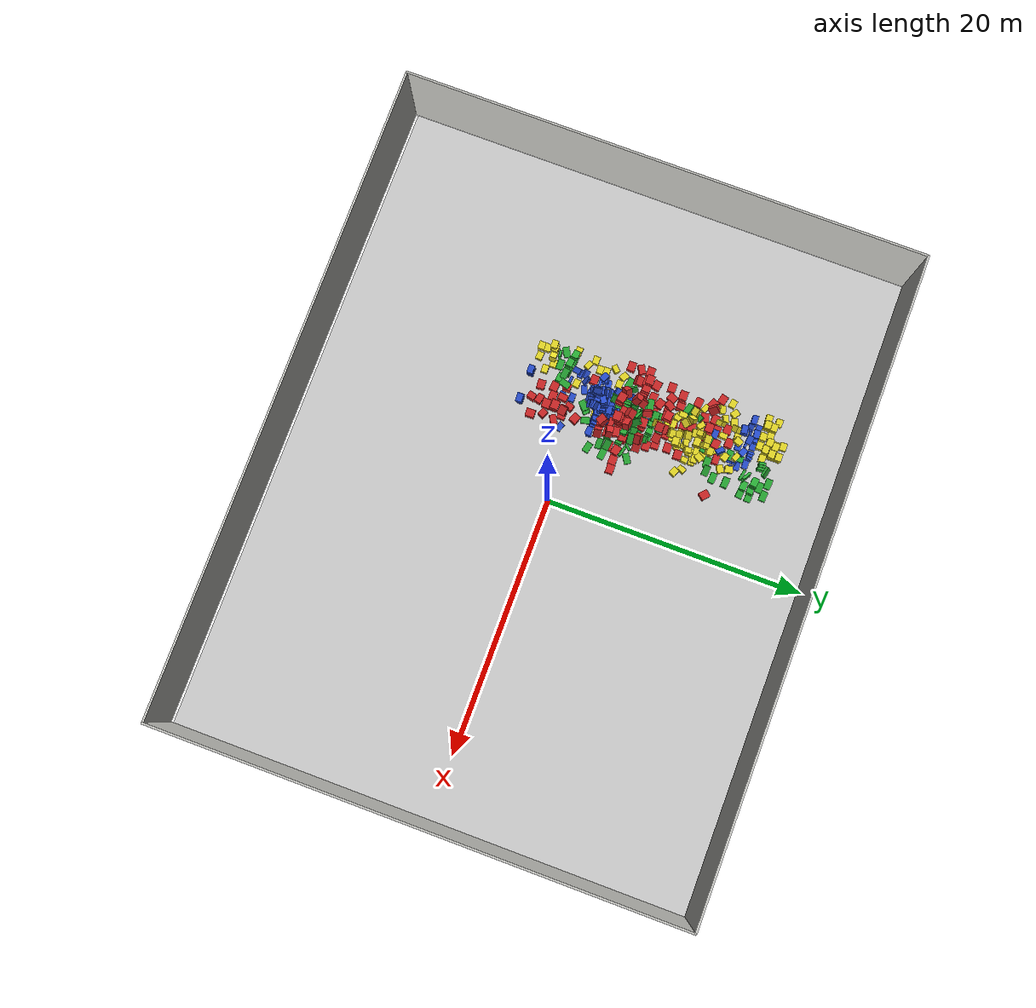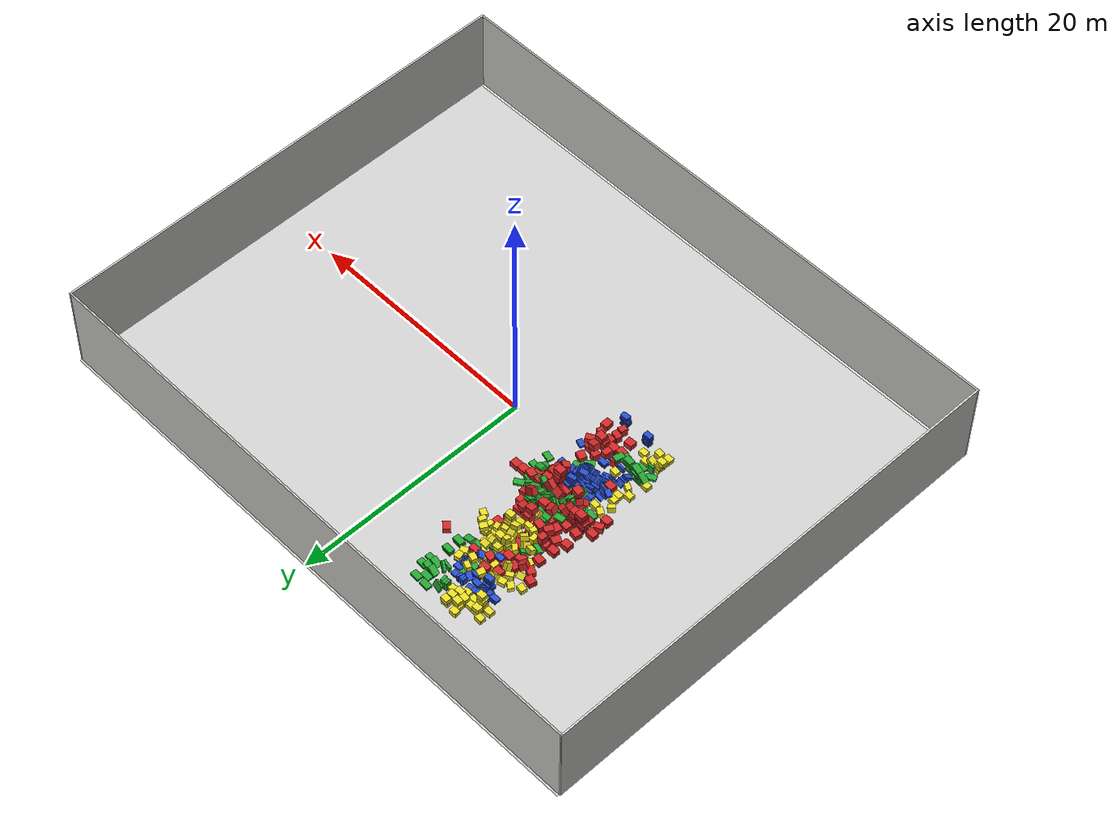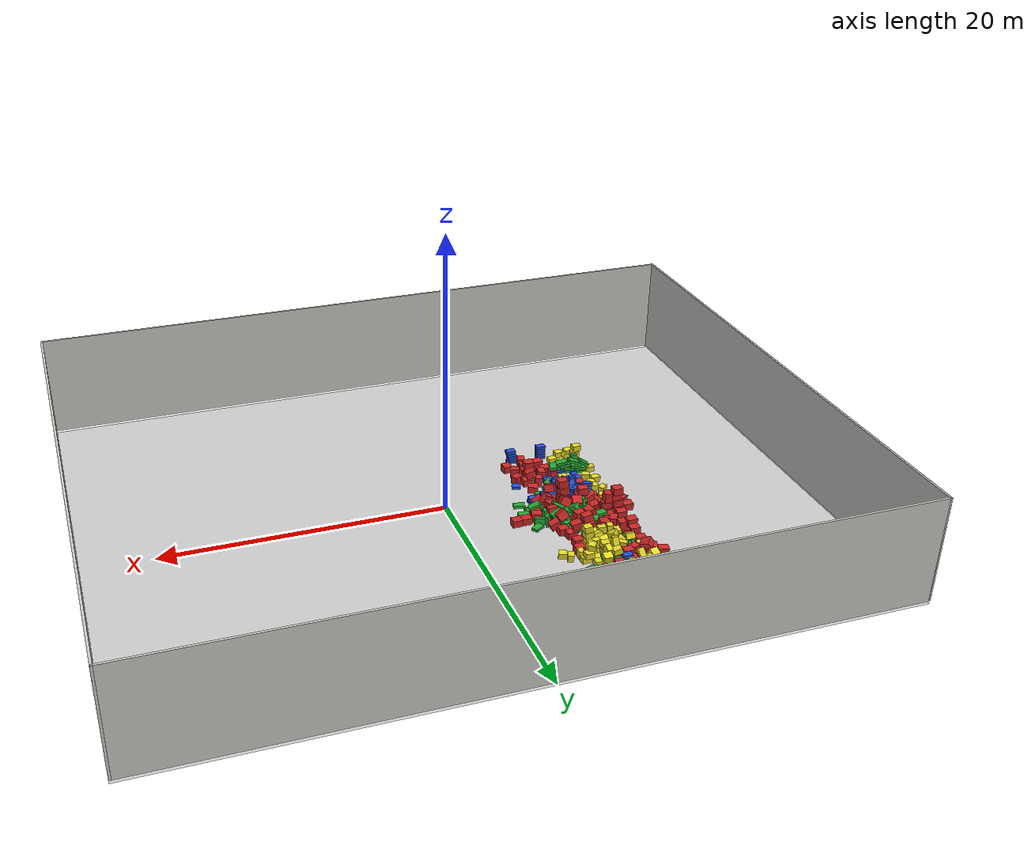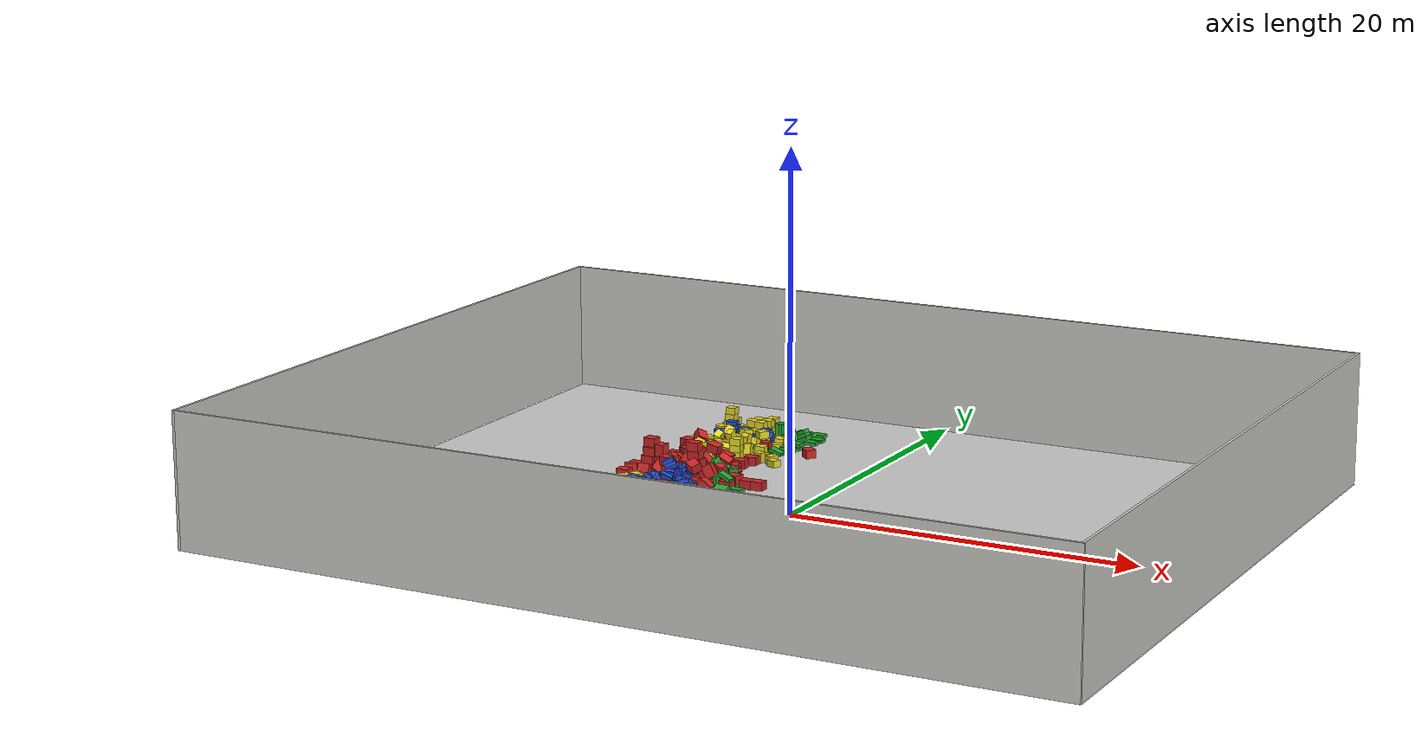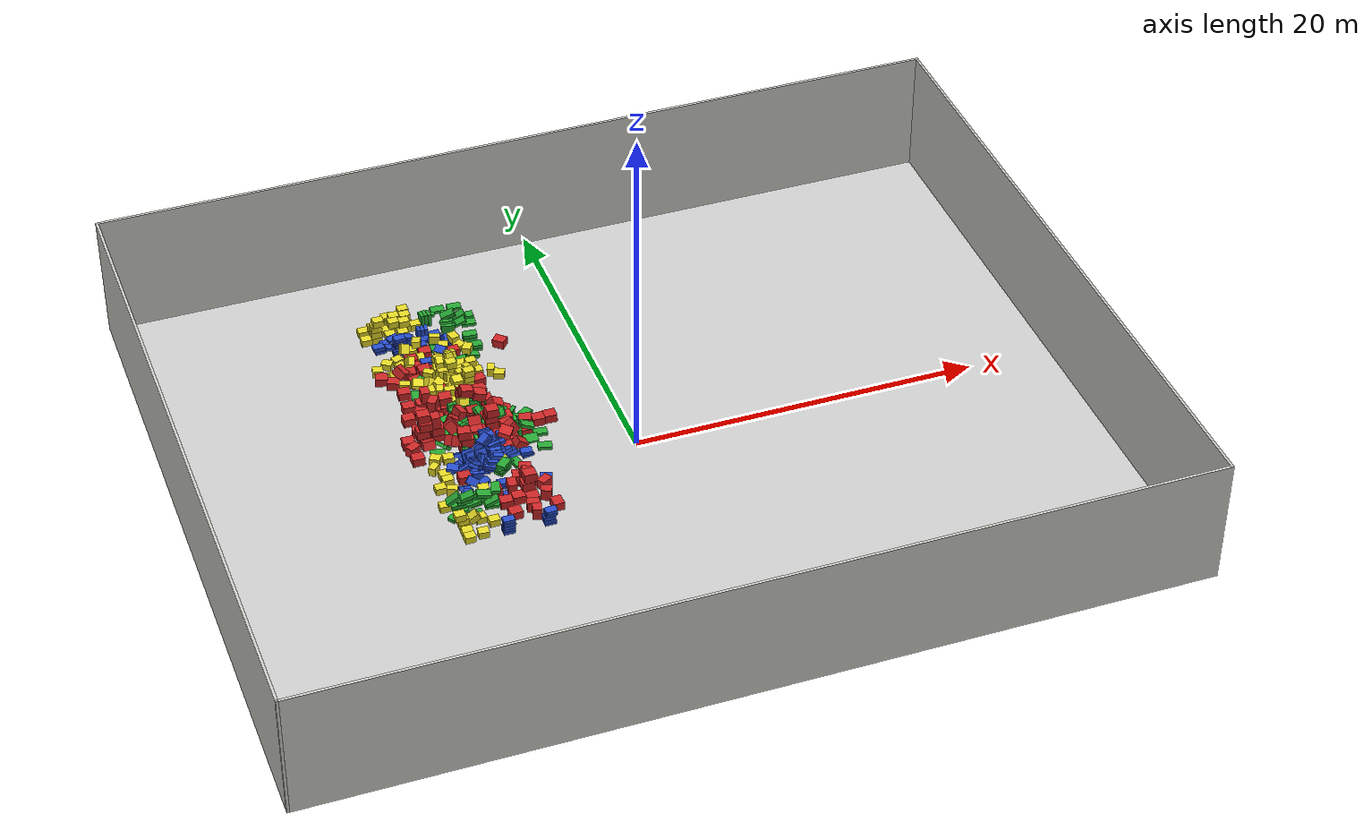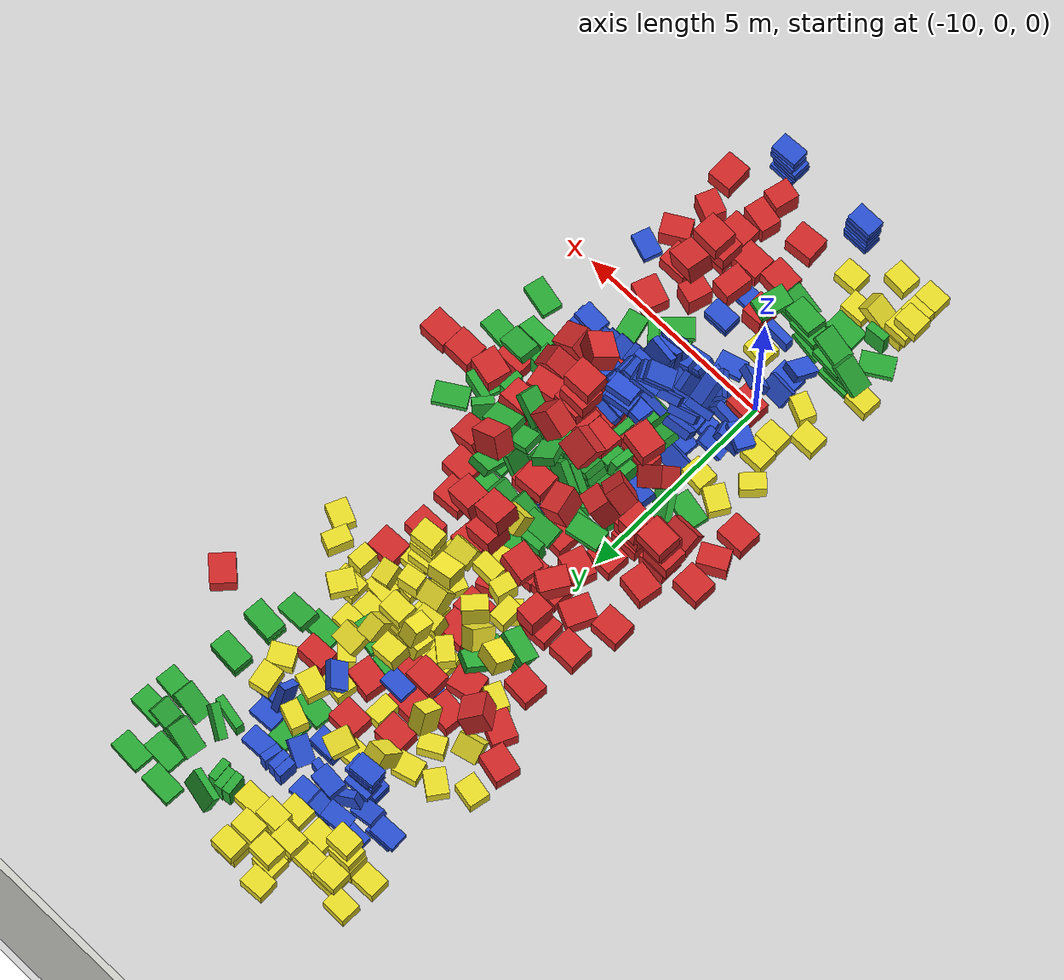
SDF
<sdf version="1.6">
 <world name="default">
  <light name="sun" type="directional">
   <pose>0 0 10 0 -0 0</pose>
   <diffuse>0.8 0.8 0.8 1</diffuse>
   <specular>0.1 0.1 0.1 1</specular>
   <attenuation>
    <range>1000</range>
    <constant>0.9</constant>
    <linear>0.01</linear>
    <quadratic>0.001</quadratic>
   </attenuation>
   <direction>-0.5 0.5 -1</direction>
  </light>
  <model name="factory_floor">
   <static>1</static>
   <link name="link">
    <collision name="collision">
     <geometry><plane><normal>0 0 1</normal><size>50 40</size></plane></geometry>
     <surface><friction><ode><mu>100</mu><mu2>50</mu2></ode></friction></surface>
    </collision>
    <visual name="visual">
     <cast_shadows>0</cast_shadows>
     <geometry><plane><normal>0 0 1</normal><size>50 40</size></plane></geometry>
     <material>
      <script>
       <uri>model://factory_floor/materials/scripts/factory_floor.material</uri>
       <name>FactoryFloor/Image</name>
      </script>
     </material>
    </visual>
   </link>
  </model>
  <model name="factory_outer_frame">
   <pose>-0.065475 -0.22786 0 0 -0 0</pose>
   <link name="Wall_0">
    <collision name="Wall_0_Collision">
     <geometry><box><size>40.15 0.15 7.5</size></box></geometry>
     <pose>0 0 3.75 0 -0 0</pose>
    </collision>
    <visual name="Wall_0_Visual">
     <pose>0 0 3.75 0 -0 0</pose>
     <geometry><box><size>40.15 0.15 7.5</size></box></geometry>
     <material>
      <script><uri>file://media/materials/scripts/gazebo.material</uri><name>Gazebo/CeilingTiled</name></script>
      <ambient>1 1 1 1</ambient>
     </material>
    </visual>
    <pose>-25 0 0 0 -0 1.5708</pose>
   </link>
   <link name="Wall_1">
    <collision name="Wall_1_Collision">
     <geometry><box><size>50.15 0.15 7.5</size></box></geometry>
     <pose>0 0 3.75 0 -0 0</pose>
    </collision>
    <visual name="Wall_1_Visual">
     <pose>0 0 3.75 0 -0 0</pose>
     <geometry><box><size>50.15 0.15 7.5</size></box></geometry>
     <material>
      <script><uri>file://media/materials/scripts/gazebo.material</uri><name>Gazebo/CeilingTiled</name></script>
      <ambient>1 1 1 1</ambient>
     </material>
    </visual>
    <pose>0 20 0 0 -0 0</pose>
   </link>
   <link name="Wall_2">
    <collision name="Wall_2_Collision">
     <geometry><box><size>40.15 0.15 7.5</size></box></geometry>
     <pose>0 0 3.75 0 -0 0</pose>
    </collision>
    <visual name="Wall_2_Visual">
     <pose>0 0 3.75 0 -0 0</pose>
     <geometry><box><size>40.15 0.15 7.5</size></box></geometry>
     <material>
      <script><uri>file://media/materials/scripts/gazebo.material</uri><name>Gazebo/CeilingTiled</name></script>
      <ambient>1 1 1 1</ambient>
     </material>
    </visual>
    <pose>25 0 0 0 0 -1.5708</pose>
   </link>
   <link name="Wall_3">
    <collision name="Wall_3_Collision">
     <geometry><box><size>50.15 0.15 7.5</size></box></geometry>
     <pose>0 0 3.75 0 -0 0</pose>
    </collision>
    <visual name="Wall_3_Visual">
     <pose>0 0 3.75 0 -0 0</pose>
     <geometry><box><size>50.15 0.15 7.5</size></box></geometry>
     <material>
      <script><uri>file://media/materials/scripts/gazebo.material</uri><name>Gazebo/CeilingTiled</name></script>
      <ambient>1 1 1 1</ambient>
     </material>
    </visual>
    <pose>0 -20 0 0 -0 3.14159</pose>
   </link>
   <static>1</static>
  </model>
  <model name="baggage_A">
   <static>0</static>
   <link name="link">
    <collision name="collision"><geometry><box><size>0.7 0.6 0.5</size></box></geometry></collision>
    <visual name="visual">
     <geometry><box><size>0.7 0.6 0.5</size></box></geometry>
     <material>
      <script><uri>file://media/materials/scripts/gazebo.material</uri><name>Gazebo/Red</name></script>
     </material>
    </visual>
    <inertial>
     <inertia><ixx>1</ixx><ixy>0</ixy><ixz>0</ixz><iyy>1</iyy><iyz>0</iyz><izz>1</izz></inertia>
     <mass>1</mass>
    </inertial>
   </link>
   <pose>-6.48609 -1.24773 0.25 0 0 -0.002983</pose>
  </model>
  <model name="baggage_B">
   <static>0</static>
   <link name="link">
    <collision name="collision"><geometry><box><size>0.65 0.45 0.2</size></box></geometry></collision>
    <visual name="visual">
     <geometry><box><size>0.65 0.45 0.2</size></box></geometry>
     <material>
      <script><uri>file://media/materials/scripts/gazebo.material</uri><name>Gazebo/Blue</name></script>
     </material>
    </visual>
    <inertial>
     <inertia><ixx>1</ixx><ixy>0</ixy><ixz>0</ixz><iyy>1</iyy><iyz>0</iyz><izz>1</izz></inertia>
     <mass>1</mass>
    </inertial>
   </link>
   <pose>-6.50918 -4.65756 0.895572 0.000131 0.00018 0.041147</pose>
  </model>
  <model name="baggage_C">
   <static>0</static>
   <link name="link">
    <collision name="collision"><geometry><box><size>0.6 0.5 0.4</size></box></geometry></collision>
    <visual name="visual">
     <geometry><box><size>0.6 0.5 0.4</size></box></geometry>
     <material>
      <script><uri>file://media/materials/scripts/gazebo.material</uri><name>Gazebo/Yellow</name></script>
     </material>
    </visual>
    <inertial>
     <inertia><ixx>1</ixx><ixy>0</ixy><ixz>0</ixz><iyy>1</iyy><iyz>0</iyz><izz>1</izz></inertia>
     <mass>1</mass>
    </inertial>
   </link>
   <pose>-10.0024 -3.21625 0.19997 -0 1e-06 0.03848</pose>
  </model>
  <model name="baggage_D">
   <static>0</static>
   <link name="link">
    <collision name="collision"><geometry><box><size>0.8 0.5 0.2</size></box></geometry></collision>
    <visual name="visual">
     <geometry><box><size>0.8 0.5 0.2</size></box></geometry>
     <material>
      <script><uri>file://media/materials/scripts/gazebo.material</uri><name>Gazebo/Green</name></script>
     </material>
    </visual>
    <inertial>
     <inertia><ixx>1</ixx><ixy>0</ixy><ixz>0</ixz><iyy>1</iyy><iyz>0</iyz><izz>1</izz></inertia>
     <mass>1</mass>
    </inertial>
   </link>
   <pose>-9.08099 -2.35326 0.443171 5.7e-05 -0.385028 -0.081844</pose>
  </model>
  <gravity>0 0 -9.8</gravity>
  <magnetic_field>6e-06 2.3e-05 -4.2e-05</magnetic_field>
  <atmosphere type="adiabatic"/>
  <physics name="default_physics" default="0" type="ode">
   <max_step_size>0.001</max_step_size>
   <real_time_factor>1</real_time_factor>
   <real_time_update_rate>1000</real_time_update_rate>
  </physics>
  <scene><ambient>0.4 0.4 0.4 1</ambient><background>0.7 0.7 0.7 1</background><shadows>1</shadows></scene>
  <spherical_coordinates>
   <surface_model>EARTH_WGS84</surface_model>
   <latitude_deg>0</latitude_deg>
   <longitude_deg>0</longitude_deg>
   <elevation>0</elevation>
   <heading_deg>0</heading_deg>
  </spherical_coordinates>
  <model name="baggage_B_clone">
   <static>0</static>
   <link name="link">
    <collision name="collision"><geometry><box><size>0.65 0.45 0.2</size></box></geometry></collision>
    <visual name="visual">
     <geometry><box><size>0.65 0.45 0.2</size></box></geometry>
     <material>
      <script><uri>file://media/materials/scripts/gazebo.material</uri><name>Gazebo/Blue</name></script>
     </material>
    </visual>
    <inertial>
     <inertia><ixx>1</ixx><ixy>0</ixy><ixz>0</ixz><iyy>1</iyy><iyz>0</iyz><izz>1</izz></inertia>
     <mass>1</mass>
    </inertial>
   </link>
   <pose>-6.56403 -4.59425 0.09982 1.5e-05 7e-06 0.000138</pose>
  </model>
  <model name="baggage_B_clone_0">
   <static>0</static>
   <link name="link">
    <collision name="collision"><geometry><box><size>0.65 0.45 0.2</size></box></geometry></collision>
    <visual name="visual">
     <geometry><box><size>0.65 0.45 0.2</size></box></geometry>
     <material>
      <script><uri>file://media/materials/scripts/gazebo.material</uri><name>Gazebo/Blue</name></script>
     </material>
    </visual>
    <inertial>
     <inertia><ixx>1</ixx><ixy>0</ixy><ixz>0</ixz><iyy>1</iyy><iyz>0</iyz><izz>1</izz></inertia>
     <mass>1</mass>
    </inertial>
   </link>
   <pose>-6.53248 -4.61255 0.695603 0.000122 0.000185 -0.003893</pose>
  </model>
  <model name="baggage_B_clone_1">
   <static>0</static>
   <link name="link">
    <collision name="collision"><geometry><box><size>0.65 0.45 0.2</size></box></geometry></collision>
    <visual name="visual">
     <geometry><box><size>0.65 0.45 0.2</size></box></geometry>
     <material>
      <script><uri>file://media/materials/scripts/gazebo.material</uri><name>Gazebo/Blue</name></script>
     </material>
    </visual>
    <inertial>
     <inertia><ixx>1</ixx><ixy>0</ixy><ixz>0</ixz><iyy>1</iyy><iyz>0</iyz><izz>1</izz></inertia>
     <mass>1</mass>
    </inertial>
   </link>
   <pose>-6.61123 -4.6231 0.495617 0.000121 0.000186 -0.011889</pose>
  </model>
  <model name="baggage_B_clone_2">
   <static>0</static>
   <link name="link">
    <collision name="collision"><geometry><box><size>0.65 0.45 0.2</size></box></geometry></collision>
    <visual name="visual">
     <geometry><box><size>0.65 0.45 0.2</size></box></geometry>
     <material>
      <script><uri>file://media/materials/scripts/gazebo.material</uri><name>Gazebo/Blue</name></script>
     </material>
    </visual>
    <inertial>
     <inertia><ixx>1</ixx><ixy>0</ixy><ixz>0</ixz><iyy>1</iyy><iyz>0</iyz><izz>1</izz></inertia>
     <mass>1</mass>
    </inertial>
   </link>
   <pose>-6.62387 -4.64102 0.29982 1.5e-05 7e-06 -0.012189</pose>
  </model>
  <model name="baggage_B_clone_3">
   <static>0</static>
   <link name="link">
    <collision name="collision"><geometry><box><size>0.65 0.45 0.2</size></box></geometry></collision>
    <visual name="visual">
     <geometry><box><size>0.65 0.45 0.2</size></box></geometry>
     <material>
      <script><uri>file://media/materials/scripts/gazebo.material</uri><name>Gazebo/Blue</name></script>
     </material>
    </visual>
    <inertial>
     <inertia><ixx>1</ixx><ixy>0</ixy><ixz>0</ixz><iyy>1</iyy><iyz>0</iyz><izz>1</izz></inertia>
     <mass>1</mass>
    </inertial>
   </link>
   <pose>-8.83892 -4.5935 0.499508 1.9e-05 2e-05 -0.011908</pose>
  </model>
  <model name="baggage_B_clone_4">
   <static>0</static>
   <link name="link">
    <collision name="collision"><geometry><box><size>0.65 0.45 0.2</size></box></geometry></collision>
    <visual name="visual">
     <geometry><box><size>0.65 0.45 0.2</size></box></geometry>
     <material>
      <script><uri>file://media/materials/scripts/gazebo.material</uri><name>Gazebo/Blue</name></script>
     </material>
    </visual>
    <inertial>
     <inertia><ixx>1</ixx><ixy>0</ixy><ixz>0</ixz><iyy>1</iyy><iyz>0</iyz><izz>1</izz></inertia>
     <mass>1</mass>
    </inertial>
   </link>
   <pose>-8.84925 -4.56067 0.099617 1.8e-05 2.2e-05 0.000958</pose>
  </model>
  <model name="baggage_B_clone_5">
   <static>0</static>
   <link name="link">
    <collision name="collision"><geometry><box><size>0.65 0.45 0.2</size></box></geometry></collision>
    <visual name="visual">
     <geometry><box><size>0.65 0.45 0.2</size></box></geometry>
     <material>
      <script><uri>file://media/materials/scripts/gazebo.material</uri><name>Gazebo/Blue</name></script>
     </material>
    </visual>
    <inertial>
     <inertia><ixx>1</ixx><ixy>0</ixy><ixz>0</ixz><iyy>1</iyy><iyz>0</iyz><izz>1</izz></inertia>
     <mass>1</mass>
    </inertial>
   </link>
   <pose>-7.92374 -1.76438 0.1 0 0 -0.017897</pose>
  </model>
  <model name="baggage_B_clone_6">
   <static>0</static>
   <link name="link">
    <collision name="collision"><geometry><box><size>0.65 0.45 0.2</size></box></geometry></collision>
    <visual name="visual">
     <geometry><box><size>0.65 0.45 0.2</size></box></geometry>
     <material>
      <script><uri>file://media/materials/scripts/gazebo.material</uri><name>Gazebo/Blue</name></script>
     </material>
    </visual>
    <inertial>
     <inertia><ixx>1</ixx><ixy>0</ixy><ixz>0</ixz><iyy>1</iyy><iyz>0</iyz><izz>1</izz></inertia>
     <mass>1</mass>
    </inertial>
   </link>
   <pose>-8.00112 -0.995911 0.099982 2e-06 -3e-06 0.000404</pose>
  </model>
  <model name="baggage_B_clone_7">
   <static>0</static>
   <link name="link">
    <collision name="collision"><geometry><box><size>0.65 0.45 0.2</size></box></geometry></collision>
    <visual name="visual">
     <geometry><box><size>0.65 0.45 0.2</size></box></geometry>
     <material>
      <script><uri>file://media/materials/scripts/gazebo.material</uri><name>Gazebo/Blue</name></script>
     </material>
    </visual>
    <inertial>
     <inertia><ixx>1</ixx><ixy>0</ixy><ixz>0</ixz><iyy>1</iyy><iyz>0</iyz><izz>1</izz></inertia>
     <mass>1</mass>
    </inertial>
   </link>
   <pose>-8.00628 -0.980284 0.299987 1.8e-05 -6e-06 0.000107</pose>
  </model>
  <model name="baggage_B_clone_8">
   <static>0</static>
   <link name="link">
    <collision name="collision"><geometry><box><size>0.65 0.45 0.2</size></box></geometry></collision>
    <visual name="visual">
     <geometry><box><size>0.65 0.45 0.2</size></box></geometry>
     <material>
      <script><uri>file://media/materials/scripts/gazebo.material</uri><name>Gazebo/Blue</name></script>
     </material>
    </visual>
    <inertial>
     <inertia><ixx>1</ixx><ixy>0</ixy><ixz>0</ixz><iyy>1</iyy><iyz>0</iyz><izz>1</izz></inertia>
     <mass>1</mass>
    </inertial>
   </link>
   <pose>-8.85185 -4.61375 0.899508 1.6e-05 3.1e-05 -0.006663</pose>
  </model>
  <model name="baggage_B_clone_9">
   <static>0</static>
   <link name="link">
    <collision name="collision"><geometry><box><size>0.65 0.45 0.2</size></box></geometry></collision>
    <visual name="visual">
     <geometry><box><size>0.65 0.45 0.2</size></box></geometry>
     <material>
      <script><uri>file://media/materials/scripts/gazebo.material</uri><name>Gazebo/Blue</name></script>
     </material>
    </visual>
    <inertial>
     <inertia><ixx>1</ixx><ixy>0</ixy><ixz>0</ixz><iyy>1</iyy><iyz>0</iyz><izz>1</izz></inertia>
     <mass>1</mass>
    </inertial>
   </link>
   <pose>-9.09562 0.56977 0.099987 5e-06 1.2e-05 -0.04829</pose>
  </model>
  <model name="baggage_B_clone_10">
   <static>0</static>
   <link name="link">
    <collision name="collision"><geometry><box><size>0.65 0.45 0.2</size></box></geometry></collision>
    <visual name="visual">
     <geometry><box><size>0.65 0.45 0.2</size></box></geometry>
     <material>
      <script><uri>file://media/materials/scripts/gazebo.material</uri><name>Gazebo/Blue</name></script>
     </material>
    </visual>
    <inertial>
     <inertia><ixx>1</ixx><ixy>0</ixy><ixz>0</ixz><iyy>1</iyy><iyz>0</iyz><izz>1</izz></inertia>
     <mass>1</mass>
    </inertial>
   </link>
   <pose>-8.83854 -4.54571 0.299526 2.1e-05 1.8e-05 -0.004779</pose>
  </model>
  <model name="baggage_B_clone_11">
   <static>0</static>
   <link name="link">
    <collision name="collision"><geometry><box><size>0.65 0.45 0.2</size></box></geometry></collision>
    <visual name="visual">
     <geometry><box><size>0.65 0.45 0.2</size></box></geometry>
     <material>
      <script><uri>file://media/materials/scripts/gazebo.material</uri><name>Gazebo/Blue</name></script>
     </material>
    </visual>
    <inertial>
     <inertia><ixx>1</ixx><ixy>0</ixy><ixz>0</ixz><iyy>1</iyy><iyz>0</iyz><izz>1</izz></inertia>
     <mass>1</mass>
    </inertial>
   </link>
   <pose>-8.83119 -4.59747 0.69951 1.5e-05 2.4e-05 -0.008866</pose>
  </model>
  <model name="baggage_B_clone_12">
   <static>0</static>
   <link name="link">
    <collision name="collision"><geometry><box><size>0.65 0.45 0.2</size></box></geometry></collision>
    <visual name="visual">
     <geometry><box><size>0.65 0.45 0.2</size></box></geometry>
     <material>
      <script><uri>file://media/materials/scripts/gazebo.material</uri><name>Gazebo/Blue</name></script>
     </material>
    </visual>
    <inertial>
     <inertia><ixx>1</ixx><ixy>0</ixy><ixz>0</ixz><iyy>1</iyy><iyz>0</iyz><izz>1</izz></inertia>
     <mass>1</mass>
    </inertial>
   </link>
   <pose>-9.57464 2.12773 0.201535 -0.541106 -2.3e-05 -0.080653</pose>
  </model>
  <model name="baggage_B_clone_13">
   <static>0</static>
   <link name="link">
    <collision name="collision"><geometry><box><size>0.65 0.45 0.2</size></box></geometry></collision>
    <visual name="visual">
     <geometry><box><size>0.65 0.45 0.2</size></box></geometry>
     <material>
      <script><uri>file://media/materials/scripts/gazebo.material</uri><name>Gazebo/Blue</name></script>
     </material>
    </visual>
    <inertial>
     <inertia><ixx>1</ixx><ixy>0</ixy><ixz>0</ixz><iyy>1</iyy><iyz>0</iyz><izz>1</izz></inertia>
     <mass>1</mass>
    </inertial>
   </link>
   <pose>-9.33932 1.69038 0.099796 -6e-06 1.5e-05 -0.068763</pose>
  </model>
  <model name="baggage_B_clone_14">
   <static>0</static>
   <link name="link">
    <collision name="collision"><geometry><box><size>0.65 0.45 0.2</size></box></geometry></collision>
    <visual name="visual">
     <geometry><box><size>0.65 0.45 0.2</size></box></geometry>
     <material>
      <script><uri>file://media/materials/scripts/gazebo.material</uri><name>Gazebo/Blue</name></script>
     </material>
    </visual>
    <inertial>
     <inertia><ixx>1</ixx><ixy>0</ixy><ixz>0</ixz><iyy>1</iyy><iyz>0</iyz><izz>1</izz></inertia>
     <mass>1</mass>
    </inertial>
   </link>
   <pose>-9.56282 3.24194 0.200423 -3.14159 0.331866 -0.098079</pose>
  </model>
  <model name="baggage_B_clone_15">
   <static>0</static>
   <link name="link">
    <collision name="collision"><geometry><box><size>0.65 0.45 0.2</size></box></geometry></collision>
    <visual name="visual">
     <geometry><box><size>0.65 0.45 0.2</size></box></geometry>
     <material>
      <script><uri>file://media/materials/scripts/gazebo.material</uri><name>Gazebo/Blue</name></script>
     </material>
    </visual>
    <inertial>
     <inertia><ixx>1</ixx><ixy>0</ixy><ixz>0</ixz><iyy>1</iyy><iyz>0</iyz><izz>1</izz></inertia>
     <mass>1</mass>
    </inertial>
   </link>
   <pose>-9.99996 -1.00392 0.099626 3e-05 -5.6e-05 -0.006165</pose>
  </model>
  <model name="baggage_C_clone">
   <static>0</static>
   <link name="link">
    <collision name="collision"><geometry><box><size>0.6 0.5 0.4</size></box></geometry></collision>
    <visual name="visual">
     <geometry><box><size>0.6 0.5 0.4</size></box></geometry>
     <material>
      <script><uri>file://media/materials/scripts/gazebo.material</uri><name>Gazebo/Yellow</name></script>
     </material>
    </visual>
    <inertial>
     <inertia><ixx>1</ixx><ixy>0</ixy><ixz>0</ixz><iyy>1</iyy><iyz>0</iyz><izz>1</izz></inertia>
     <mass>1</mass>
    </inertial>
   </link>
   <pose>-7.49956 1.03327 0.199506 -3.14152 -7e-06 -3.05208</pose>
  </model>
  <model name="baggage_C_clone_0">
   <static>0</static>
   <link name="link">
    <collision name="collision"><geometry><box><size>0.6 0.5 0.4</size></box></geometry></collision>
    <visual name="visual">
     <geometry><box><size>0.6 0.5 0.4</size></box></geometry>
     <material>
      <script><uri>file://media/materials/scripts/gazebo.material</uri><name>Gazebo/Yellow</name></script>
     </material>
    </visual>
    <inertial>
     <inertia><ixx>1</ixx><ixy>0</ixy><ixz>0</ixz><iyy>1</iyy><iyz>0</iyz><izz>1</izz></inertia>
     <mass>1</mass>
    </inertial>
   </link>
   <pose>-11.0017 -4.52372 0.199999 1e-06 -2e-06 -0.001946</pose>
  </model>
  <model name="baggage_C_clone_1">
   <static>0</static>
   <link name="link">
    <collision name="collision"><geometry><box><size>0.6 0.5 0.4</size></box></geometry></collision>
    <visual name="visual">
     <geometry><box><size>0.6 0.5 0.4</size></box></geometry>
     <material>
      <script><uri>file://media/materials/scripts/gazebo.material</uri><name>Gazebo/Yellow</name></script>
     </material>
    </visual>
    <inertial>
     <inertia><ixx>1</ixx><ixy>0</ixy><ixz>0</ixz><iyy>1</iyy><iyz>0</iyz><izz>1</izz></inertia>
     <mass>1</mass>
    </inertial>
   </link>
   <pose>-9.38817 -3.67013 0.199992 -3.14158 5e-06 0.022305</pose>
  </model>
  <model name="baggage_C_clone_2">
   <static>0</static>
   <link name="link">
    <collision name="collision"><geometry><box><size>0.6 0.5 0.4</size></box></geometry></collision>
    <visual name="visual">
     <geometry><box><size>0.6 0.5 0.4</size></box></geometry>
     <material>
      <script><uri>file://media/materials/scripts/gazebo.material</uri><name>Gazebo/Yellow</name></script>
     </material>
    </visual>
    <inertial>
     <inertia><ixx>1</ixx><ixy>0</ixy><ixz>0</ixz><iyy>1</iyy><iyz>0</iyz><izz>1</izz></inertia>
     <mass>1</mass>
    </inertial>
   </link>
   <pose>-10.9967 -4.02251 0.199999 2e-06 2e-06 -0.001425</pose>
  </model>
  <model name="baggage_C_clone_3">
   <static>0</static>
   <link name="link">
    <collision name="collision"><geometry><box><size>0.6 0.5 0.4</size></box></geometry></collision>
    <visual name="visual">
     <geometry><box><size>0.6 0.5 0.4</size></box></geometry>
     <material>
      <script><uri>file://media/materials/scripts/gazebo.material</uri><name>Gazebo/Yellow</name></script>
     </material>
    </visual>
    <inertial>
     <inertia><ixx>1</ixx><ixy>0</ixy><ixz>0</ixz><iyy>1</iyy><iyz>0</iyz><izz>1</izz></inertia>
     <mass>1</mass>
    </inertial>
   </link>
   <pose>-10.8818 2.17288 0.200003 3e-05 -2.3e-05 -0.552718</pose>
  </model>
  <model name="baggage_C_clone_4">
   <static>0</static>
   <link name="link">
    <collision name="collision"><geometry><box><size>0.6 0.5 0.4</size></box></geometry></collision>
    <visual name="visual">
     <geometry><box><size>0.6 0.5 0.4</size></box></geometry>
     <material>
      <script><uri>file://media/materials/scripts/gazebo.material</uri><name>Gazebo/Yellow</name></script>
     </material>
    </visual>
    <inertial>
     <inertia><ixx>1</ixx><ixy>0</ixy><ixz>0</ixz><iyy>1</iyy><iyz>0</iyz><izz>1</izz></inertia>
     <mass>1</mass>
    </inertial>
   </link>
   <pose>-10.7751 -0.648973 0.25 -1.5708 1e-06 -0.420451</pose>
  </model>
  <model name="baggage_C_clone_5">
   <static>0</static>
   <link name="link">
    <collision name="collision"><geometry><box><size>0.6 0.5 0.4</size></box></geometry></collision>
    <visual name="visual">
     <geometry><box><size>0.6 0.5 0.4</size></box></geometry>
     <material>
      <script><uri>file://media/materials/scripts/gazebo.material</uri><name>Gazebo/Yellow</name></script>
     </material>
    </visual>
    <inertial>
     <inertia><ixx>1</ixx><ixy>0</ixy><ixz>0</ixz><iyy>1</iyy><iyz>0</iyz><izz>1</izz></inertia>
     <mass>1</mass>
    </inertial>
   </link>
   <pose>-9.15669 -1.03519 0.199995 -3.14159 0 -0.059287</pose>
  </model>
  <model name="baggage_C_clone_6">
   <static>0</static>
   <link name="link">
    <collision name="collision"><geometry><box><size>0.6 0.5 0.4</size></box></geometry></collision>
    <visual name="visual">
     <geometry><box><size>0.6 0.5 0.4</size></box></geometry>
     <material>
      <script><uri>file://media/materials/scripts/gazebo.material</uri><name>Gazebo/Yellow</name></script>
     </material>
    </visual>
    <inertial>
     <inertia><ixx>1</ixx><ixy>0</ixy><ixz>0</ixz><iyy>1</iyy><iyz>0</iyz><izz>1</izz></inertia>
     <mass>1</mass>
    </inertial>
   </link>
   <pose>-10.2092 -4.3999 0.200001 3.14159 -0 -0.062981</pose>
  </model>
  <model name="baggage_C_clone_7">
   <static>0</static>
   <link name="link">
    <collision name="collision"><geometry><box><size>0.6 0.5 0.4</size></box></geometry></collision>
    <visual name="visual">
     <geometry><box><size>0.6 0.5 0.4</size></box></geometry>
     <material>
      <script><uri>file://media/materials/scripts/gazebo.material</uri><name>Gazebo/Yellow</name></script>
     </material>
    </visual>
    <inertial>
     <inertia><ixx>1</ixx><ixy>0</ixy><ixz>0</ixz><iyy>1</iyy><iyz>0</iyz><izz>1</izz></inertia>
     <mass>1</mass>
    </inertial>
   </link>
   <pose>-11.238 -3.5718 0.999986 2.7e-05 -1.9e-05 0.007549</pose>
  </model>
  <model name="baggage_C_clone_8">
   <static>0</static>
   <link name="link">
    <collision name="collision"><geometry><box><size>0.6 0.5 0.4</size></box></geometry></collision>
    <visual name="visual">
     <geometry><box><size>0.6 0.5 0.4</size></box></geometry>
     <material>
      <script><uri>file://media/materials/scripts/gazebo.material</uri><name>Gazebo/Yellow</name></script>
     </material>
    </visual>
    <inertial>
     <inertia><ixx>1</ixx><ixy>0</ixy><ixz>0</ixz><iyy>1</iyy><iyz>0</iyz><izz>1</izz></inertia>
     <mass>1</mass>
    </inertial>
   </link>
   <pose>-10.4253 -3.38527 0.554591 0.022847 -0.577296 -0.003336</pose>
  </model>
  <model name="baggage_C_clone_9">
   <static>0</static>
   <link name="link">
    <collision name="collision"><geometry><box><size>0.6 0.5 0.4</size></box></geometry></collision>
    <visual name="visual">
     <geometry><box><size>0.6 0.5 0.4</size></box></geometry>
     <material>
      <script><uri>file://media/materials/scripts/gazebo.material</uri><name>Gazebo/Yellow</name></script>
     </material>
    </visual>
    <inertial>
     <inertia><ixx>1</ixx><ixy>0</ixy><ixz>0</ixz><iyy>1</iyy><iyz>0</iyz><izz>1</izz></inertia>
     <mass>1</mass>
    </inertial>
   </link>
   <pose>-11.2 1.37021 0.249999 -1.57079 1e-06 0.810669</pose>
  </model>
  <model name="baggage_C_clone_10">
   <static>0</static>
   <link name="link">
    <collision name="collision"><geometry><box><size>0.6 0.5 0.4</size></box></geometry></collision>
    <visual name="visual">
     <geometry><box><size>0.6 0.5 0.4</size></box></geometry>
     <material>
      <script><uri>file://media/materials/scripts/gazebo.material</uri><name>Gazebo/Yellow</name></script>
     </material>
    </visual>
    <inertial>
     <inertia><ixx>1</ixx><ixy>0</ixy><ixz>0</ixz><iyy>1</iyy><iyz>0</iyz><izz>1</izz></inertia>
     <mass>1</mass>
    </inertial>
   </link>
   <pose>-10.9828 -3.43446 0.200002 0 -8e-06 -0.003334</pose>
  </model>
  <model name="baggage_C_clone_11">
   <static>0</static>
   <link name="link">
    <collision name="collision"><geometry><box><size>0.6 0.5 0.4</size></box></geometry></collision>
    <visual name="visual">
     <geometry><box><size>0.6 0.5 0.4</size></box></geometry>
     <material>
      <script><uri>file://media/materials/scripts/gazebo.material</uri><name>Gazebo/Yellow</name></script>
     </material>
    </visual>
    <inertial>
     <inertia><ixx>1</ixx><ixy>0</ixy><ixz>0</ixz><iyy>1</iyy><iyz>0</iyz><izz>1</izz></inertia>
     <mass>1</mass>
    </inertial>
   </link>
   <pose>-11.086 -3.459 0.599988 1e-05 -2e-05 0.006204</pose>
  </model>
  <model name="baggage_C_clone_12">
   <static>0</static>
   <link name="link">
    <collision name="collision"><geometry><box><size>0.6 0.5 0.4</size></box></geometry></collision>
    <visual name="visual">
     <geometry><box><size>0.6 0.5 0.4</size></box></geometry>
     <material>
      <script><uri>file://media/materials/scripts/gazebo.material</uri><name>Gazebo/Yellow</name></script>
     </material>
    </visual>
    <inertial>
     <inertia><ixx>1</ixx><ixy>0</ixy><ixz>0</ixz><iyy>1</iyy><iyz>0</iyz><izz>1</izz></inertia>
     <mass>1</mass>
    </inertial>
   </link>
   <pose>-11.5507 -1.72457 0.2 0 0 -0.042376</pose>
  </model>
  <model name="baggage_C_clone_13">
   <static>0</static>
   <link name="link">
    <collision name="collision"><geometry><box><size>0.6 0.5 0.4</size></box></geometry></collision>
    <visual name="visual">
     <geometry><box><size>0.6 0.5 0.4</size></box></geometry>
     <material>
      <script><uri>file://media/materials/scripts/gazebo.material</uri><name>Gazebo/Yellow</name></script>
     </material>
    </visual>
    <inertial>
     <inertia><ixx>1</ixx><ixy>0</ixy><ixz>0</ixz><iyy>1</iyy><iyz>0</iyz><izz>1</izz></inertia>
     <mass>1</mass>
    </inertial>
   </link>
   <pose>-10.2107 2.01865 0.200039 -8e-06 -4.8e-05 -0.077626</pose>
  </model>
  <model name="baggage_C_clone_14">
   <static>0</static>
   <link name="link">
    <collision name="collision"><geometry><box><size>0.6 0.5 0.4</size></box></geometry></collision>
    <visual name="visual">
     <geometry><box><size>0.6 0.5 0.4</size></box></geometry>
     <material>
      <script><uri>file://media/materials/scripts/gazebo.material</uri><name>Gazebo/Yellow</name></script>
     </material>
    </visual>
    <inertial>
     <inertia><ixx>1</ixx><ixy>0</ixy><ixz>0</ixz><iyy>1</iyy><iyz>0</iyz><izz>1</izz></inertia>
     <mass>1</mass>
    </inertial>
   </link>
   <pose>-10.7647 0.281198 0.199983 0 1e-06 0.002002</pose>
  </model>
  <model name="baggage_C_clone_15">
   <static>0</static>
   <link name="link">
    <collision name="collision"><geometry><box><size>0.6 0.5 0.4</size></box></geometry></collision>
    <visual name="visual">
     <geometry><box><size>0.6 0.5 0.4</size></box></geometry>
     <material>
      <script><uri>file://media/materials/scripts/gazebo.material</uri><name>Gazebo/Yellow</name></script>
     </material>
    </visual>
    <inertial>
     <inertia><ixx>1</ixx><ixy>0</ixy><ixz>0</ixz><iyy>1</iyy><iyz>0</iyz><izz>1</izz></inertia>
     <mass>1</mass>
    </inertial>
   </link>
   <pose>-10.8004 0.781658 0.2 0 -0 0.004001</pose>
  </model>
  <model name="baggage_C_clone_16">
   <static>0</static>
   <link name="link">
    <collision name="collision"><geometry><box><size>0.6 0.5 0.4</size></box></geometry></collision>
    <visual name="visual">
     <geometry><box><size>0.6 0.5 0.4</size></box></geometry>
     <material>
      <script><uri>file://media/materials/scripts/gazebo.material</uri><name>Gazebo/Yellow</name></script>
     </material>
    </visual>
    <inertial>
     <inertia><ixx>1</ixx><ixy>0</ixy><ixz>0</ixz><iyy>1</iyy><iyz>0</iyz><izz>1</izz></inertia>
     <mass>1</mass>
    </inertial>
   </link>
   <pose>-11.3403 -0.250339 0.199999 1e-06 -2e-06 0.000189</pose>
  </model>
  <model name="baggage_A_clone">
   <static>0</static>
   <link name="link">
    <collision name="collision"><geometry><box><size>0.7 0.6 0.5</size></box></geometry></collision>
    <visual name="visual">
     <geometry><box><size>0.7 0.6 0.5</size></box></geometry>
     <material>
      <script><uri>file://media/materials/scripts/gazebo.material</uri><name>Gazebo/Red</name></script>
     </material>
    </visual>
    <inertial>
     <inertia><ixx>1</ixx><ixy>0</ixy><ixz>0</ixz><iyy>1</iyy><iyz>0</iyz><izz>1</izz></inertia>
     <mass>1</mass>
    </inertial>
   </link>
   <pose>-6.89891 -2.65548 0.249999 0 3e-06 0.003736</pose>
  </model>
  <model name="baggage_A_clone_0">
   <static>0</static>
   <link name="link">
    <collision name="collision"><geometry><box><size>0.7 0.6 0.5</size></box></geometry></collision>
    <visual name="visual">
     <geometry><box><size>0.7 0.6 0.5</size></box></geometry>
     <material>
      <script><uri>file://media/materials/scripts/gazebo.material</uri><name>Gazebo/Red</name></script>
     </material>
    </visual>
    <inertial>
     <inertia><ixx>1</ixx><ixy>0</ixy><ixz>0</ixz><iyy>1</iyy><iyz>0</iyz><izz>1</izz></inertia>
     <mass>1</mass>
    </inertial>
   </link>
   <pose>-5.89985 -1.72351 0.300001 -1.57079 -1e-06 0.524036</pose>
  </model>
  <model name="baggage_A_clone_1">
   <static>0</static>
   <link name="link">
    <collision name="collision"><geometry><box><size>0.7 0.6 0.5</size></box></geometry></collision>
    <visual name="visual">
     <geometry><box><size>0.7 0.6 0.5</size></box></geometry>
     <material>
      <script><uri>file://media/materials/scripts/gazebo.material</uri><name>Gazebo/Red</name></script>
     </material>
    </visual>
    <inertial>
     <inertia><ixx>1</ixx><ixy>0</ixy><ixz>0</ixz><iyy>1</iyy><iyz>0</iyz><izz>1</izz></inertia>
     <mass>1</mass>
    </inertial>
   </link>
   <pose>-7.05431 -3.25438 0.299994 1.5708 1e-06 -0.212895</pose>
  </model>
  <model name="baggage_A_clone_2">
   <static>0</static>
   <link name="link">
    <collision name="collision"><geometry><box><size>0.7 0.6 0.5</size></box></geometry></collision>
    <visual name="visual">
     <geometry><box><size>0.7 0.6 0.5</size></box></geometry>
     <material>
      <script><uri>file://media/materials/scripts/gazebo.material</uri><name>Gazebo/Red</name></script>
     </material>
    </visual>
    <inertial>
     <inertia><ixx>1</ixx><ixy>0</ixy><ixz>0</ixz><iyy>1</iyy><iyz>0</iyz><izz>1</izz></inertia>
     <mass>1</mass>
    </inertial>
   </link>
   <pose>-7.23767 -0.923609 0.35 0.687213 -1.57079 -0.970433</pose>
  </model>
  <model name="baggage_A_clone_3">
   <static>0</static>
   <link name="link">
    <collision name="collision"><geometry><box><size>0.7 0.6 0.5</size></box></geometry></collision>
    <visual name="visual">
     <geometry><box><size>0.7 0.6 0.5</size></box></geometry>
     <material>
      <script><uri>file://media/materials/scripts/gazebo.material</uri><name>Gazebo/Red</name></script>
     </material>
    </visual>
    <inertial>
     <inertia><ixx>1</ixx><ixy>0</ixy><ixz>0</ixz><iyy>1</iyy><iyz>0</iyz><izz>1</izz></inertia>
     <mass>1</mass>
    </inertial>
   </link>
   <pose>-5.77945 -3.52225 0.25 0 -0 1.61742</pose>
  </model>
  <model name="baggage_A_clone_4">
   <static>0</static>
   <link name="link">
    <collision name="collision"><geometry><box><size>0.7 0.6 0.5</size></box></geometry></collision>
    <visual name="visual">
     <geometry><box><size>0.7 0.6 0.5</size></box></geometry>
     <material>
      <script><uri>file://media/materials/scripts/gazebo.material</uri><name>Gazebo/Red</name></script>
     </material>
    </visual>
    <inertial>
     <inertia><ixx>1</ixx><ixy>0</ixy><ixz>0</ixz><iyy>1</iyy><iyz>0</iyz><izz>1</izz></inertia>
     <mass>1</mass>
    </inertial>
   </link>
   <pose>-7.03228 -3.86913 0.349999 2.53827 -1.57079 -2.7699</pose>
  </model>
  <model name="baggage_A_clone_5">
   <static>0</static>
   <link name="link">
    <collision name="collision"><geometry><box><size>0.7 0.6 0.5</size></box></geometry></collision>
    <visual name="visual">
     <geometry><box><size>0.7 0.6 0.5</size></box></geometry>
     <material>
      <script><uri>file://media/materials/scripts/gazebo.material</uri><name>Gazebo/Red</name></script>
     </material>
    </visual>
    <inertial>
     <inertia><ixx>1</ixx><ixy>0</ixy><ixz>0</ixz><iyy>1</iyy><iyz>0</iyz><izz>1</izz></inertia>
     <mass>1</mass>
    </inertial>
   </link>
   <pose>-8.56744 -1.58966 0.349968 0.885161 1.57079 0.910334</pose>
  </model>
  <model name="baggage_A_clone_6">
   <static>0</static>
   <link name="link">
    <collision name="collision"><geometry><box><size>0.7 0.6 0.5</size></box></geometry></collision>
    <visual name="visual">
     <geometry><box><size>0.7 0.6 0.5</size></box></geometry>
     <material>
      <script><uri>file://media/materials/scripts/gazebo.material</uri><name>Gazebo/Red</name></script>
     </material>
    </visual>
    <inertial>
     <inertia><ixx>1</ixx><ixy>0</ixy><ixz>0</ixz><iyy>1</iyy><iyz>0</iyz><izz>1</izz></inertia>
     <mass>1</mass>
    </inertial>
   </link>
   <pose>-8.13946 -3.5127 0.25 -3.14159 -0 0.065318</pose>
  </model>
  <model name="baggage_A_clone_7">
   <static>0</static>
   <link name="link">
    <collision name="collision"><geometry><box><size>0.7 0.6 0.5</size></box></geometry></collision>
    <visual name="visual">
     <geometry><box><size>0.7 0.6 0.5</size></box></geometry>
     <material>
      <script><uri>file://media/materials/scripts/gazebo.material</uri><name>Gazebo/Red</name></script>
     </material>
    </visual>
    <inertial>
     <inertia><ixx>1</ixx><ixy>0</ixy><ixz>0</ixz><iyy>1</iyy><iyz>0</iyz><izz>1</izz></inertia>
     <mass>1</mass>
    </inertial>
   </link>
   <pose>-6.54453 -0.22486 0.25 -3.14159 0 -0.357107</pose>
  </model>
  <model name="baggage_A_clone_8">
   <static>0</static>
   <link name="link">
    <collision name="collision"><geometry><box><size>0.7 0.6 0.5</size></box></geometry></collision>
    <visual name="visual">
     <geometry><box><size>0.7 0.6 0.5</size></box></geometry>
     <material>
      <script><uri>file://media/materials/scripts/gazebo.material</uri><name>Gazebo/Red</name></script>
     </material>
    </visual>
    <inertial>
     <inertia><ixx>1</ixx><ixy>0</ixy><ixz>0</ixz><iyy>1</iyy><iyz>0</iyz><izz>1</izz></inertia>
     <mass>1</mass>
    </inertial>
   </link>
   <pose>-6.75233 -1.28046 0.85781 0.045005 0.320586 -0.141043</pose>
  </model>
  <model name="baggage_A_clone_9">
   <static>0</static>
   <link name="link">
    <collision name="collision"><geometry><box><size>0.7 0.6 0.5</size></box></geometry></collision>
    <visual name="visual">
     <geometry><box><size>0.7 0.6 0.5</size></box></geometry>
     <material>
      <script><uri>file://media/materials/scripts/gazebo.material</uri><name>Gazebo/Red</name></script>
     </material>
    </visual>
    <inertial>
     <inertia><ixx>1</ixx><ixy>0</ixy><ixz>0</ixz><iyy>1</iyy><iyz>0</iyz><izz>1</izz></inertia>
     <mass>1</mass>
    </inertial>
   </link>
   <pose>-6.08349 -2.6093 0.349999 2.20435 -1.57079 -1.03699</pose>
  </model>
  <model name="baggage_A_clone_10">
   <static>0</static>
   <link name="link">
    <collision name="collision"><geometry><box><size>0.7 0.6 0.5</size></box></geometry></collision>
    <visual name="visual">
     <geometry><box><size>0.7 0.6 0.5</size></box></geometry>
     <material>
      <script><uri>file://media/materials/scripts/gazebo.material</uri><name>Gazebo/Red</name></script>
     </material>
    </visual>
    <inertial>
     <inertia><ixx>1</ixx><ixy>0</ixy><ixz>0</ixz><iyy>1</iyy><iyz>0</iyz><izz>1</izz></inertia>
     <mass>1</mass>
    </inertial>
   </link>
   <pose>-7.71357 -1.59823 0.500016 -1.57066 1.7e-05 1.44447</pose>
  </model>
  <model name="baggage_A_clone_11">
   <static>0</static>
   <link name="link">
    <collision name="collision"><geometry><box><size>0.7 0.6 0.5</size></box></geometry></collision>
    <visual name="visual">
     <geometry><box><size>0.7 0.6 0.5</size></box></geometry>
     <material>
      <script><uri>file://media/materials/scripts/gazebo.material</uri><name>Gazebo/Red</name></script>
     </material>
    </visual>
    <inertial>
     <inertia><ixx>1</ixx><ixy>0</ixy><ixz>0</ixz><iyy>1</iyy><iyz>0</iyz><izz>1</izz></inertia>
     <mass>1</mass>
    </inertial>
   </link>
   <pose>-6.82463 -1.92187 1.24996 -5e-06 6e-05 -0.034321</pose>
  </model>
  <model name="baggage_A_clone_12">
   <static>0</static>
   <link name="link">
    <collision name="collision"><geometry><box><size>0.7 0.6 0.5</size></box></geometry></collision>
    <visual name="visual">
     <geometry><box><size>0.7 0.6 0.5</size></box></geometry>
     <material>
      <script><uri>file://media/materials/scripts/gazebo.material</uri><name>Gazebo/Red</name></script>
     </material>
    </visual>
    <inertial>
     <inertia><ixx>1</ixx><ixy>0</ixy><ixz>0</ixz><iyy>1</iyy><iyz>0</iyz><izz>1</izz></inertia>
     <mass>1</mass>
    </inertial>
   </link>
   <pose>-6.9106 -2.05292 0.249973 -2e-06 5e-06 0.011337</pose>
  </model>
  <model name="baggage_A_clone_13">
   <static>0</static>
   <link name="link">
    <collision name="collision"><geometry><box><size>0.7 0.6 0.5</size></box></geometry></collision>
    <visual name="visual">
     <geometry><box><size>0.7 0.6 0.5</size></box></geometry>
     <material>
      <script><uri>file://media/materials/scripts/gazebo.material</uri><name>Gazebo/Red</name></script>
     </material>
    </visual>
    <inertial>
     <inertia><ixx>1</ixx><ixy>0</ixy><ixz>0</ixz><iyy>1</iyy><iyz>0</iyz><izz>1</izz></inertia>
     <mass>1</mass>
    </inertial>
   </link>
   <pose>-6.97197 -2.00554 0.749974 -2e-06 8e-06 -0.00131</pose>
  </model>
  <model name="baggage_A_clone_14">
   <static>0</static>
   <link name="link">
    <collision name="collision"><geometry><box><size>0.7 0.6 0.5</size></box></geometry></collision>
    <visual name="visual">
     <geometry><box><size>0.7 0.6 0.5</size></box></geometry>
     <material>
      <script><uri>file://media/materials/scripts/gazebo.material</uri><name>Gazebo/Red</name></script>
     </material>
    </visual>
    <inertial>
     <inertia><ixx>1</ixx><ixy>0</ixy><ixz>0</ixz><iyy>1</iyy><iyz>0</iyz><izz>1</izz></inertia>
     <mass>1</mass>
    </inertial>
   </link>
   <pose>-7.61128 -2.36937 0.249982 -3e-06 -7e-06 -0.003856</pose>
  </model>
  <model name="baggage_A_clone_15">
   <static>0</static>
   <link name="link">
    <collision name="collision"><geometry><box><size>0.7 0.6 0.5</size></box></geometry></collision>
    <visual name="visual">
     <geometry><box><size>0.7 0.6 0.5</size></box></geometry>
     <material>
      <script><uri>file://media/materials/scripts/gazebo.material</uri><name>Gazebo/Red</name></script>
     </material>
    </visual>
    <inertial>
     <inertia><ixx>1</ixx><ixy>0</ixy><ixz>0</ixz><iyy>1</iyy><iyz>0</iyz><izz>1</izz></inertia>
     <mass>1</mass>
    </inertial>
   </link>
   <pose>-8.33411 -2.50749 0.250203 3.9e-05 -4e-06 -0.081785</pose>
  </model>
  <model name="baggage_A_clone_16">
   <static>0</static>
   <link name="link">
    <collision name="collision"><geometry><box><size>0.7 0.6 0.5</size></box></geometry></collision>
    <visual name="visual">
     <geometry><box><size>0.7 0.6 0.5</size></box></geometry>
     <material>
      <script><uri>file://media/materials/scripts/gazebo.material</uri><name>Gazebo/Red</name></script>
     </material>
    </visual>
    <inertial>
     <inertia><ixx>1</ixx><ixy>0</ixy><ixz>0</ixz><iyy>1</iyy><iyz>0</iyz><izz>1</izz></inertia>
     <mass>1</mass>
    </inertial>
   </link>
   <pose>-9.86076 0.147167 0.249983 2e-06 1e-06 -0.034937</pose>
  </model>
  <model name="baggage_D_clone">
   <static>0</static>
   <link name="link">
    <collision name="collision"><geometry><box><size>0.8 0.5 0.2</size></box></geometry></collision>
    <visual name="visual">
     <geometry><box><size>0.8 0.5 0.2</size></box></geometry>
     <material>
      <script><uri>file://media/materials/scripts/gazebo.material</uri><name>Gazebo/Green</name></script>
     </material>
    </visual>
    <inertial>
     <inertia><ixx>1</ixx><ixy>0</ixy><ixz>0</ixz><iyy>1</iyy><iyz>0</iyz><izz>1</izz></inertia>
     <mass>1</mass>
    </inertial>
   </link>
   <pose>-8.70727 -1.81308 0.799972 3.14159 5.3e-05 -1.82996</pose>
  </model>
  <model name="baggage_D_clone_0">
   <static>0</static>
   <link name="link">
    <collision name="collision"><geometry><box><size>0.8 0.5 0.2</size></box></geometry></collision>
    <visual name="visual">
     <geometry><box><size>0.8 0.5 0.2</size></box></geometry>
     <material>
      <script><uri>file://media/materials/scripts/gazebo.material</uri><name>Gazebo/Green</name></script>
     </material>
    </visual>
    <inertial>
     <inertia><ixx>1</ixx><ixy>0</ixy><ixz>0</ixz><iyy>1</iyy><iyz>0</iyz><izz>1</izz></inertia>
     <mass>1</mass>
    </inertial>
   </link>
   <pose>-10.7939 -1.79789 0.099736 -4e-06 3.4e-05 -0.032781</pose>
  </model>
  <model name="baggage_D_clone_1">
   <static>0</static>
   <link name="link">
    <collision name="collision"><geometry><box><size>0.8 0.5 0.2</size></box></geometry></collision>
    <visual name="visual">
     <geometry><box><size>0.8 0.5 0.2</size></box></geometry>
     <material>
      <script><uri>file://media/materials/scripts/gazebo.material</uri><name>Gazebo/Green</name></script>
     </material>
    </visual>
    <inertial>
     <inertia><ixx>1</ixx><ixy>0</ixy><ixz>0</ixz><iyy>1</iyy><iyz>0</iyz><izz>1</izz></inertia>
     <mass>1</mass>
    </inertial>
   </link>
   <pose>-7.66123 0.190995 0.299873 3.14156 -3.2e-05 -2.77024</pose>
  </model>
  <model name="baggage_D_clone_2">
   <static>0</static>
   <link name="link">
    <collision name="collision"><geometry><box><size>0.8 0.5 0.2</size></box></geometry></collision>
    <visual name="visual">
     <geometry><box><size>0.8 0.5 0.2</size></box></geometry>
     <material>
      <script><uri>file://media/materials/scripts/gazebo.material</uri><name>Gazebo/Green</name></script>
     </material>
    </visual>
    <inertial>
     <inertia><ixx>1</ixx><ixy>0</ixy><ixz>0</ixz><iyy>1</iyy><iyz>0</iyz><izz>1</izz></inertia>
     <mass>1</mass>
    </inertial>
   </link>
   <pose>-7.63386 0.055749 0.699793 4.2e-05 2.1e-05 -2.37756</pose>
  </model>
  <model name="baggage_D_clone_3">
   <static>0</static>
   <link name="link">
    <collision name="collision"><geometry><box><size>0.8 0.5 0.2</size></box></geometry></collision>
    <visual name="visual">
     <geometry><box><size>0.8 0.5 0.2</size></box></geometry>
     <material>
      <script><uri>file://media/materials/scripts/gazebo.material</uri><name>Gazebo/Green</name></script>
     </material>
    </visual>
    <inertial>
     <inertia><ixx>1</ixx><ixy>0</ixy><ixz>0</ixz><iyy>1</iyy><iyz>0</iyz><izz>1</izz></inertia>
     <mass>1</mass>
    </inertial>
   </link>
   <pose>-9.06676 -2.26528 0.1 0 0 -0.081788</pose>
  </model>
  <model name="baggage_D_clone_4">
   <static>0</static>
   <link name="link">
    <collision name="collision"><geometry><box><size>0.8 0.5 0.2</size></box></geometry></collision>
    <visual name="visual">
     <geometry><box><size>0.8 0.5 0.2</size></box></geometry>
     <material>
      <script><uri>file://media/materials/scripts/gazebo.material</uri><name>Gazebo/Green</name></script>
     </material>
    </visual>
    <inertial>
     <inertia><ixx>1</ixx><ixy>0</ixy><ixz>0</ixz><iyy>1</iyy><iyz>0</iyz><izz>1</izz></inertia>
     <mass>1</mass>
    </inertial>
   </link>
   <pose>-9.82362 -1.95477 0.200936 -2e-05 -0.264039 -0.081776</pose>
  </model>
  <model name="baggage_D_clone_5">
   <static>0</static>
   <link name="link">
    <collision name="collision"><geometry><box><size>0.8 0.5 0.2</size></box></geometry></collision>
    <visual name="visual">
     <geometry><box><size>0.8 0.5 0.2</size></box></geometry>
     <material>
      <script><uri>file://media/materials/scripts/gazebo.material</uri><name>Gazebo/Green</name></script>
     </material>
    </visual>
    <inertial>
     <inertia><ixx>1</ixx><ixy>0</ixy><ixz>0</ixz><iyy>1</iyy><iyz>0</iyz><izz>1</izz></inertia>
     <mass>1</mass>
    </inertial>
   </link>
   <pose>-7.66569 0.236285 0.09983 1e-05 2.5e-05 -2.50216</pose>
  </model>
  <model name="baggage_D_clone_6">
   <static>0</static>
   <link name="link">
    <collision name="collision"><geometry><box><size>0.8 0.5 0.2</size></box></geometry></collision>
    <visual name="visual">
     <geometry><box><size>0.8 0.5 0.2</size></box></geometry>
     <material>
      <script><uri>file://media/materials/scripts/gazebo.material</uri><name>Gazebo/Green</name></script>
     </material>
    </visual>
    <inertial>
     <inertia><ixx>1</ixx><ixy>0</ixy><ixz>0</ixz><iyy>1</iyy><iyz>0</iyz><izz>1</izz></inertia>
     <mass>1</mass>
    </inertial>
   </link>
   <pose>-7.46138 0.220002 0.499798 -3.14155 2.2e-05 -2.41357</pose>
  </model>
  <model name="baggage_D_clone_7">
   <static>0</static>
   <link name="link">
    <collision name="collision"><geometry><box><size>0.8 0.5 0.2</size></box></geometry></collision>
    <visual name="visual">
     <geometry><box><size>0.8 0.5 0.2</size></box></geometry>
     <material>
      <script><uri>file://media/materials/scripts/gazebo.material</uri><name>Gazebo/Green</name></script>
     </material>
    </visual>
    <inertial>
     <inertia><ixx>1</ixx><ixy>0</ixy><ixz>0</ixz><iyy>1</iyy><iyz>0</iyz><izz>1</izz></inertia>
     <mass>1</mass>
    </inertial>
   </link>
   <pose>-11.1894 -2.58897 0.1 -3.14159 -0 -2.59962</pose>
  </model>
  <model name="baggage_D_clone_8">
   <static>0</static>
   <link name="link">
    <collision name="collision"><geometry><box><size>0.8 0.5 0.2</size></box></geometry></collision>
    <visual name="visual">
     <geometry><box><size>0.8 0.5 0.2</size></box></geometry>
     <material>
      <script><uri>file://media/materials/scripts/gazebo.material</uri><name>Gazebo/Green</name></script>
     </material>
    </visual>
    <inertial>
     <inertia><ixx>1</ixx><ixy>0</ixy><ixz>0</ixz><iyy>1</iyy><iyz>0</iyz><izz>1</izz></inertia>
     <mass>1</mass>
    </inertial>
   </link>
   <pose>-10.8045 -2.95992 0.4 -1.78421 -1.57079 0.281605</pose>
  </model>
  <model name="baggage_D_clone_9">
   <static>0</static>
   <link name="link">
    <collision name="collision"><geometry><box><size>0.8 0.5 0.2</size></box></geometry></collision>
    <visual name="visual">
     <geometry><box><size>0.8 0.5 0.2</size></box></geometry>
     <material>
      <script><uri>file://media/materials/scripts/gazebo.material</uri><name>Gazebo/Green</name></script>
     </material>
    </visual>
    <inertial>
     <inertia><ixx>1</ixx><ixy>0</ixy><ixz>0</ixz><iyy>1</iyy><iyz>0</iyz><izz>1</izz></inertia>
     <mass>1</mass>
    </inertial>
   </link>
   <pose>-11.0958 -1.82879 0.701913 -2e-05 -0.576569 -0.11261</pose>
  </model>
  <model name="baggage_D_clone_10">
   <static>0</static>
   <link name="link">
    <collision name="collision"><geometry><box><size>0.8 0.5 0.2</size></box></geometry></collision>
    <visual name="visual">
     <geometry><box><size>0.8 0.5 0.2</size></box></geometry>
     <material>
      <script><uri>file://media/materials/scripts/gazebo.material</uri><name>Gazebo/Green</name></script>
     </material>
    </visual>
    <inertial>
     <inertia><ixx>1</ixx><ixy>0</ixy><ixz>0</ixz><iyy>1</iyy><iyz>0</iyz><izz>1</izz></inertia>
     <mass>1</mass>
    </inertial>
   </link>
   <pose>-10.8568 -1.88671 0.299729 -5e-06 3.4e-05 -0.042346</pose>
  </model>
  <model name="baggage_D_clone_11">
   <static>0</static>
   <link name="link">
    <collision name="collision"><geometry><box><size>0.8 0.5 0.2</size></box></geometry></collision>
    <visual name="visual">
     <geometry><box><size>0.8 0.5 0.2</size></box></geometry>
     <material>
      <script><uri>file://media/materials/scripts/gazebo.material</uri><name>Gazebo/Green</name></script>
     </material>
    </visual>
    <inertial>
     <inertia><ixx>1</ixx><ixy>0</ixy><ixz>0</ixz><iyy>1</iyy><iyz>0</iyz><izz>1</izz></inertia>
     <mass>1</mass>
    </inertial>
   </link>
   <pose>-10.3705 -2.00141 0.838906 0.001715 -0.346404 -0.115711</pose>
  </model>
  <model name="baggage_D_clone_12">
   <static>0</static>
   <link name="link">
    <collision name="collision"><geometry><box><size>0.8 0.5 0.2</size></box></geometry></collision>
    <visual name="visual">
     <geometry><box><size>0.8 0.5 0.2</size></box></geometry>
     <material>
      <script><uri>file://media/materials/scripts/gazebo.material</uri><name>Gazebo/Green</name></script>
     </material>
    </visual>
    <inertial>
     <inertia><ixx>1</ixx><ixy>0</ixy><ixz>0</ixz><iyy>1</iyy><iyz>0</iyz><izz>1</izz></inertia>
     <mass>1</mass>
    </inertial>
   </link>
   <pose>-9.45974 -2.08699 0.831532 -0.009163 0.168599 -0.136194</pose>
  </model>
  <model name="baggage_D_clone_13">
   <static>0</static>
   <link name="link">
    <collision name="collision"><geometry><box><size>0.8 0.5 0.2</size></box></geometry></collision>
    <visual name="visual">
     <geometry><box><size>0.8 0.5 0.2</size></box></geometry>
     <material>
      <script><uri>file://media/materials/scripts/gazebo.material</uri><name>Gazebo/Green</name></script>
     </material>
    </visual>
    <inertial>
     <inertia><ixx>1</ixx><ixy>0</ixy><ixz>0</ixz><iyy>1</iyy><iyz>0</iyz><izz>1</izz></inertia>
     <mass>1</mass>
    </inertial>
   </link>
   <pose>-9.69969 -1.99267 0.67073 -0.003448 0.168818 -0.102165</pose>
  </model>
  <model name="baggage_D_clone_14">
   <static>0</static>
   <link name="link">
    <collision name="collision"><geometry><box><size>0.8 0.5 0.2</size></box></geometry></collision>
    <visual name="visual">
     <geometry><box><size>0.8 0.5 0.2</size></box></geometry>
     <material>
      <script><uri>file://media/materials/scripts/gazebo.material</uri><name>Gazebo/Green</name></script>
     </material>
    </visual>
    <inertial>
     <inertia><ixx>1</ixx><ixy>0</ixy><ixz>0</ixz><iyy>1</iyy><iyz>0</iyz><izz>1</izz></inertia>
     <mass>1</mass>
    </inertial>
   </link>
   <pose>-10.4951 -1.8853 0.519063 1.5e-05 -0.048599 -0.081861</pose>
  </model>
  <model name="baggage_D_clone_15">
   <static>0</static>
   <link name="link">
    <collision name="collision"><geometry><box><size>0.8 0.5 0.2</size></box></geometry></collision>
    <visual name="visual">
     <geometry><box><size>0.8 0.5 0.2</size></box></geometry>
     <material>
      <script><uri>file://media/materials/scripts/gazebo.material</uri><name>Gazebo/Green</name></script>
     </material>
    </visual>
    <inertial>
     <inertia><ixx>1</ixx><ixy>0</ixy><ixz>0</ixz><iyy>1</iyy><iyz>0</iyz><izz>1</izz></inertia>
     <mass>1</mass>
    </inertial>
   </link>
   <pose>-10.0127 -2.05534 0.359313 -1.5e-05 -0.263986 -0.081723</pose>
  </model>
  <model name="baggage_D_clone_16">
   <static>0</static>
   <link name="link">
    <collision name="collision"><geometry><box><size>0.8 0.5 0.2</size></box></geometry></collision>
    <visual name="visual">
     <geometry><box><size>0.8 0.5 0.2</size></box></geometry>
     <material>
      <script><uri>file://media/materials/scripts/gazebo.material</uri><name>Gazebo/Green</name></script>
     </material>
    </visual>
    <inertial>
     <inertia><ixx>1</ixx><ixy>0</ixy><ixz>0</ixz><iyy>1</iyy><iyz>0</iyz><izz>1</izz></inertia>
     <mass>1</mass>
    </inertial>
   </link>
   <pose>-10.1334 -2.69927 0.1 -3.14159 -0 -0.00069</pose>
  </model>
  <model name="baggage_A_clone_17">
   <static>0</static>
   <link name="link">
    <collision name="collision"><geometry><box><size>0.7 0.6 0.5</size></box></geometry></collision>
    <visual name="visual">
     <geometry><box><size>0.7 0.6 0.5</size></box></geometry>
     <material>
      <script><uri>file://media/materials/scripts/gazebo.material</uri><name>Gazebo/Red</name></script>
     </material>
    </visual>
    <inertial>
     <inertia><ixx>1</ixx><ixy>0</ixy><ixz>0</ixz><iyy>1</iyy><iyz>0</iyz><izz>1</izz></inertia>
     <mass>1</mass>
    </inertial>
   </link>
   <pose>-9.79374 6.12698 0.249929 5e-06 -8e-06 -0.018931</pose>
  </model>
  <model name="baggage_A_clone_18">
   <static>0</static>
   <link name="link">
    <collision name="collision"><geometry><box><size>0.7 0.6 0.5</size></box></geometry></collision>
    <visual name="visual">
     <geometry><box><size>0.7 0.6 0.5</size></box></geometry>
     <material>
      <script><uri>file://media/materials/scripts/gazebo.material</uri><name>Gazebo/Red</name></script>
     </material>
    </visual>
    <inertial>
     <inertia><ixx>1</ixx><ixy>0</ixy><ixz>0</ixz><iyy>1</iyy><iyz>0</iyz><izz>1</izz></inertia>
     <mass>1</mass>
    </inertial>
   </link>
   <pose>-8.80249 6.86566 0.249981 0 1e-06 0.308612</pose>
  </model>
  <model name="baggage_A_clone_19">
   <static>0</static>
   <link name="link">
    <collision name="collision"><geometry><box><size>0.7 0.6 0.5</size></box></geometry></collision>
    <visual name="visual">
     <geometry><box><size>0.7 0.6 0.5</size></box></geometry>
     <material>
      <script><uri>file://media/materials/scripts/gazebo.material</uri><name>Gazebo/Red</name></script>
     </material>
    </visual>
    <inertial>
     <inertia><ixx>1</ixx><ixy>0</ixy><ixz>0</ixz><iyy>1</iyy><iyz>0</iyz><izz>1</izz></inertia>
     <mass>1</mass>
    </inertial>
   </link>
   <pose>-8.91154 7.62588 0.249957 -2.1e-05 -7.6e-05 0.033002</pose>
  </model>
  <model name="baggage_A_clone_20">
   <static>0</static>
   <link name="link">
    <collision name="collision"><geometry><box><size>0.7 0.6 0.5</size></box></geometry></collision>
    <visual name="visual">
     <geometry><box><size>0.7 0.6 0.5</size></box></geometry>
     <material>
      <script><uri>file://media/materials/scripts/gazebo.material</uri><name>Gazebo/Red</name></script>
     </material>
    </visual>
    <inertial>
     <inertia><ixx>1</ixx><ixy>0</ixy><ixz>0</ixz><iyy>1</iyy><iyz>0</iyz><izz>1</izz></inertia>
     <mass>1</mass>
    </inertial>
   </link>
   <pose>-8.9939 8.22465 0.249181 0.001268 6.1e-05 0.037154</pose>
  </model>
  <model name="baggage_A_clone_21">
   <static>0</static>
   <link name="link">
    <collision name="collision"><geometry><box><size>0.7 0.6 0.5</size></box></geometry></collision>
    <visual name="visual">
     <geometry><box><size>0.7 0.6 0.5</size></box></geometry>
     <material>
      <script><uri>file://media/materials/scripts/gazebo.material</uri><name>Gazebo/Red</name></script>
     </material>
    </visual>
    <inertial>
     <inertia><ixx>1</ixx><ixy>0</ixy><ixz>0</ixz><iyy>1</iyy><iyz>0</iyz><izz>1</izz></inertia>
     <mass>1</mass>
    </inertial>
   </link>
   <pose>-10.723 9.3807 0.785879 -2.65801 -0.434698 2.19369</pose>
  </model>
  <model name="baggage_A_clone_22">
   <static>0</static>
   <link name="link">
    <collision name="collision"><geometry><box><size>0.7 0.6 0.5</size></box></geometry></collision>
    <visual name="visual">
     <geometry><box><size>0.7 0.6 0.5</size></box></geometry>
     <material>
      <script><uri>file://media/materials/scripts/gazebo.material</uri><name>Gazebo/Red</name></script>
     </material>
    </visual>
    <inertial>
     <inertia><ixx>1</ixx><ixy>0</ixy><ixz>0</ixz><iyy>1</iyy><iyz>0</iyz><izz>1</izz></inertia>
     <mass>1</mass>
    </inertial>
   </link>
   <pose>-9.3741 10.0992 0.252939 0.002003 0.003724 -0.018318</pose>
  </model>
  <model name="baggage_A_clone_23">
   <static>0</static>
   <link name="link">
    <collision name="collision"><geometry><box><size>0.7 0.6 0.5</size></box></geometry></collision>
    <visual name="visual">
     <geometry><box><size>0.7 0.6 0.5</size></box></geometry>
     <material>
      <script><uri>file://media/materials/scripts/gazebo.material</uri><name>Gazebo/Red</name></script>
     </material>
    </visual>
    <inertial>
     <inertia><ixx>1</ixx><ixy>0</ixy><ixz>0</ixz><iyy>1</iyy><iyz>0</iyz><izz>1</izz></inertia>
     <mass>1</mass>
    </inertial>
   </link>
   <pose>-10.1281 9.7162 0.250001 4e-06 1e-06 -0.097675</pose>
  </model>
  <model name="baggage_A_clone_24">
   <static>0</static>
   <link name="link">
    <collision name="collision"><geometry><box><size>0.7 0.6 0.5</size></box></geometry></collision>
    <visual name="visual">
     <geometry><box><size>0.7 0.6 0.5</size></box></geometry>
     <material>
      <script><uri>file://media/materials/scripts/gazebo.material</uri><name>Gazebo/Red</name></script>
     </material>
    </visual>
    <inertial>
     <inertia><ixx>1</ixx><ixy>0</ixy><ixz>0</ixz><iyy>1</iyy><iyz>0</iyz><izz>1</izz></inertia>
     <mass>1</mass>
    </inertial>
   </link>
   <pose>-9.34429 4.19633 0.846591 -0.879057 1.06321 -2.75863</pose>
  </model>
  <model name="baggage_A_clone_25">
   <static>0</static>
   <link name="link">
    <collision name="collision"><geometry><box><size>0.7 0.6 0.5</size></box></geometry></collision>
    <visual name="visual">
     <geometry><box><size>0.7 0.6 0.5</size></box></geometry>
     <material>
      <script><uri>file://media/materials/scripts/gazebo.material</uri><name>Gazebo/Red</name></script>
     </material>
    </visual>
    <inertial>
     <inertia><ixx>1</ixx><ixy>0</ixy><ixz>0</ixz><iyy>1</iyy><iyz>0</iyz><izz>1</izz></inertia>
     <mass>1</mass>
    </inertial>
   </link>
   <pose>-10.2258 6.91814 0.24999 -2e-06 -0 0.043237</pose>
  </model>
  <model name="baggage_A_clone_26">
   <static>0</static>
   <link name="link">
    <collision name="collision"><geometry><box><size>0.7 0.6 0.5</size></box></geometry></collision>
    <visual name="visual">
     <geometry><box><size>0.7 0.6 0.5</size></box></geometry>
     <material>
      <script><uri>file://media/materials/scripts/gazebo.material</uri><name>Gazebo/Red</name></script>
     </material>
    </visual>
    <inertial>
     <inertia><ixx>1</ixx><ixy>0</ixy><ixz>0</ixz><iyy>1</iyy><iyz>0</iyz><izz>1</izz></inertia>
     <mass>1</mass>
    </inertial>
   </link>
   <pose>-10.126 4.78046 0.249901 -1e-05 2.6e-05 -0.041728</pose>
  </model>
  <model name="baggage_A_clone_27">
   <static>0</static>
   <link name="link">
    <collision name="collision"><geometry><box><size>0.7 0.6 0.5</size></box></geometry></collision>
    <visual name="visual">
     <geometry><box><size>0.7 0.6 0.5</size></box></geometry>
     <material>
      <script><uri>file://media/materials/scripts/gazebo.material</uri><name>Gazebo/Red</name></script>
     </material>
    </visual>
    <inertial>
     <inertia><ixx>1</ixx><ixy>0</ixy><ixz>0</ixz><iyy>1</iyy><iyz>0</iyz><izz>1</izz></inertia>
     <mass>1</mass>
    </inertial>
   </link>
   <pose>-9.02698 5.1596 0.249131 -0.000162 0.000222 -0.046116</pose>
  </model>
  <model name="baggage_A_clone_28">
   <static>0</static>
   <link name="link">
    <collision name="collision"><geometry><box><size>0.7 0.6 0.5</size></box></geometry></collision>
    <visual name="visual">
     <geometry><box><size>0.7 0.6 0.5</size></box></geometry>
     <material>
      <script><uri>file://media/materials/scripts/gazebo.material</uri><name>Gazebo/Red</name></script>
     </material>
    </visual>
    <inertial>
     <inertia><ixx>1</ixx><ixy>0</ixy><ixz>0</ixz><iyy>1</iyy><iyz>0</iyz><izz>1</izz></inertia>
     <mass>1</mass>
    </inertial>
   </link>
   <pose>-6.45215 5.49884 0.250311 3.4e-05 3.4e-05 0.002134</pose>
  </model>
  <model name="baggage_A_clone_29">
   <static>0</static>
   <link name="link">
    <collision name="collision"><geometry><box><size>0.7 0.6 0.5</size></box></geometry></collision>
    <visual name="visual">
     <geometry><box><size>0.7 0.6 0.5</size></box></geometry>
     <material>
      <script><uri>file://media/materials/scripts/gazebo.material</uri><name>Gazebo/Red</name></script>
     </material>
    </visual>
    <inertial>
     <inertia><ixx>1</ixx><ixy>0</ixy><ixz>0</ixz><iyy>1</iyy><iyz>0</iyz><izz>1</izz></inertia>
     <mass>1</mass>
    </inertial>
   </link>
   <pose>-6.12069 4.83426 0.36845 -0.003386 0.404213 -0.007979</pose>
  </model>
  <model name="baggage_A_clone_30">
   <static>0</static>
   <link name="link">
    <collision name="collision"><geometry><box><size>0.7 0.6 0.5</size></box></geometry></collision>
    <visual name="visual">
     <geometry><box><size>0.7 0.6 0.5</size></box></geometry>
     <material>
      <script><uri>file://media/materials/scripts/gazebo.material</uri><name>Gazebo/Red</name></script>
     </material>
    </visual>
    <inertial>
     <inertia><ixx>1</ixx><ixy>0</ixy><ixz>0</ixz><iyy>1</iyy><iyz>0</iyz><izz>1</izz></inertia>
     <mass>1</mass>
    </inertial>
   </link>
   <pose>-8.02816 6.32171 0.824028 0.051436 0.229666 -0.025103</pose>
  </model>
  <model name="baggage_A_clone_31">
   <static>0</static>
   <link name="link">
    <collision name="collision"><geometry><box><size>0.7 0.6 0.5</size></box></geometry></collision>
    <visual name="visual">
     <geometry><box><size>0.7 0.6 0.5</size></box></geometry>
     <material>
      <script><uri>file://media/materials/scripts/gazebo.material</uri><name>Gazebo/Red</name></script>
     </material>
    </visual>
    <inertial>
     <inertia><ixx>1</ixx><ixy>0</ixy><ixz>0</ixz><iyy>1</iyy><iyz>0</iyz><izz>1</izz></inertia>
     <mass>1</mass>
    </inertial>
   </link>
   <pose>-6.8552 7.05261 0.25 0 -0 0.019205</pose>
  </model>
  <model name="baggage_A_clone_32">
   <static>0</static>
   <link name="link">
    <collision name="collision"><geometry><box><size>0.7 0.6 0.5</size></box></geometry></collision>
    <visual name="visual">
     <geometry><box><size>0.7 0.6 0.5</size></box></geometry>
     <material>
      <script><uri>file://media/materials/scripts/gazebo.material</uri><name>Gazebo/Red</name></script>
     </material>
    </visual>
    <inertial>
     <inertia><ixx>1</ixx><ixy>0</ixy><ixz>0</ixz><iyy>1</iyy><iyz>0</iyz><izz>1</izz></inertia>
     <mass>1</mass>
    </inertial>
   </link>
   <pose>-6.61565 7.93767 0.25 0 -0 0.036213</pose>
  </model>
  <model name="baggage_A_clone_33">
   <static>0</static>
   <link name="link">
    <collision name="collision"><geometry><box><size>0.7 0.6 0.5</size></box></geometry></collision>
    <visual name="visual">
     <geometry><box><size>0.7 0.6 0.5</size></box></geometry>
     <material>
      <script><uri>file://media/materials/scripts/gazebo.material</uri><name>Gazebo/Red</name></script>
     </material>
    </visual>
    <inertial>
     <inertia><ixx>1</ixx><ixy>0</ixy><ixz>0</ixz><iyy>1</iyy><iyz>0</iyz><izz>1</izz></inertia>
     <mass>1</mass>
    </inertial>
   </link>
   <pose>-4.44286 10.8346 0.25 -3.14159 0 2.41474</pose>
  </model>
  <model name="baggage_A_clone_34">
   <static>0</static>
   <link name="link">
    <collision name="collision"><geometry><box><size>0.7 0.6 0.5</size></box></geometry></collision>
    <visual name="visual">
     <geometry><box><size>0.7 0.6 0.5</size></box></geometry>
     <material>
      <script><uri>file://media/materials/scripts/gazebo.material</uri><name>Gazebo/Red</name></script>
     </material>
    </visual>
    <inertial>
     <inertia><ixx>1</ixx><ixy>0</ixy><ixz>0</ixz><iyy>1</iyy><iyz>0</iyz><izz>1</izz></inertia>
     <mass>1</mass>
    </inertial>
   </link>
   <pose>-7.26088 10.7505 0.300501 -1.56895 0.000115 0.029746</pose>
  </model>
  <model name="baggage_A_clone_35">
   <static>0</static>
   <link name="link">
    <collision name="collision"><geometry><box><size>0.7 0.6 0.5</size></box></geometry></collision>
    <visual name="visual">
     <geometry><box><size>0.7 0.6 0.5</size></box></geometry>
     <material>
      <script><uri>file://media/materials/scripts/gazebo.material</uri><name>Gazebo/Red</name></script>
     </material>
    </visual>
    <inertial>
     <inertia><ixx>1</ixx><ixy>0</ixy><ixz>0</ixz><iyy>1</iyy><iyz>0</iyz><izz>1</izz></inertia>
     <mass>1</mass>
    </inertial>
   </link>
   <pose>-8.3989 10.3578 0.249699 7.1e-05 -6.4e-05 -0.1457</pose>
  </model>
  <model name="baggage_A_clone_36">
   <static>0</static>
   <link name="link">
    <collision name="collision"><geometry><box><size>0.7 0.6 0.5</size></box></geometry></collision>
    <visual name="visual">
     <geometry><box><size>0.7 0.6 0.5</size></box></geometry>
     <material>
      <script><uri>file://media/materials/scripts/gazebo.material</uri><name>Gazebo/Red</name></script>
     </material>
    </visual>
    <inertial>
     <inertia><ixx>1</ixx><ixy>0</ixy><ixz>0</ixz><iyy>1</iyy><iyz>0</iyz><izz>1</izz></inertia>
     <mass>1</mass>
    </inertial>
   </link>
   <pose>-8.78308 11.2744 0.249697 -5e-05 -4.8e-05 -0.037055</pose>
  </model>
  <model name="baggage_A_clone_37">
   <static>0</static>
   <link name="link">
    <collision name="collision"><geometry><box><size>0.7 0.6 0.5</size></box></geometry></collision>
    <visual name="visual">
     <geometry><box><size>0.7 0.6 0.5</size></box></geometry>
     <material>
      <script><uri>file://media/materials/scripts/gazebo.material</uri><name>Gazebo/Red</name></script>
     </material>
    </visual>
    <inertial>
     <inertia><ixx>1</ixx><ixy>0</ixy><ixz>0</ixz><iyy>1</iyy><iyz>0</iyz><izz>1</izz></inertia>
     <mass>1</mass>
    </inertial>
   </link>
   <pose>-9.72185 10.831 0.251445 -0.00349 -0.001167 0.01839</pose>
  </model>
  <model name="baggage_A_clone_38">
   <static>0</static>
   <link name="link">
    <collision name="collision"><geometry><box><size>0.7 0.6 0.5</size></box></geometry></collision>
    <visual name="visual">
     <geometry><box><size>0.7 0.6 0.5</size></box></geometry>
     <material>
      <script><uri>file://media/materials/scripts/gazebo.material</uri><name>Gazebo/Red</name></script>
     </material>
    </visual>
    <inertial>
     <inertia><ixx>1</ixx><ixy>0</ixy><ixz>0</ixz><iyy>1</iyy><iyz>0</iyz><izz>1</izz></inertia>
     <mass>1</mass>
    </inertial>
   </link>
   <pose>-11.7703 9.75736 0.249999 1e-06 3e-06 -0.23456</pose>
  </model>
  <model name="baggage_A_clone_39">
   <static>0</static>
   <link name="link">
    <collision name="collision"><geometry><box><size>0.7 0.6 0.5</size></box></geometry></collision>
    <visual name="visual">
     <geometry><box><size>0.7 0.6 0.5</size></box></geometry>
     <material>
      <script><uri>file://media/materials/scripts/gazebo.material</uri><name>Gazebo/Red</name></script>
     </material>
    </visual>
    <inertial>
     <inertia><ixx>1</ixx><ixy>0</ixy><ixz>0</ixz><iyy>1</iyy><iyz>0</iyz><izz>1</izz></inertia>
     <mass>1</mass>
    </inertial>
   </link>
   <pose>-10.9255 8.11501 0.249979 -1e-06 -6e-06 -0.077838</pose>
  </model>
  <model name="baggage_A_clone_40">
   <static>0</static>
   <link name="link">
    <collision name="collision"><geometry><box><size>0.7 0.6 0.5</size></box></geometry></collision>
    <visual name="visual">
     <geometry><box><size>0.7 0.6 0.5</size></box></geometry>
     <material>
      <script><uri>file://media/materials/scripts/gazebo.material</uri><name>Gazebo/Red</name></script>
     </material>
    </visual>
    <inertial>
     <inertia><ixx>1</ixx><ixy>0</ixy><ixz>0</ixz><iyy>1</iyy><iyz>0</iyz><izz>1</izz></inertia>
     <mass>1</mass>
    </inertial>
   </link>
   <pose>-11.0467 6.86079 0.250001 -1e-06 1e-06 -0.008004</pose>
  </model>
  <model name="baggage_A_clone_41">
   <static>0</static>
   <link name="link">
    <collision name="collision"><geometry><box><size>0.7 0.6 0.5</size></box></geometry></collision>
    <visual name="visual">
     <geometry><box><size>0.7 0.6 0.5</size></box></geometry>
     <material>
      <script><uri>file://media/materials/scripts/gazebo.material</uri><name>Gazebo/Red</name></script>
     </material>
    </visual>
    <inertial>
     <inertia><ixx>1</ixx><ixy>0</ixy><ixz>0</ixz><iyy>1</iyy><iyz>0</iyz><izz>1</izz></inertia>
     <mass>1</mass>
    </inertial>
   </link>
   <pose>-11.3272 5.84974 0.249945 1e-06 -1e-06 0.026746</pose>
  </model>
  <model name="baggage_A_clone_42">
   <static>0</static>
   <link name="link">
    <collision name="collision"><geometry><box><size>0.7 0.6 0.5</size></box></geometry></collision>
    <visual name="visual">
     <geometry><box><size>0.7 0.6 0.5</size></box></geometry>
     <material>
      <script><uri>file://media/materials/scripts/gazebo.material</uri><name>Gazebo/Red</name></script>
     </material>
    </visual>
    <inertial>
     <inertia><ixx>1</ixx><ixy>0</ixy><ixz>0</ixz><iyy>1</iyy><iyz>0</iyz><izz>1</izz></inertia>
     <mass>1</mass>
    </inertial>
   </link>
   <pose>-6.79574 6.10009 0.25 0 -0 0.047969</pose>
  </model>
  <model name="baggage_B_clone_16">
   <static>0</static>
   <link name="link">
    <collision name="collision"><geometry><box><size>0.65 0.45 0.2</size></box></geometry></collision>
    <visual name="visual">
     <geometry><box><size>0.65 0.45 0.2</size></box></geometry>
     <material>
      <script><uri>file://media/materials/scripts/gazebo.material</uri><name>Gazebo/Blue</name></script>
     </material>
    </visual>
    <inertial>
     <inertia><ixx>1</ixx><ixy>0</ixy><ixz>0</ixz><iyy>1</iyy><iyz>0</iyz><izz>1</izz></inertia>
     <mass>1</mass>
    </inertial>
   </link>
   <pose>-9.25046 13.0399 0.099844 -1.5e-05 -1.7e-05 0.049353</pose>
  </model>
  <model name="baggage_B_clone_17">
   <static>0</static>
   <link name="link">
    <collision name="collision"><geometry><box><size>0.65 0.45 0.2</size></box></geometry></collision>
    <visual name="visual">
     <geometry><box><size>0.65 0.45 0.2</size></box></geometry>
     <material>
      <script><uri>file://media/materials/scripts/gazebo.material</uri><name>Gazebo/Blue</name></script>
     </material>
    </visual>
    <inertial>
     <inertia><ixx>1</ixx><ixy>0</ixy><ixz>0</ixz><iyy>1</iyy><iyz>0</iyz><izz>1</izz></inertia>
     <mass>1</mass>
    </inertial>
   </link>
   <pose>-8.62101 13.0639 0.324991 2.66408 1.57079 2.62988</pose>
  </model>
  <model name="baggage_B_clone_18">
   <static>0</static>
   <link name="link">
    <collision name="collision"><geometry><box><size>0.65 0.45 0.2</size></box></geometry></collision>
    <visual name="visual">
     <geometry><box><size>0.65 0.45 0.2</size></box></geometry>
     <material>
      <script><uri>file://media/materials/scripts/gazebo.material</uri><name>Gazebo/Blue</name></script>
     </material>
    </visual>
    <inertial>
     <inertia><ixx>1</ixx><ixy>0</ixy><ixz>0</ixz><iyy>1</iyy><iyz>0</iyz><izz>1</izz></inertia>
     <mass>1</mass>
    </inertial>
   </link>
   <pose>-8.18769 13.0469 0.325001 2.75544 1.57079 2.58238</pose>
  </model>
  <model name="baggage_B_clone_19">
   <static>0</static>
   <link name="link">
    <collision name="collision"><geometry><box><size>0.65 0.45 0.2</size></box></geometry></collision>
    <visual name="visual">
     <geometry><box><size>0.65 0.45 0.2</size></box></geometry>
     <material>
      <script><uri>file://media/materials/scripts/gazebo.material</uri><name>Gazebo/Blue</name></script>
     </material>
    </visual>
    <inertial>
     <inertia><ixx>1</ixx><ixy>0</ixy><ixz>0</ixz><iyy>1</iyy><iyz>0</iyz><izz>1</izz></inertia>
     <mass>1</mass>
    </inertial>
   </link>
   <pose>-8.42021 13.0349 0.324953 2.67903 1.57079 2.65224</pose>
  </model>
  <model name="baggage_B_clone_20">
   <static>0</static>
   <link name="link">
    <collision name="collision"><geometry><box><size>0.65 0.45 0.2</size></box></geometry></collision>
    <visual name="visual">
     <geometry><box><size>0.65 0.45 0.2</size></box></geometry>
     <material>
      <script><uri>file://media/materials/scripts/gazebo.material</uri><name>Gazebo/Blue</name></script>
     </material>
    </visual>
    <inertial>
     <inertia><ixx>1</ixx><ixy>0</ixy><ixz>0</ixz><iyy>1</iyy><iyz>0</iyz><izz>1</izz></inertia>
     <mass>1</mass>
    </inertial>
   </link>
   <pose>-9.7711 13.0268 0.222312 0.000105 -0.415489 0.049137</pose>
  </model>
  <model name="baggage_B_clone_21">
   <static>0</static>
   <link name="link">
    <collision name="collision"><geometry><box><size>0.65 0.45 0.2</size></box></geometry></collision>
    <visual name="visual">
     <geometry><box><size>0.65 0.45 0.2</size></box></geometry>
     <material>
      <script><uri>file://media/materials/scripts/gazebo.material</uri><name>Gazebo/Blue</name></script>
     </material>
    </visual>
    <inertial>
     <inertia><ixx>1</ixx><ixy>0</ixy><ixz>0</ixz><iyy>1</iyy><iyz>0</iyz><izz>1</izz></inertia>
     <mass>1</mass>
    </inertial>
   </link>
   <pose>-10.1528 13.0119 0.357664 1.5e-05 -0.185455 0.125951</pose>
  </model>
  <model name="baggage_B_clone_22">
   <static>0</static>
   <link name="link">
    <collision name="collision"><geometry><box><size>0.65 0.45 0.2</size></box></geometry></collision>
    <visual name="visual">
     <geometry><box><size>0.65 0.45 0.2</size></box></geometry>
     <material>
      <script><uri>file://media/materials/scripts/gazebo.material</uri><name>Gazebo/Blue</name></script>
     </material>
    </visual>
    <inertial>
     <inertia><ixx>1</ixx><ixy>0</ixy><ixz>0</ixz><iyy>1</iyy><iyz>0</iyz><izz>1</izz></inertia>
     <mass>1</mass>
    </inertial>
   </link>
   <pose>-10.6127 13.0352 0.099462 6e-06 6.4e-05 -0.003617</pose>
  </model>
  <model name="baggage_B_clone_23">
   <static>0</static>
   <link name="link">
    <collision name="collision"><geometry><box><size>0.65 0.45 0.2</size></box></geometry></collision>
    <visual name="visual">
     <geometry><box><size>0.65 0.45 0.2</size></box></geometry>
     <material>
      <script><uri>file://media/materials/scripts/gazebo.material</uri><name>Gazebo/Blue</name></script>
     </material>
    </visual>
    <inertial>
     <inertia><ixx>1</ixx><ixy>0</ixy><ixz>0</ixz><iyy>1</iyy><iyz>0</iyz><izz>1</izz></inertia>
     <mass>1</mass>
    </inertial>
   </link>
   <pose>-11.0485 12.5211 0.090977 -0.000836 0.000896 0.039463</pose>
  </model>
  <model name="baggage_B_clone_24">
   <static>0</static>
   <link name="link">
    <collision name="collision"><geometry><box><size>0.65 0.45 0.2</size></box></geometry></collision>
    <visual name="visual">
     <geometry><box><size>0.65 0.45 0.2</size></box></geometry>
     <material>
      <script><uri>file://media/materials/scripts/gazebo.material</uri><name>Gazebo/Blue</name></script>
     </material>
    </visual>
    <inertial>
     <inertia><ixx>1</ixx><ixy>0</ixy><ixz>0</ixz><iyy>1</iyy><iyz>0</iyz><izz>1</izz></inertia>
     <mass>1</mass>
    </inertial>
   </link>
   <pose>-11.168 12.5166 0.346873 0.005702 -0.01162 0.041514</pose>
  </model>
  <model name="baggage_B_clone_25">
   <static>0</static>
   <link name="link">
    <collision name="collision"><geometry><box><size>0.65 0.45 0.2</size></box></geometry></collision>
    <visual name="visual">
     <geometry><box><size>0.65 0.45 0.2</size></box></geometry>
     <material>
      <script><uri>file://media/materials/scripts/gazebo.material</uri><name>Gazebo/Blue</name></script>
     </material>
    </visual>
    <inertial>
     <inertia><ixx>1</ixx><ixy>0</ixy><ixz>0</ixz><iyy>1</iyy><iyz>0</iyz><izz>1</izz></inertia>
     <mass>1</mass>
    </inertial>
   </link>
   <pose>-10.5022 12.4446 0.212184 -7e-06 0.377408 0.049596</pose>
  </model>
  <model name="baggage_B_clone_26">
   <static>0</static>
   <link name="link">
    <collision name="collision"><geometry><box><size>0.65 0.45 0.2</size></box></geometry></collision>
    <visual name="visual">
     <geometry><box><size>0.65 0.45 0.2</size></box></geometry>
     <material>
      <script><uri>file://media/materials/scripts/gazebo.material</uri><name>Gazebo/Blue</name></script>
     </material>
    </visual>
    <inertial>
     <inertia><ixx>1</ixx><ixy>0</ixy><ixz>0</ixz><iyy>1</iyy><iyz>0</iyz><izz>1</izz></inertia>
     <mass>1</mass>
    </inertial>
   </link>
   <pose>-10.1221 11.9904 0.099999 -2e-06 -3e-06 0.022156</pose>
  </model>
  <model name="baggage_B_clone_27">
   <static>0</static>
   <link name="link">
    <collision name="collision"><geometry><box><size>0.65 0.45 0.2</size></box></geometry></collision>
    <visual name="visual">
     <geometry><box><size>0.65 0.45 0.2</size></box></geometry>
     <material>
      <script><uri>file://media/materials/scripts/gazebo.material</uri><name>Gazebo/Blue</name></script>
     </material>
    </visual>
    <inertial>
     <inertia><ixx>1</ixx><ixy>0</ixy><ixz>0</ixz><iyy>1</iyy><iyz>0</iyz><izz>1</izz></inertia>
     <mass>1</mass>
    </inertial>
   </link>
   <pose>-10.0434 11.9814 1.10029 -0.000132 -0.000214 0.077197</pose>
  </model>
  <model name="baggage_B_clone_28">
   <static>0</static>
   <link name="link">
    <collision name="collision"><geometry><box><size>0.65 0.45 0.2</size></box></geometry></collision>
    <visual name="visual">
     <geometry><box><size>0.65 0.45 0.2</size></box></geometry>
     <material>
      <script><uri>file://media/materials/scripts/gazebo.material</uri><name>Gazebo/Blue</name></script>
     </material>
    </visual>
    <inertial>
     <inertia><ixx>1</ixx><ixy>0</ixy><ixz>0</ixz><iyy>1</iyy><iyz>0</iyz><izz>1</izz></inertia>
     <mass>1</mass>
    </inertial>
   </link>
   <pose>-10.126 11.9814 0.299998 -5e-06 -1e-06 0.023405</pose>
  </model>
  <model name="baggage_B_clone_29">
   <static>0</static>
   <link name="link">
    <collision name="collision"><geometry><box><size>0.65 0.45 0.2</size></box></geometry></collision>
    <visual name="visual">
     <geometry><box><size>0.65 0.45 0.2</size></box></geometry>
     <material>
      <script><uri>file://media/materials/scripts/gazebo.material</uri><name>Gazebo/Blue</name></script>
     </material>
    </visual>
    <inertial>
     <inertia><ixx>1</ixx><ixy>0</ixy><ixz>0</ixz><iyy>1</iyy><iyz>0</iyz><izz>1</izz></inertia>
     <mass>1</mass>
    </inertial>
   </link>
   <pose>-10.035 12.1381 0.500093 -0.000235 -0.000744 0.058856</pose>
  </model>
  <model name="baggage_B_clone_30">
   <static>0</static>
   <link name="link">
    <collision name="collision"><geometry><box><size>0.65 0.45 0.2</size></box></geometry></collision>
    <visual name="visual">
     <geometry><box><size>0.65 0.45 0.2</size></box></geometry>
     <material>
      <script><uri>file://media/materials/scripts/gazebo.material</uri><name>Gazebo/Blue</name></script>
     </material>
    </visual>
    <inertial>
     <inertia><ixx>1</ixx><ixy>0</ixy><ixz>0</ixz><iyy>1</iyy><iyz>0</iyz><izz>1</izz></inertia>
     <mass>1</mass>
    </inertial>
   </link>
   <pose>-10.0145 11.9869 0.700123 -0.000157 -0.00074 0.074672</pose>
  </model>
  <model name="baggage_B_clone_31">
   <static>0</static>
   <link name="link">
    <collision name="collision"><geometry><box><size>0.65 0.45 0.2</size></box></geometry></collision>
    <visual name="visual">
     <geometry><box><size>0.65 0.45 0.2</size></box></geometry>
     <material>
      <script><uri>file://media/materials/scripts/gazebo.material</uri><name>Gazebo/Blue</name></script>
     </material>
    </visual>
    <inertial>
     <inertia><ixx>1</ixx><ixy>0</ixy><ixz>0</ixz><iyy>1</iyy><iyz>0</iyz><izz>1</izz></inertia>
     <mass>1</mass>
    </inertial>
   </link>
   <pose>-9.95195 12.0157 0.900299 -0.000156 -0.000286 0.072007</pose>
  </model>
  <model name="baggage_B_clone_32">
   <static>0</static>
   <link name="link">
    <collision name="collision"><geometry><box><size>0.65 0.45 0.2</size></box></geometry></collision>
    <visual name="visual">
     <geometry><box><size>0.65 0.45 0.2</size></box></geometry>
     <material>
      <script><uri>file://media/materials/scripts/gazebo.material</uri><name>Gazebo/Blue</name></script>
     </material>
    </visual>
    <inertial>
     <inertia><ixx>1</ixx><ixy>0</ixy><ixz>0</ixz><iyy>1</iyy><iyz>0</iyz><izz>1</izz></inertia>
     <mass>1</mass>
    </inertial>
   </link>
   <pose>-9.40368 9.47511 0.100606 0.000927 0.000705 -0.377011</pose>
  </model>
  <model name="baggage_B_clone_33">
   <static>0</static>
   <link name="link">
    <collision name="collision"><geometry><box><size>0.65 0.45 0.2</size></box></geometry></collision>
    <visual name="visual">
     <geometry><box><size>0.65 0.45 0.2</size></box></geometry>
     <material>
      <script><uri>file://media/materials/scripts/gazebo.material</uri><name>Gazebo/Blue</name></script>
     </material>
    </visual>
    <inertial>
     <inertia><ixx>1</ixx><ixy>0</ixy><ixz>0</ixz><iyy>1</iyy><iyz>0</iyz><izz>1</izz></inertia>
     <mass>1</mass>
    </inertial>
   </link>
   <pose>-9.96611 12.5784 0.342142 1.72866 0.383061 0.45533</pose>
  </model>
  <model name="baggage_B_clone_34">
   <static>0</static>
   <link name="link">
    <collision name="collision"><geometry><box><size>0.65 0.45 0.2</size></box></geometry></collision>
    <visual name="visual">
     <geometry><box><size>0.65 0.45 0.2</size></box></geometry>
     <material>
      <script><uri>file://media/materials/scripts/gazebo.material</uri><name>Gazebo/Blue</name></script>
     </material>
    </visual>
    <inertial>
     <inertia><ixx>1</ixx><ixy>0</ixy><ixz>0</ixz><iyy>1</iyy><iyz>0</iyz><izz>1</izz></inertia>
     <mass>1</mass>
    </inertial>
   </link>
   <pose>-9.51392 12.6318 0.59185 -0.067016 0.127095 -0.108396</pose>
  </model>
  <model name="baggage_B_clone_35">
   <static>0</static>
   <link name="link">
    <collision name="collision"><geometry><box><size>0.65 0.45 0.2</size></box></geometry></collision>
    <visual name="visual">
     <geometry><box><size>0.65 0.45 0.2</size></box></geometry>
     <material>
      <script><uri>file://media/materials/scripts/gazebo.material</uri><name>Gazebo/Blue</name></script>
     </material>
    </visual>
    <inertial>
     <inertia><ixx>1</ixx><ixy>0</ixy><ixz>0</ixz><iyy>1</iyy><iyz>0</iyz><izz>1</izz></inertia>
     <mass>1</mass>
    </inertial>
   </link>
   <pose>-9.24122 12.5226 0.224977 1.5708 -1e-06 -0.199324</pose>
  </model>
  <model name="baggage_B_clone_36">
   <static>0</static>
   <link name="link">
    <collision name="collision"><geometry><box><size>0.65 0.45 0.2</size></box></geometry></collision>
    <visual name="visual">
     <geometry><box><size>0.65 0.45 0.2</size></box></geometry>
     <material>
      <script><uri>file://media/materials/scripts/gazebo.material</uri><name>Gazebo/Blue</name></script>
     </material>
    </visual>
    <inertial>
     <inertia><ixx>1</ixx><ixy>0</ixy><ixz>0</ixz><iyy>1</iyy><iyz>0</iyz><izz>1</izz></inertia>
     <mass>1</mass>
    </inertial>
   </link>
   <pose>-8.51987 12.4946 0.217841 -3.00866 -0.293193 -0.446394</pose>
  </model>
  <model name="baggage_B_clone_37">
   <static>0</static>
   <link name="link">
    <collision name="collision"><geometry><box><size>0.65 0.45 0.2</size></box></geometry></collision>
    <visual name="visual">
     <geometry><box><size>0.65 0.45 0.2</size></box></geometry>
     <material>
      <script><uri>file://media/materials/scripts/gazebo.material</uri><name>Gazebo/Blue</name></script>
     </material>
    </visual>
    <inertial>
     <inertia><ixx>1</ixx><ixy>0</ixy><ixz>0</ixz><iyy>1</iyy><iyz>0</iyz><izz>1</izz></inertia>
     <mass>1</mass>
    </inertial>
   </link>
   <pose>-7.72951 12.9603 0.099887 -1e-06 2e-06 0.040844</pose>
  </model>
  <model name="baggage_B_clone_38">
   <static>0</static>
   <link name="link">
    <collision name="collision"><geometry><box><size>0.65 0.45 0.2</size></box></geometry></collision>
    <visual name="visual">
     <geometry><box><size>0.65 0.45 0.2</size></box></geometry>
     <material>
      <script><uri>file://media/materials/scripts/gazebo.material</uri><name>Gazebo/Blue</name></script>
     </material>
    </visual>
    <inertial>
     <inertia><ixx>1</ixx><ixy>0</ixy><ixz>0</ixz><iyy>1</iyy><iyz>0</iyz><izz>1</izz></inertia>
     <mass>1</mass>
    </inertial>
   </link>
   <pose>-7.38911 12.3948 0.099965 1e-06 -2e-06 0.041765</pose>
  </model>
  <model name="baggage_B_clone_39">
   <static>0</static>
   <link name="link">
    <collision name="collision"><geometry><box><size>0.65 0.45 0.2</size></box></geometry></collision>
    <visual name="visual">
     <geometry><box><size>0.65 0.45 0.2</size></box></geometry>
     <material>
      <script><uri>file://media/materials/scripts/gazebo.material</uri><name>Gazebo/Blue</name></script>
     </material>
    </visual>
    <inertial>
     <inertia><ixx>1</ixx><ixy>0</ixy><ixz>0</ixz><iyy>1</iyy><iyz>0</iyz><izz>1</izz></inertia>
     <mass>1</mass>
    </inertial>
   </link>
   <pose>-7.44991 11.9089 0.429279 1.23187 -0.923101 -1.29265</pose>
  </model>
  <model name="baggage_B_clone_40">
   <static>0</static>
   <link name="link">
    <collision name="collision"><geometry><box><size>0.65 0.45 0.2</size></box></geometry></collision>
    <visual name="visual">
     <geometry><box><size>0.65 0.45 0.2</size></box></geometry>
     <material>
      <script><uri>file://media/materials/scripts/gazebo.material</uri><name>Gazebo/Blue</name></script>
     </material>
    </visual>
    <inertial>
     <inertia><ixx>1</ixx><ixy>0</ixy><ixz>0</ixz><iyy>1</iyy><iyz>0</iyz><izz>1</izz></inertia>
     <mass>1</mass>
    </inertial>
   </link>
   <pose>-6.9735 11.9405 0.09986 2.4e-05 3.6e-05 0.08277</pose>
  </model>
  <model name="baggage_B_clone_41">
   <static>0</static>
   <link name="link">
    <collision name="collision"><geometry><box><size>0.65 0.45 0.2</size></box></geometry></collision>
    <visual name="visual">
     <geometry><box><size>0.65 0.45 0.2</size></box></geometry>
     <material>
      <script><uri>file://media/materials/scripts/gazebo.material</uri><name>Gazebo/Blue</name></script>
     </material>
    </visual>
    <inertial>
     <inertia><ixx>1</ixx><ixy>0</ixy><ixz>0</ixz><iyy>1</iyy><iyz>0</iyz><izz>1</izz></inertia>
     <mass>1</mass>
    </inertial>
   </link>
   <pose>-8.85566 11.9961 0.1 0 -0 0.023504</pose>
  </model>
  <model name="baggage_B_clone_42">
   <static>0</static>
   <link name="link">
    <collision name="collision"><geometry><box><size>0.65 0.45 0.2</size></box></geometry></collision>
    <visual name="visual">
     <geometry><box><size>0.65 0.45 0.2</size></box></geometry>
     <material>
      <script><uri>file://media/materials/scripts/gazebo.material</uri><name>Gazebo/Blue</name></script>
     </material>
    </visual>
    <inertial>
     <inertia><ixx>1</ixx><ixy>0</ixy><ixz>0</ixz><iyy>1</iyy><iyz>0</iyz><izz>1</izz></inertia>
     <mass>1</mass>
    </inertial>
   </link>
   <pose>-8.82535 11.9975 0.299588 -2e-05 -0.000456 0.003886</pose>
  </model>
  <model name="baggage_B_clone_43">
   <static>0</static>
   <link name="link">
    <collision name="collision"><geometry><box><size>0.65 0.45 0.2</size></box></geometry></collision>
    <visual name="visual">
     <geometry><box><size>0.65 0.45 0.2</size></box></geometry>
     <material>
      <script><uri>file://media/materials/scripts/gazebo.material</uri><name>Gazebo/Blue</name></script>
     </material>
    </visual>
    <inertial>
     <inertia><ixx>1</ixx><ixy>0</ixy><ixz>0</ixz><iyy>1</iyy><iyz>0</iyz><izz>1</izz></inertia>
     <mass>1</mass>
    </inertial>
   </link>
   <pose>-7.96244 10.8533 0.608022 -0.582982 0.000103 2.36132</pose>
  </model>
  <model name="baggage_B_clone_44">
   <static>0</static>
   <link name="link">
    <collision name="collision"><geometry><box><size>0.65 0.45 0.2</size></box></geometry></collision>
    <visual name="visual">
     <geometry><box><size>0.65 0.45 0.2</size></box></geometry>
     <material>
      <script><uri>file://media/materials/scripts/gazebo.material</uri><name>Gazebo/Blue</name></script>
     </material>
    </visual>
    <inertial>
     <inertia><ixx>1</ixx><ixy>0</ixy><ixz>0</ixz><iyy>1</iyy><iyz>0</iyz><izz>1</izz></inertia>
     <mass>1</mass>
    </inertial>
   </link>
   <pose>-9.03203 10.0629 0.602401 0.001383 0.001693 -0.023795</pose>
  </model>
  <model name="baggage_B_clone_45">
   <static>0</static>
   <link name="link">
    <collision name="collision"><geometry><box><size>0.65 0.45 0.2</size></box></geometry></collision>
    <visual name="visual">
     <geometry><box><size>0.65 0.45 0.2</size></box></geometry>
     <material>
      <script><uri>file://media/materials/scripts/gazebo.material</uri><name>Gazebo/Blue</name></script>
     </material>
    </visual>
    <inertial>
     <inertia><ixx>1</ixx><ixy>0</ixy><ixz>0</ixz><iyy>1</iyy><iyz>0</iyz><izz>1</izz></inertia>
     <mass>1</mass>
    </inertial>
   </link>
   <pose>-8.01894 7.69114 0.100031 9e-05 3.7e-05 -0.06603</pose>
  </model>
  <model name="baggage_A_clone_43">
   <static>0</static>
   <link name="link">
    <collision name="collision"><geometry><box><size>0.7 0.6 0.5</size></box></geometry></collision>
    <visual name="visual">
     <geometry><box><size>0.7 0.6 0.5</size></box></geometry>
     <material>
      <script><uri>file://media/materials/scripts/gazebo.material</uri><name>Gazebo/Red</name></script>
     </material>
    </visual>
    <inertial>
     <inertia><ixx>1</ixx><ixy>0</ixy><ixz>0</ixz><iyy>1</iyy><iyz>0</iyz><izz>1</izz></inertia>
     <mass>1</mass>
    </inertial>
   </link>
   <pose>-8.64007 9.52962 0.250004 0.000114 -5.9e-05 0.001173</pose>
  </model>
  <model name="baggage_A_clone_44">
   <static>0</static>
   <link name="link">
    <collision name="collision"><geometry><box><size>0.7 0.6 0.5</size></box></geometry></collision>
    <visual name="visual">
     <geometry><box><size>0.7 0.6 0.5</size></box></geometry>
     <material>
      <script><uri>file://media/materials/scripts/gazebo.material</uri><name>Gazebo/Red</name></script>
     </material>
    </visual>
    <inertial>
     <inertia><ixx>1</ixx><ixy>0</ixy><ixz>0</ixz><iyy>1</iyy><iyz>0</iyz><izz>1</izz></inertia>
     <mass>1</mass>
    </inertial>
   </link>
   <pose>-9.3438 9.49567 0.451551 -0.000504 -0.001005 -0.010672</pose>
  </model>
  <model name="baggage_A_clone_45">
   <static>0</static>
   <link name="link">
    <collision name="collision"><geometry><box><size>0.7 0.6 0.5</size></box></geometry></collision>
    <visual name="visual">
     <geometry><box><size>0.7 0.6 0.5</size></box></geometry>
     <material>
      <script><uri>file://media/materials/scripts/gazebo.material</uri><name>Gazebo/Red</name></script>
     </material>
    </visual>
    <inertial>
     <inertia><ixx>1</ixx><ixy>0</ixy><ixz>0</ixz><iyy>1</iyy><iyz>0</iyz><izz>1</izz></inertia>
     <mass>1</mass>
    </inertial>
   </link>
   <pose>-11.2031 9.18107 0.24996 -5e-06 5e-06 -0.421757</pose>
  </model>
  <model name="baggage_C_clone_17">
   <static>0</static>
   <link name="link">
    <collision name="collision"><geometry><box><size>0.6 0.5 0.4</size></box></geometry></collision>
    <visual name="visual">
     <geometry><box><size>0.6 0.5 0.4</size></box></geometry>
     <material>
      <script><uri>file://media/materials/scripts/gazebo.material</uri><name>Gazebo/Yellow</name></script>
     </material>
    </visual>
    <inertial>
     <inertia><ixx>1</ixx><ixy>0</ixy><ixz>0</ixz><iyy>1</iyy><iyz>0</iyz><izz>1</izz></inertia>
     <mass>1</mass>
    </inertial>
   </link>
   <pose>-9.03858 14.5232 0.600195 -4.7e-05 -4e-06 0.014866</pose>
  </model>
  <model name="baggage_C_clone_18">
   <static>0</static>
   <link name="link">
    <collision name="collision"><geometry><box><size>0.6 0.5 0.4</size></box></geometry></collision>
    <visual name="visual">
     <geometry><box><size>0.6 0.5 0.4</size></box></geometry>
     <material>
      <script><uri>file://media/materials/scripts/gazebo.material</uri><name>Gazebo/Yellow</name></script>
     </material>
    </visual>
    <inertial>
     <inertia><ixx>1</ixx><ixy>0</ixy><ixz>0</ixz><iyy>1</iyy><iyz>0</iyz><izz>1</izz></inertia>
     <mass>1</mass>
    </inertial>
   </link>
   <pose>-8.9966 15.0812 0.6 0 -0 0.000513</pose>
  </model>
  <model name="baggage_C_clone_19">
   <static>0</static>
   <link name="link">
    <collision name="collision"><geometry><box><size>0.6 0.5 0.4</size></box></geometry></collision>
    <visual name="visual">
     <geometry><box><size>0.6 0.5 0.4</size></box></geometry>
     <material>
      <script><uri>file://media/materials/scripts/gazebo.material</uri><name>Gazebo/Yellow</name></script>
     </material>
    </visual>
    <inertial>
     <inertia><ixx>1</ixx><ixy>0</ixy><ixz>0</ixz><iyy>1</iyy><iyz>0</iyz><izz>1</izz></inertia>
     <mass>1</mass>
    </inertial>
   </link>
   <pose>-8.9998 14.5254 0.199974 -3.7e-05 -0 0.016113</pose>
  </model>
  <model name="baggage_C_clone_20">
   <static>0</static>
   <link name="link">
    <collision name="collision"><geometry><box><size>0.6 0.5 0.4</size></box></geometry></collision>
    <visual name="visual">
     <geometry><box><size>0.6 0.5 0.4</size></box></geometry>
     <material>
      <script><uri>file://media/materials/scripts/gazebo.material</uri><name>Gazebo/Yellow</name></script>
     </material>
    </visual>
    <inertial>
     <inertia><ixx>1</ixx><ixy>0</ixy><ixz>0</ixz><iyy>1</iyy><iyz>0</iyz><izz>1</izz></inertia>
     <mass>1</mass>
    </inertial>
   </link>
   <pose>-8.55814 13.9873 0.199909 -1e-06 -2e-06 0.014585</pose>
  </model>
  <model name="baggage_C_clone_21">
   <static>0</static>
   <link name="link">
    <collision name="collision"><geometry><box><size>0.6 0.5 0.4</size></box></geometry></collision>
    <visual name="visual">
     <geometry><box><size>0.6 0.5 0.4</size></box></geometry>
     <material>
      <script><uri>file://media/materials/scripts/gazebo.material</uri><name>Gazebo/Yellow</name></script>
     </material>
    </visual>
    <inertial>
     <inertia><ixx>1</ixx><ixy>0</ixy><ixz>0</ixz><iyy>1</iyy><iyz>0</iyz><izz>1</izz></inertia>
     <mass>1</mass>
    </inertial>
   </link>
   <pose>-9.43084 13.5183 0.199918 -7.6e-05 1.7e-05 0.016396</pose>
  </model>
  <model name="baggage_C_clone_22">
   <static>0</static>
   <link name="link">
    <collision name="collision"><geometry><box><size>0.6 0.5 0.4</size></box></geometry></collision>
    <visual name="visual">
     <geometry><box><size>0.6 0.5 0.4</size></box></geometry>
     <material>
      <script><uri>file://media/materials/scripts/gazebo.material</uri><name>Gazebo/Yellow</name></script>
     </material>
    </visual>
    <inertial>
     <inertia><ixx>1</ixx><ixy>0</ixy><ixz>0</ixz><iyy>1</iyy><iyz>0</iyz><izz>1</izz></inertia>
     <mass>1</mass>
    </inertial>
   </link>
   <pose>-10.1736 13.5433 0.199999 2e-06 -1e-06 0.010649</pose>
  </model>
  <model name="baggage_C_clone_23">
   <static>0</static>
   <link name="link">
    <collision name="collision"><geometry><box><size>0.6 0.5 0.4</size></box></geometry></collision>
    <visual name="visual">
     <geometry><box><size>0.6 0.5 0.4</size></box></geometry>
     <material>
      <script><uri>file://media/materials/scripts/gazebo.material</uri><name>Gazebo/Yellow</name></script>
     </material>
    </visual>
    <inertial>
     <inertia><ixx>1</ixx><ixy>0</ixy><ixz>0</ixz><iyy>1</iyy><iyz>0</iyz><izz>1</izz></inertia>
     <mass>1</mass>
    </inertial>
   </link>
   <pose>-10.1174 8.16935 0.731183 0.426242 0.201924 -0.221704</pose>
  </model>
  <model name="baggage_C_clone_24">
   <static>0</static>
   <link name="link">
    <collision name="collision"><geometry><box><size>0.6 0.5 0.4</size></box></geometry></collision>
    <visual name="visual">
     <geometry><box><size>0.6 0.5 0.4</size></box></geometry>
     <material>
      <script><uri>file://media/materials/scripts/gazebo.material</uri><name>Gazebo/Yellow</name></script>
     </material>
    </visual>
    <inertial>
     <inertia><ixx>1</ixx><ixy>0</ixy><ixz>0</ixz><iyy>1</iyy><iyz>0</iyz><izz>1</izz></inertia>
     <mass>1</mass>
    </inertial>
   </link>
   <pose>-9.48099 11.7276 0.198462 3.14132 0.000154 0.03837</pose>
  </model>
  <model name="baggage_C_clone_25">
   <static>0</static>
   <link name="link">
    <collision name="collision"><geometry><box><size>0.6 0.5 0.4</size></box></geometry></collision>
    <visual name="visual">
     <geometry><box><size>0.6 0.5 0.4</size></box></geometry>
     <material>
      <script><uri>file://media/materials/scripts/gazebo.material</uri><name>Gazebo/Yellow</name></script>
     </material>
    </visual>
    <inertial>
     <inertia><ixx>1</ixx><ixy>0</ixy><ixz>0</ixz><iyy>1</iyy><iyz>0</iyz><izz>1</izz></inertia>
     <mass>1</mass>
    </inertial>
   </link>
   <pose>-9.16262 10.6843 0.343191 1.55956 -0.001796 1.55046</pose>
  </model>
  <model name="baggage_C_clone_26">
   <static>0</static>
   <link name="link">
    <collision name="collision"><geometry><box><size>0.6 0.5 0.4</size></box></geometry></collision>
    <visual name="visual">
     <geometry><box><size>0.6 0.5 0.4</size></box></geometry>
     <material>
      <script><uri>file://media/materials/scripts/gazebo.material</uri><name>Gazebo/Yellow</name></script>
     </material>
    </visual>
    <inertial>
     <inertia><ixx>1</ixx><ixy>0</ixy><ixz>0</ixz><iyy>1</iyy><iyz>0</iyz><izz>1</izz></inertia>
     <mass>1</mass>
    </inertial>
   </link>
   <pose>-9.66964 14.6267 0.599978 -7.9e-05 7e-06 -0.020996</pose>
  </model>
  <model name="baggage_C_clone_27">
   <static>0</static>
   <link name="link">
    <collision name="collision"><geometry><box><size>0.6 0.5 0.4</size></box></geometry></collision>
    <visual name="visual">
     <geometry><box><size>0.6 0.5 0.4</size></box></geometry>
     <material>
      <script><uri>file://media/materials/scripts/gazebo.material</uri><name>Gazebo/Yellow</name></script>
     </material>
    </visual>
    <inertial>
     <inertia><ixx>1</ixx><ixy>0</ixy><ixz>0</ixz><iyy>1</iyy><iyz>0</iyz><izz>1</izz></inertia>
     <mass>1</mass>
    </inertial>
   </link>
   <pose>-9.95902 15.1866 0.199989 1e-06 2e-06 0.048</pose>
  </model>
  <model name="baggage_C_clone_28">
   <static>0</static>
   <link name="link">
    <collision name="collision"><geometry><box><size>0.6 0.5 0.4</size></box></geometry></collision>
    <visual name="visual">
     <geometry><box><size>0.6 0.5 0.4</size></box></geometry>
     <material>
      <script><uri>file://media/materials/scripts/gazebo.material</uri><name>Gazebo/Yellow</name></script>
     </material>
    </visual>
    <inertial>
     <inertia><ixx>1</ixx><ixy>0</ixy><ixz>0</ixz><iyy>1</iyy><iyz>0</iyz><izz>1</izz></inertia>
     <mass>1</mass>
    </inertial>
   </link>
   <pose>-9.81004 14.6862 0.199961 -2e-06 0 0.024409</pose>
  </model>
  <model name="baggage_C_clone_29">
   <static>0</static>
   <link name="link">
    <collision name="collision"><geometry><box><size>0.6 0.5 0.4</size></box></geometry></collision>
    <visual name="visual">
     <geometry><box><size>0.6 0.5 0.4</size></box></geometry>
     <material>
      <script><uri>file://media/materials/scripts/gazebo.material</uri><name>Gazebo/Yellow</name></script>
     </material>
    </visual>
    <inertial>
     <inertia><ixx>1</ixx><ixy>0</ixy><ixz>0</ixz><iyy>1</iyy><iyz>0</iyz><izz>1</izz></inertia>
     <mass>1</mass>
    </inertial>
   </link>
   <pose>-9.22994 13.9846 0.600215 -3.6e-05 -4e-06 -0.004673</pose>
  </model>
  <model name="baggage_C_clone_30">
   <static>0</static>
   <link name="link">
    <collision name="collision"><geometry><box><size>0.6 0.5 0.4</size></box></geometry></collision>
    <visual name="visual">
     <geometry><box><size>0.6 0.5 0.4</size></box></geometry>
     <material>
      <script><uri>file://media/materials/scripts/gazebo.material</uri><name>Gazebo/Yellow</name></script>
     </material>
    </visual>
    <inertial>
     <inertia><ixx>1</ixx><ixy>0</ixy><ixz>0</ixz><iyy>1</iyy><iyz>0</iyz><izz>1</izz></inertia>
     <mass>1</mass>
    </inertial>
   </link>
   <pose>-9.15874 14.0226 0.200218 -4e-05 -4e-06 0.014657</pose>
  </model>
  <model name="baggage_C_clone_31">
   <static>0</static>
   <link name="link">
    <collision name="collision"><geometry><box><size>0.6 0.5 0.4</size></box></geometry></collision>
    <visual name="visual">
     <geometry><box><size>0.6 0.5 0.4</size></box></geometry>
     <material>
      <script><uri>file://media/materials/scripts/gazebo.material</uri><name>Gazebo/Yellow</name></script>
     </material>
    </visual>
    <inertial>
     <inertia><ixx>1</ixx><ixy>0</ixy><ixz>0</ixz><iyy>1</iyy><iyz>0</iyz><izz>1</izz></inertia>
     <mass>1</mass>
    </inertial>
   </link>
   <pose>-10.3593 14.0434 0.199953 1e-06 2e-06 0.01412</pose>
  </model>
  <model name="baggage_C_clone_32">
   <static>0</static>
   <link name="link">
    <collision name="collision"><geometry><box><size>0.6 0.5 0.4</size></box></geometry></collision>
    <visual name="visual">
     <geometry><box><size>0.6 0.5 0.4</size></box></geometry>
     <material>
      <script><uri>file://media/materials/scripts/gazebo.material</uri><name>Gazebo/Yellow</name></script>
     </material>
    </visual>
    <inertial>
     <inertia><ixx>1</ixx><ixy>0</ixy><ixz>0</ixz><iyy>1</iyy><iyz>0</iyz><izz>1</izz></inertia>
     <mass>1</mass>
    </inertial>
   </link>
   <pose>-9.83331 14.1227 0.599989 -3e-06 3e-06 -0.010411</pose>
  </model>
  <model name="baggage_C_clone_33">
   <static>0</static>
   <link name="link">
    <collision name="collision"><geometry><box><size>0.6 0.5 0.4</size></box></geometry></collision>
    <visual name="visual">
     <geometry><box><size>0.6 0.5 0.4</size></box></geometry>
     <material>
      <script><uri>file://media/materials/scripts/gazebo.material</uri><name>Gazebo/Yellow</name></script>
     </material>
    </visual>
    <inertial>
     <inertia><ixx>1</ixx><ixy>0</ixy><ixz>0</ixz><iyy>1</iyy><iyz>0</iyz><izz>1</izz></inertia>
     <mass>1</mass>
    </inertial>
   </link>
   <pose>-9.76122 14.1841 0.199981 1e-06 6e-06 0.014092</pose>
  </model>
  <model name="baggage_C_clone_34">
   <static>0</static>
   <link name="link">
    <collision name="collision"><geometry><box><size>0.6 0.5 0.4</size></box></geometry></collision>
    <visual name="visual">
     <geometry><box><size>0.6 0.5 0.4</size></box></geometry>
     <material>
      <script><uri>file://media/materials/scripts/gazebo.material</uri><name>Gazebo/Yellow</name></script>
     </material>
    </visual>
    <inertial>
     <inertia><ixx>1</ixx><ixy>0</ixy><ixz>0</ixz><iyy>1</iyy><iyz>0</iyz><izz>1</izz></inertia>
     <mass>1</mass>
    </inertial>
   </link>
   <pose>-8.9985 15.025 0.2 0 -0 0.016294</pose>
  </model>
  <model name="baggage_C_clone_35">
   <static>0</static>
   <link name="link">
    <collision name="collision"><geometry><box><size>0.6 0.5 0.4</size></box></geometry></collision>
    <visual name="visual">
     <geometry><box><size>0.6 0.5 0.4</size></box></geometry>
     <material>
      <script><uri>file://media/materials/scripts/gazebo.material</uri><name>Gazebo/Yellow</name></script>
     </material>
    </visual>
    <inertial>
     <inertia><ixx>1</ixx><ixy>0</ixy><ixz>0</ixz><iyy>1</iyy><iyz>0</iyz><izz>1</izz></inertia>
     <mass>1</mass>
    </inertial>
   </link>
   <pose>-11.0207 14.0461 0.599991 0 -0 0.022504</pose>
  </model>
  <model name="baggage_C_clone_36">
   <static>0</static>
   <link name="link">
    <collision name="collision"><geometry><box><size>0.6 0.5 0.4</size></box></geometry></collision>
    <visual name="visual">
     <geometry><box><size>0.6 0.5 0.4</size></box></geometry>
     <material>
      <script><uri>file://media/materials/scripts/gazebo.material</uri><name>Gazebo/Yellow</name></script>
     </material>
    </visual>
    <inertial>
     <inertia><ixx>1</ixx><ixy>0</ixy><ixz>0</ixz><iyy>1</iyy><iyz>0</iyz><izz>1</izz></inertia>
     <mass>1</mass>
    </inertial>
   </link>
   <pose>-10.6873 8.75142 0.250232 1.5713 -0.000803 -0.432523</pose>
  </model>
  <model name="baggage_C_clone_37">
   <static>0</static>
   <link name="link">
    <collision name="collision"><geometry><box><size>0.6 0.5 0.4</size></box></geometry></collision>
    <visual name="visual">
     <geometry><box><size>0.6 0.5 0.4</size></box></geometry>
     <material>
      <script><uri>file://media/materials/scripts/gazebo.material</uri><name>Gazebo/Yellow</name></script>
     </material>
    </visual>
    <inertial>
     <inertia><ixx>1</ixx><ixy>0</ixy><ixz>0</ixz><iyy>1</iyy><iyz>0</iyz><izz>1</izz></inertia>
     <mass>1</mass>
    </inertial>
   </link>
   <pose>-9.50047 8.10353 0.635157 2.40941 -0.51568 1.15252</pose>
  </model>
  <model name="baggage_C_clone_38">
   <static>0</static>
   <link name="link">
    <collision name="collision"><geometry><box><size>0.6 0.5 0.4</size></box></geometry></collision>
    <visual name="visual">
     <geometry><box><size>0.6 0.5 0.4</size></box></geometry>
     <material>
      <script><uri>file://media/materials/scripts/gazebo.material</uri><name>Gazebo/Yellow</name></script>
     </material>
    </visual>
    <inertial>
     <inertia><ixx>1</ixx><ixy>0</ixy><ixz>0</ixz><iyy>1</iyy><iyz>0</iyz><izz>1</izz></inertia>
     <mass>1</mass>
    </inertial>
   </link>
   <pose>-10.9597 14.0575 0.199999 2e-06 2e-06 0.014452</pose>
  </model>
  <model name="baggage_C_clone_39">
   <static>0</static>
   <link name="link">
    <collision name="collision"><geometry><box><size>0.6 0.5 0.4</size></box></geometry></collision>
    <visual name="visual">
     <geometry><box><size>0.6 0.5 0.4</size></box></geometry>
     <material>
      <script><uri>file://media/materials/scripts/gazebo.material</uri><name>Gazebo/Yellow</name></script>
     </material>
    </visual>
    <inertial>
     <inertia><ixx>1</ixx><ixy>0</ixy><ixz>0</ixz><iyy>1</iyy><iyz>0</iyz><izz>1</izz></inertia>
     <mass>1</mass>
    </inertial>
   </link>
   <pose>-11.5701 14.3119 0.199942 0 2e-06 -0.015558</pose>
  </model>
  <model name="baggage_C_clone_40">
   <static>0</static>
   <link name="link">
    <collision name="collision"><geometry><box><size>0.6 0.5 0.4</size></box></geometry></collision>
    <visual name="visual">
     <geometry><box><size>0.6 0.5 0.4</size></box></geometry>
     <material>
      <script><uri>file://media/materials/scripts/gazebo.material</uri><name>Gazebo/Yellow</name></script>
     </material>
    </visual>
    <inertial>
     <inertia><ixx>1</ixx><ixy>0</ixy><ixz>0</ixz><iyy>1</iyy><iyz>0</iyz><izz>1</izz></inertia>
     <mass>1</mass>
    </inertial>
   </link>
   <pose>-11.0868 10.9895 0.19987 3.14147 0.000213 2.51598</pose>
  </model>
  <model name="baggage_C_clone_41">
   <static>0</static>
   <link name="link">
    <collision name="collision"><geometry><box><size>0.6 0.5 0.4</size></box></geometry></collision>
    <visual name="visual">
     <geometry><box><size>0.6 0.5 0.4</size></box></geometry>
     <material>
      <script><uri>file://media/materials/scripts/gazebo.material</uri><name>Gazebo/Yellow</name></script>
     </material>
    </visual>
    <inertial>
     <inertia><ixx>1</ixx><ixy>0</ixy><ixz>0</ixz><iyy>1</iyy><iyz>0</iyz><izz>1</izz></inertia>
     <mass>1</mass>
    </inertial>
   </link>
   <pose>-10.8773 13.4796 1.39505 0.000287 0.000448 0.020601</pose>
  </model>
  <model name="baggage_C_clone_42">
   <static>0</static>
   <link name="link">
    <collision name="collision"><geometry><box><size>0.6 0.5 0.4</size></box></geometry></collision>
    <visual name="visual">
     <geometry><box><size>0.6 0.5 0.4</size></box></geometry>
     <material>
      <script><uri>file://media/materials/scripts/gazebo.material</uri><name>Gazebo/Yellow</name></script>
     </material>
    </visual>
    <inertial>
     <inertia><ixx>1</ixx><ixy>0</ixy><ixz>0</ixz><iyy>1</iyy><iyz>0</iyz><izz>1</izz></inertia>
     <mass>1</mass>
    </inertial>
   </link>
   <pose>-11.6147 13.5048 0.200001 0 -2e-06 0.015349</pose>
  </model>
  <model name="baggage_C_clone_43">
   <static>0</static>
   <link name="link">
    <collision name="collision"><geometry><box><size>0.6 0.5 0.4</size></box></geometry></collision>
    <visual name="visual">
     <geometry><box><size>0.6 0.5 0.4</size></box></geometry>
     <material>
      <script><uri>file://media/materials/scripts/gazebo.material</uri><name>Gazebo/Yellow</name></script>
     </material>
    </visual>
    <inertial>
     <inertia><ixx>1</ixx><ixy>0</ixy><ixz>0</ixz><iyy>1</iyy><iyz>0</iyz><izz>1</izz></inertia>
     <mass>1</mass>
    </inertial>
   </link>
   <pose>-10.9876 13.5421 0.995151 0.000287 0.000446 0.022844</pose>
  </model>
  <model name="baggage_C_clone_44">
   <static>0</static>
   <link name="link">
    <collision name="collision"><geometry><box><size>0.6 0.5 0.4</size></box></geometry></collision>
    <visual name="visual">
     <geometry><box><size>0.6 0.5 0.4</size></box></geometry>
     <material>
      <script><uri>file://media/materials/scripts/gazebo.material</uri><name>Gazebo/Yellow</name></script>
     </material>
    </visual>
    <inertial>
     <inertia><ixx>1</ixx><ixy>0</ixy><ixz>0</ixz><iyy>1</iyy><iyz>0</iyz><izz>1</izz></inertia>
     <mass>1</mass>
    </inertial>
   </link>
   <pose>-11.0057 13.5352 0.199742 1.7e-05 1.3e-05 0.021841</pose>
  </model>
  <model name="baggage_C_clone_45">
   <static>0</static>
   <link name="link">
    <collision name="collision"><geometry><box><size>0.6 0.5 0.4</size></box></geometry></collision>
    <visual name="visual">
     <geometry><box><size>0.6 0.5 0.4</size></box></geometry>
     <material>
      <script><uri>file://media/materials/scripts/gazebo.material</uri><name>Gazebo/Yellow</name></script>
     </material>
    </visual>
    <inertial>
     <inertia><ixx>1</ixx><ixy>0</ixy><ixz>0</ixz><iyy>1</iyy><iyz>0</iyz><izz>1</izz></inertia>
     <mass>1</mass>
    </inertial>
   </link>
   <pose>-11.0129 13.5345 0.599742 1.7e-05 1.3e-05 0.019892</pose>
  </model>
  <model name="baggage_D_clone_17">
   <static>0</static>
   <link name="link">
    <collision name="collision"><geometry><box><size>0.8 0.5 0.2</size></box></geometry></collision>
    <visual name="visual">
     <geometry><box><size>0.8 0.5 0.2</size></box></geometry>
     <material>
      <script><uri>file://media/materials/scripts/gazebo.material</uri><name>Gazebo/Green</name></script>
     </material>
    </visual>
    <inertial>
     <inertia><ixx>1</ixx><ixy>0</ixy><ixz>0</ixz><iyy>1</iyy><iyz>0</iyz><izz>1</izz></inertia>
     <mass>1</mass>
    </inertial>
   </link>
   <pose>-5.4958 14.0008 0.099983 -1e-06 -3e-06 -0.04714</pose>
  </model>
  <model name="baggage_D_clone_18">
   <static>0</static>
   <link name="link">
    <collision name="collision"><geometry><box><size>0.8 0.5 0.2</size></box></geometry></collision>
    <visual name="visual">
     <geometry><box><size>0.8 0.5 0.2</size></box></geometry>
     <material>
      <script><uri>file://media/materials/scripts/gazebo.material</uri><name>Gazebo/Green</name></script>
     </material>
    </visual>
    <inertial>
     <inertia><ixx>1</ixx><ixy>0</ixy><ixz>0</ixz><iyy>1</iyy><iyz>0</iyz><izz>1</izz></inertia>
     <mass>1</mass>
    </inertial>
   </link>
   <pose>-5.92566 15.0098 0.099998 -2e-06 3e-06 -0.064373</pose>
  </model>
  <model name="baggage_D_clone_19">
   <static>0</static>
   <link name="link">
    <collision name="collision"><geometry><box><size>0.8 0.5 0.2</size></box></geometry></collision>
    <visual name="visual">
     <geometry><box><size>0.8 0.5 0.2</size></box></geometry>
     <material>
      <script><uri>file://media/materials/scripts/gazebo.material</uri><name>Gazebo/Green</name></script>
     </material>
    </visual>
    <inertial>
     <inertia><ixx>1</ixx><ixy>0</ixy><ixz>0</ixz><iyy>1</iyy><iyz>0</iyz><izz>1</izz></inertia>
     <mass>1</mass>
    </inertial>
   </link>
   <pose>-6.91643 15.0654 0.1 0 0 -0.04641</pose>
  </model>
  <model name="baggage_D_clone_20">
   <static>0</static>
   <link name="link">
    <collision name="collision"><geometry><box><size>0.8 0.5 0.2</size></box></geometry></collision>
    <visual name="visual">
     <geometry><box><size>0.8 0.5 0.2</size></box></geometry>
     <material>
      <script><uri>file://media/materials/scripts/gazebo.material</uri><name>Gazebo/Green</name></script>
     </material>
    </visual>
    <inertial>
     <inertia><ixx>1</ixx><ixy>0</ixy><ixz>0</ixz><iyy>1</iyy><iyz>0</iyz><izz>1</izz></inertia>
     <mass>1</mass>
    </inertial>
   </link>
   <pose>-6.43937 14.5349 0.1 0 0 -0.048464</pose>
  </model>
  <model name="baggage_D_clone_21">
   <static>0</static>
   <link name="link">
    <collision name="collision"><geometry><box><size>0.8 0.5 0.2</size></box></geometry></collision>
    <visual name="visual">
     <geometry><box><size>0.8 0.5 0.2</size></box></geometry>
     <material>
      <script><uri>file://media/materials/scripts/gazebo.material</uri><name>Gazebo/Green</name></script>
     </material>
    </visual>
    <inertial>
     <inertia><ixx>1</ixx><ixy>0</ixy><ixz>0</ixz><iyy>1</iyy><iyz>0</iyz><izz>1</izz></inertia>
     <mass>1</mass>
    </inertial>
   </link>
   <pose>-5.99798 13.9431 0.263382 -1.1e-05 -0.447948 -0.047116</pose>
  </model>
  <model name="baggage_D_clone_22">
   <static>0</static>
   <link name="link">
    <collision name="collision"><geometry><box><size>0.8 0.5 0.2</size></box></geometry></collision>
    <visual name="visual">
     <geometry><box><size>0.8 0.5 0.2</size></box></geometry>
     <material>
      <script><uri>file://media/materials/scripts/gazebo.material</uri><name>Gazebo/Green</name></script>
     </material>
    </visual>
    <inertial>
     <inertia><ixx>1</ixx><ixy>0</ixy><ixz>0</ixz><iyy>1</iyy><iyz>0</iyz><izz>1</izz></inertia>
     <mass>1</mass>
    </inertial>
   </link>
   <pose>-6.53275 14.0379 0.247739 3e-06 -0.39965 -0.047143</pose>
  </model>
  <model name="baggage_D_clone_23">
   <static>0</static>
   <link name="link">
    <collision name="collision"><geometry><box><size>0.8 0.5 0.2</size></box></geometry></collision>
    <visual name="visual">
     <geometry><box><size>0.8 0.5 0.2</size></box></geometry>
     <material>
      <script><uri>file://media/materials/scripts/gazebo.material</uri><name>Gazebo/Green</name></script>
     </material>
    </visual>
    <inertial>
     <inertia><ixx>1</ixx><ixy>0</ixy><ixz>0</ixz><iyy>1</iyy><iyz>0</iyz><izz>1</izz></inertia>
     <mass>1</mass>
    </inertial>
   </link>
   <pose>-8.12959 14.1199 0.399991 1.77545 -1.57079 -1.64137</pose>
  </model>
  <model name="baggage_D_clone_24">
   <static>0</static>
   <link name="link">
    <collision name="collision"><geometry><box><size>0.8 0.5 0.2</size></box></geometry></collision>
    <visual name="visual">
     <geometry><box><size>0.8 0.5 0.2</size></box></geometry>
     <material>
      <script><uri>file://media/materials/scripts/gazebo.material</uri><name>Gazebo/Green</name></script>
     </material>
    </visual>
    <inertial>
     <inertia><ixx>1</ixx><ixy>0</ixy><ixz>0</ixz><iyy>1</iyy><iyz>0</iyz><izz>1</izz></inertia>
     <mass>1</mass>
    </inertial>
   </link>
   <pose>-7.9277 14.1574 0.399997 1.86926 -1.57079 -1.75455</pose>
  </model>
  <model name="baggage_D_clone_25">
   <static>0</static>
   <link name="link">
    <collision name="collision"><geometry><box><size>0.8 0.5 0.2</size></box></geometry></collision>
    <visual name="visual">
     <geometry><box><size>0.8 0.5 0.2</size></box></geometry>
     <material>
      <script><uri>file://media/materials/scripts/gazebo.material</uri><name>Gazebo/Green</name></script>
     </material>
    </visual>
    <inertial>
     <inertia><ixx>1</ixx><ixy>0</ixy><ixz>0</ixz><iyy>1</iyy><iyz>0</iyz><izz>1</izz></inertia>
     <mass>1</mass>
    </inertial>
   </link>
   <pose>-7.71257 14.1074 0.399991 -2.28128 -1.57079 2.39186</pose>
  </model>
  <model name="baggage_D_clone_26">
   <static>0</static>
   <link name="link">
    <collision name="collision"><geometry><box><size>0.8 0.5 0.2</size></box></geometry></collision>
    <visual name="visual">
     <geometry><box><size>0.8 0.5 0.2</size></box></geometry>
     <material>
      <script><uri>file://media/materials/scripts/gazebo.material</uri><name>Gazebo/Green</name></script>
     </material>
    </visual>
    <inertial>
     <inertia><ixx>1</ixx><ixy>0</ixy><ixz>0</ixz><iyy>1</iyy><iyz>0</iyz><izz>1</izz></inertia>
     <mass>1</mass>
    </inertial>
   </link>
   <pose>-8.00843 12.3218 0.099823 -3.14157 -2.3e-05 -1.58044</pose>
  </model>
  <model name="baggage_D_clone_27">
   <static>0</static>
   <link name="link">
    <collision name="collision"><geometry><box><size>0.8 0.5 0.2</size></box></geometry></collision>
    <visual name="visual">
     <geometry><box><size>0.8 0.5 0.2</size></box></geometry>
     <material>
      <script><uri>file://media/materials/scripts/gazebo.material</uri><name>Gazebo/Green</name></script>
     </material>
    </visual>
    <inertial>
     <inertia><ixx>1</ixx><ixy>0</ixy><ixz>0</ixz><iyy>1</iyy><iyz>0</iyz><izz>1</izz></inertia>
     <mass>1</mass>
    </inertial>
   </link>
   <pose>-9.72905 8.12186 0.1 3.14159 0 1.20134</pose>
  </model>
  <model name="baggage_D_clone_28">
   <static>0</static>
   <link name="link">
    <collision name="collision"><geometry><box><size>0.8 0.5 0.2</size></box></geometry></collision>
    <visual name="visual">
     <geometry><box><size>0.8 0.5 0.2</size></box></geometry>
     <material>
      <script><uri>file://media/materials/scripts/gazebo.material</uri><name>Gazebo/Green</name></script>
     </material>
    </visual>
    <inertial>
     <inertia><ixx>1</ixx><ixy>0</ixy><ixz>0</ixz><iyy>1</iyy><iyz>0</iyz><izz>1</izz></inertia>
     <mass>1</mass>
    </inertial>
   </link>
   <pose>-7.64994 14.5941 0.264417 1.00038 -0 2.91332</pose>
  </model>
  <model name="baggage_D_clone_29">
   <static>0</static>
   <link name="link">
    <collision name="collision"><geometry><box><size>0.8 0.5 0.2</size></box></geometry></collision>
    <visual name="visual">
     <geometry><box><size>0.8 0.5 0.2</size></box></geometry>
     <material>
      <script><uri>file://media/materials/scripts/gazebo.material</uri><name>Gazebo/Green</name></script>
     </material>
    </visual>
    <inertial>
     <inertia><ixx>1</ixx><ixy>0</ixy><ixz>0</ixz><iyy>1</iyy><iyz>0</iyz><izz>1</izz></inertia>
     <mass>1</mass>
    </inertial>
   </link>
   <pose>-5.55772 13.314 0.099907 1e-06 -1e-06 -0.095381</pose>
  </model>
  <model name="baggage_D_clone_30">
   <static>0</static>
   <link name="link">
    <collision name="collision"><geometry><box><size>0.8 0.5 0.2</size></box></geometry></collision>
    <visual name="visual">
     <geometry><box><size>0.8 0.5 0.2</size></box></geometry>
     <material>
      <script><uri>file://media/materials/scripts/gazebo.material</uri><name>Gazebo/Green</name></script>
     </material>
    </visual>
    <inertial>
     <inertia><ixx>1</ixx><ixy>0</ixy><ixz>0</ixz><iyy>1</iyy><iyz>0</iyz><izz>1</izz></inertia>
     <mass>1</mass>
    </inertial>
   </link>
   <pose>-6.11159 13.3587 0.244198 0 -0.388954 -0.095293</pose>
  </model>
  <model name="baggage_D_clone_31">
   <static>0</static>
   <link name="link">
    <collision name="collision"><geometry><box><size>0.8 0.5 0.2</size></box></geometry></collision>
    <visual name="visual">
     <geometry><box><size>0.8 0.5 0.2</size></box></geometry>
     <material>
      <script><uri>file://media/materials/scripts/gazebo.material</uri><name>Gazebo/Green</name></script>
     </material>
    </visual>
    <inertial>
     <inertia><ixx>1</ixx><ixy>0</ixy><ixz>0</ixz><iyy>1</iyy><iyz>0</iyz><izz>1</izz></inertia>
     <mass>1</mass>
    </inertial>
   </link>
   <pose>-8.00249 11.6014 0.104224 -0.001512 0.002406 -0.112418</pose>
  </model>
  <model name="baggage_D_clone_32">
   <static>0</static>
   <link name="link">
    <collision name="collision"><geometry><box><size>0.8 0.5 0.2</size></box></geometry></collision>
    <visual name="visual">
     <geometry><box><size>0.8 0.5 0.2</size></box></geometry>
     <material>
      <script><uri>file://media/materials/scripts/gazebo.material</uri><name>Gazebo/Green</name></script>
     </material>
    </visual>
    <inertial>
     <inertia><ixx>1</ixx><ixy>0</ixy><ixz>0</ixz><iyy>1</iyy><iyz>0</iyz><izz>1</izz></inertia>
     <mass>1</mass>
    </inertial>
   </link>
   <pose>-7.8003 9.6723 0.500855 -0.000531 -0.000668 -0.199382</pose>
  </model>
  <model name="baggage_D_clone_33">
   <static>0</static>
   <link name="link">
    <collision name="collision"><geometry><box><size>0.8 0.5 0.2</size></box></geometry></collision>
    <visual name="visual">
     <geometry><box><size>0.8 0.5 0.2</size></box></geometry>
     <material>
      <script><uri>file://media/materials/scripts/gazebo.material</uri><name>Gazebo/Green</name></script>
     </material>
    </visual>
    <inertial>
     <inertia><ixx>1</ixx><ixy>0</ixy><ixz>0</ixz><iyy>1</iyy><iyz>0</iyz><izz>1</izz></inertia>
     <mass>1</mass>
    </inertial>
   </link>
   <pose>-8.61481 9.97775 0.25031 1.57053 0.000145 -0.143739</pose>
  </model>
  <model name="baggage_D_clone_34">
   <static>0</static>
   <link name="link">
    <collision name="collision"><geometry><box><size>0.8 0.5 0.2</size></box></geometry></collision>
    <visual name="visual">
     <geometry><box><size>0.8 0.5 0.2</size></box></geometry>
     <material>
      <script><uri>file://media/materials/scripts/gazebo.material</uri><name>Gazebo/Green</name></script>
     </material>
    </visual>
    <inertial>
     <inertia><ixx>1</ixx><ixy>0</ixy><ixz>0</ixz><iyy>1</iyy><iyz>0</iyz><izz>1</izz></inertia>
     <mass>1</mass>
    </inertial>
   </link>
   <pose>-10.1821 7.75333 0.253972 0.491393 -0.123812 -0.189772</pose>
  </model>
  <model name="baggage_D_clone_35">
   <static>0</static>
   <link name="link">
    <collision name="collision"><geometry><box><size>0.8 0.5 0.2</size></box></geometry></collision>
    <visual name="visual">
     <geometry><box><size>0.8 0.5 0.2</size></box></geometry>
     <material>
      <script><uri>file://media/materials/scripts/gazebo.material</uri><name>Gazebo/Green</name></script>
     </material>
    </visual>
    <inertial>
     <inertia><ixx>1</ixx><ixy>0</ixy><ixz>0</ixz><iyy>1</iyy><iyz>0</iyz><izz>1</izz></inertia>
     <mass>1</mass>
    </inertial>
   </link>
   <pose>-9.85748 8.43203 0.500015 -2.82291 -0.349995 0.999168</pose>
  </model>
  <model name="baggage_D_clone_36">
   <static>0</static>
   <link name="link">
    <collision name="collision"><geometry><box><size>0.8 0.5 0.2</size></box></geometry></collision>
    <visual name="visual">
     <geometry><box><size>0.8 0.5 0.2</size></box></geometry>
     <material>
      <script><uri>file://media/materials/scripts/gazebo.material</uri><name>Gazebo/Green</name></script>
     </material>
    </visual>
    <inertial>
     <inertia><ixx>1</ixx><ixy>0</ixy><ixz>0</ixz><iyy>1</iyy><iyz>0</iyz><izz>1</izz></inertia>
     <mass>1</mass>
    </inertial>
   </link>
   <pose>-6.87032 12.9999 0.249971 1.5708 -0 -0.20135</pose>
  </model>
  <model name="baggage_D_clone_37">
   <static>0</static>
   <link name="link">
    <collision name="collision"><geometry><box><size>0.8 0.5 0.2</size></box></geometry></collision>
    <visual name="visual">
     <geometry><box><size>0.8 0.5 0.2</size></box></geometry>
     <material>
      <script><uri>file://media/materials/scripts/gazebo.material</uri><name>Gazebo/Green</name></script>
     </material>
    </visual>
    <inertial>
     <inertia><ixx>1</ixx><ixy>0</ixy><ixz>0</ixz><iyy>1</iyy><iyz>0</iyz><izz>1</izz></inertia>
     <mass>1</mass>
    </inertial>
   </link>
   <pose>-6.81119 13.3202 0.365895 1.73639 -0.288166 -0.544003</pose>
  </model>
  <model name="baggage_D_clone_38">
   <static>0</static>
   <link name="link">
    <collision name="collision"><geometry><box><size>0.8 0.5 0.2</size></box></geometry></collision>
    <visual name="visual">
     <geometry><box><size>0.8 0.5 0.2</size></box></geometry>
     <material>
      <script><uri>file://media/materials/scripts/gazebo.material</uri><name>Gazebo/Green</name></script>
     </material>
    </visual>
    <inertial>
     <inertia><ixx>1</ixx><ixy>0</ixy><ixz>0</ixz><iyy>1</iyy><iyz>0</iyz><izz>1</izz></inertia>
     <mass>1</mass>
    </inertial>
   </link>
   <pose>-10.2224 7.59342 0.392592 -2.64298 -0.086966 -0.258376</pose>
  </model>
  <model name="baggage_D_clone_39">
   <static>0</static>
   <link name="link">
    <collision name="collision"><geometry><box><size>0.8 0.5 0.2</size></box></geometry></collision>
    <visual name="visual">
     <geometry><box><size>0.8 0.5 0.2</size></box></geometry>
     <material>
      <script><uri>file://media/materials/scripts/gazebo.material</uri><name>Gazebo/Green</name></script>
     </material>
    </visual>
    <inertial>
     <inertia><ixx>1</ixx><ixy>0</ixy><ixz>0</ixz><iyy>1</iyy><iyz>0</iyz><izz>1</izz></inertia>
     <mass>1</mass>
    </inertial>
   </link>
   <pose>-6.60436 14.044 0.434496 0.051063 -0.396552 -0.178694</pose>
  </model>
  <model name="baggage_D_clone_40">
   <static>0</static>
   <link name="link">
    <collision name="collision"><geometry><box><size>0.8 0.5 0.2</size></box></geometry></collision>
    <visual name="visual">
     <geometry><box><size>0.8 0.5 0.2</size></box></geometry>
     <material>
      <script><uri>file://media/materials/scripts/gazebo.material</uri><name>Gazebo/Green</name></script>
     </material>
    </visual>
    <inertial>
     <inertia><ixx>1</ixx><ixy>0</ixy><ixz>0</ixz><iyy>1</iyy><iyz>0</iyz><izz>1</izz></inertia>
     <mass>1</mass>
    </inertial>
   </link>
   <pose>-6.89671 10.2039 0.1 0 -0 0.006587</pose>
  </model>
  <model name="baggage_D_clone_41">
   <static>0</static>
   <link name="link">
    <collision name="collision"><geometry><box><size>0.8 0.5 0.2</size></box></geometry></collision>
    <visual name="visual">
     <geometry><box><size>0.8 0.5 0.2</size></box></geometry>
     <material>
      <script><uri>file://media/materials/scripts/gazebo.material</uri><name>Gazebo/Green</name></script>
     </material>
    </visual>
    <inertial>
     <inertia><ixx>1</ixx><ixy>0</ixy><ixz>0</ixz><iyy>1</iyy><iyz>0</iyz><izz>1</izz></inertia>
     <mass>1</mass>
    </inertial>
   </link>
   <pose>-6.26006 10.34 0.226034 -0.018799 0.322322 -0.053474</pose>
  </model>
  <model name="baggage_D_clone_42">
   <static>0</static>
   <link name="link">
    <collision name="collision"><geometry><box><size>0.8 0.5 0.2</size></box></geometry></collision>
    <visual name="visual">
     <geometry><box><size>0.8 0.5 0.2</size></box></geometry>
     <material>
      <script><uri>file://media/materials/scripts/gazebo.material</uri><name>Gazebo/Green</name></script>
     </material>
    </visual>
    <inertial>
     <inertia><ixx>1</ixx><ixy>0</ixy><ixz>0</ixz><iyy>1</iyy><iyz>0</iyz><izz>1</izz></inertia>
     <mass>1</mass>
    </inertial>
   </link>
   <pose>-5.90028 11.9926 0.1 0 0 -0.073546</pose>
  </model>
  <model name="baggage_D_clone_43">
   <static>0</static>
   <link name="link">
    <collision name="collision"><geometry><box><size>0.8 0.5 0.2</size></box></geometry></collision>
    <visual name="visual">
     <geometry><box><size>0.8 0.5 0.2</size></box></geometry>
     <material>
      <script><uri>file://media/materials/scripts/gazebo.material</uri><name>Gazebo/Green</name></script>
     </material>
    </visual>
    <inertial>
     <inertia><ixx>1</ixx><ixy>0</ixy><ixz>0</ixz><iyy>1</iyy><iyz>0</iyz><izz>1</izz></inertia>
     <mass>1</mass>
    </inertial>
   </link>
   <pose>-5.89292 11.996 0.300003 -1e-05 -0 -0.073315</pose>
  </model>
  <model name="baggage_D_clone_44">
   <static>0</static>
   <link name="link">
    <collision name="collision"><geometry><box><size>0.8 0.5 0.2</size></box></geometry></collision>
    <visual name="visual">
     <geometry><box><size>0.8 0.5 0.2</size></box></geometry>
     <material>
      <script><uri>file://media/materials/scripts/gazebo.material</uri><name>Gazebo/Green</name></script>
     </material>
    </visual>
    <inertial>
     <inertia><ixx>1</ixx><ixy>0</ixy><ixz>0</ixz><iyy>1</iyy><iyz>0</iyz><izz>1</izz></inertia>
     <mass>1</mass>
    </inertial>
   </link>
   <pose>-5.90252 10.992 0.1 0 0 -0.073151</pose>
  </model>
  <model name="baggage_D_clone_45">
   <static>0</static>
   <link name="link">
    <collision name="collision"><geometry><box><size>0.8 0.5 0.2</size></box></geometry></collision>
    <visual name="visual">
     <geometry><box><size>0.8 0.5 0.2</size></box></geometry>
     <material>
      <script><uri>file://media/materials/scripts/gazebo.material</uri><name>Gazebo/Green</name></script>
     </material>
    </visual>
    <inertial>
     <inertia><ixx>1</ixx><ixy>0</ixy><ixz>0</ixz><iyy>1</iyy><iyz>0</iyz><izz>1</izz></inertia>
     <mass>1</mass>
    </inertial>
   </link>
   <pose>-5.88286 10.9888 0.300013 3e-06 5.6e-05 -0.070123</pose>
  </model>
  <model name="baggage_D_clone_46">
   <static>0</static>
   <link name="link">
    <collision name="collision"><geometry><box><size>0.8 0.5 0.2</size></box></geometry></collision>
    <visual name="visual">
     <geometry><box><size>0.8 0.5 0.2</size></box></geometry>
     <material>
      <script><uri>file://media/materials/scripts/gazebo.material</uri><name>Gazebo/Green</name></script>
     </material>
    </visual>
    <inertial>
     <inertia><ixx>1</ixx><ixy>0</ixy><ixz>0</ixz><iyy>1</iyy><iyz>0</iyz><izz>1</izz></inertia>
     <mass>1</mass>
    </inertial>
   </link>
   <pose>-4.7447 2.60673 0.09997 0 -1e-06 -0.10302</pose>
  </model>
  <model name="baggage_D_clone_47">
   <static>0</static>
   <link name="link">
    <collision name="collision"><geometry><box><size>0.8 0.5 0.2</size></box></geometry></collision>
    <visual name="visual">
     <geometry><box><size>0.8 0.5 0.2</size></box></geometry>
     <material>
      <script><uri>file://media/materials/scripts/gazebo.material</uri><name>Gazebo/Green</name></script>
     </material>
    </visual>
    <inertial>
     <inertia><ixx>1</ixx><ixy>0</ixy><ixz>0</ixz><iyy>1</iyy><iyz>0</iyz><izz>1</izz></inertia>
     <mass>1</mass>
    </inertial>
   </link>
   <pose>-6.74564 1.68634 0.098908 -0.000306 -0.000402 -0.049364</pose>
  </model>
  <model name="baggage_D_clone_48">
   <static>0</static>
   <link name="link">
    <collision name="collision"><geometry><box><size>0.8 0.5 0.2</size></box></geometry></collision>
    <visual name="visual">
     <geometry><box><size>0.8 0.5 0.2</size></box></geometry>
     <material>
      <script><uri>file://media/materials/scripts/gazebo.material</uri><name>Gazebo/Green</name></script>
     </material>
    </visual>
    <inertial>
     <inertia><ixx>1</ixx><ixy>0</ixy><ixz>0</ixz><iyy>1</iyy><iyz>0</iyz><izz>1</izz></inertia>
     <mass>1</mass>
    </inertial>
   </link>
   <pose>-9.12047 3.21102 0.399963 0.074854 -1.57076 -0.157951</pose>
  </model>
  <model name="baggage_D_clone_49">
   <static>0</static>
   <link name="link">
    <collision name="collision"><geometry><box><size>0.8 0.5 0.2</size></box></geometry></collision>
    <visual name="visual">
     <geometry><box><size>0.8 0.5 0.2</size></box></geometry>
     <material>
      <script><uri>file://media/materials/scripts/gazebo.material</uri><name>Gazebo/Green</name></script>
     </material>
    </visual>
    <inertial>
     <inertia><ixx>1</ixx><ixy>0</ixy><ixz>0</ixz><iyy>1</iyy><iyz>0</iyz><izz>1</izz></inertia>
     <mass>1</mass>
    </inertial>
   </link>
   <pose>-10.5929 2.74285 0.09999 3e-06 -3e-06 -0.208177</pose>
  </model>
  <model name="baggage_D_clone_50">
   <static>0</static>
   <link name="link">
    <collision name="collision"><geometry><box><size>0.8 0.5 0.2</size></box></geometry></collision>
    <visual name="visual">
     <geometry><box><size>0.8 0.5 0.2</size></box></geometry>
     <material>
      <script><uri>file://media/materials/scripts/gazebo.material</uri><name>Gazebo/Green</name></script>
     </material>
    </visual>
    <inertial>
     <inertia><ixx>1</ixx><ixy>0</ixy><ixz>0</ixz><iyy>1</iyy><iyz>0</iyz><izz>1</izz></inertia>
     <mass>1</mass>
    </inertial>
   </link>
   <pose>-5.42369 2.15394 0.197607 0.443534 -2e-06 -0.020375</pose>
  </model>
  <model name="baggage_D_clone_51">
   <static>0</static>
   <link name="link">
    <collision name="collision"><geometry><box><size>0.8 0.5 0.2</size></box></geometry></collision>
    <visual name="visual">
     <geometry><box><size>0.8 0.5 0.2</size></box></geometry>
     <material>
      <script><uri>file://media/materials/scripts/gazebo.material</uri><name>Gazebo/Green</name></script>
     </material>
    </visual>
    <inertial>
     <inertia><ixx>1</ixx><ixy>0</ixy><ixz>0</ixz><iyy>1</iyy><iyz>0</iyz><izz>1</izz></inertia>
     <mass>1</mass>
    </inertial>
   </link>
   <pose>-8.92369 3.16437 0.56258 1.5705 -1.42594 -1.6536</pose>
  </model>
  <model name="baggage_D_clone_52">
   <static>0</static>
   <link name="link">
    <collision name="collision"><geometry><box><size>0.8 0.5 0.2</size></box></geometry></collision>
    <visual name="visual">
     <geometry><box><size>0.8 0.5 0.2</size></box></geometry>
     <material>
      <script><uri>file://media/materials/scripts/gazebo.material</uri><name>Gazebo/Green</name></script>
     </material>
    </visual>
    <inertial>
     <inertia><ixx>1</ixx><ixy>0</ixy><ixz>0</ixz><iyy>1</iyy><iyz>0</iyz><izz>1</izz></inertia>
     <mass>1</mass>
    </inertial>
   </link>
   <pose>-8.70442 3.16653 0.400003 1.6666 -1.57072 -1.73731</pose>
  </model>
  <model name="baggage_D_clone_53">
   <static>0</static>
   <link name="link">
    <collision name="collision"><geometry><box><size>0.8 0.5 0.2</size></box></geometry></collision>
    <visual name="visual">
     <geometry><box><size>0.8 0.5 0.2</size></box></geometry>
     <material>
      <script><uri>file://media/materials/scripts/gazebo.material</uri><name>Gazebo/Green</name></script>
     </material>
    </visual>
    <inertial>
     <inertia><ixx>1</ixx><ixy>0</ixy><ixz>0</ixz><iyy>1</iyy><iyz>0</iyz><izz>1</izz></inertia>
     <mass>1</mass>
    </inertial>
   </link>
   <pose>-8.97852 1.99282 0.319428 -3.14156 -0.641454 3.0429</pose>
  </model>
  <model name="baggage_D_clone_54">
   <static>0</static>
   <link name="link">
    <collision name="collision"><geometry><box><size>0.8 0.5 0.2</size></box></geometry></collision>
    <visual name="visual">
     <geometry><box><size>0.8 0.5 0.2</size></box></geometry>
     <material>
      <script><uri>file://media/materials/scripts/gazebo.material</uri><name>Gazebo/Green</name></script>
     </material>
    </visual>
    <inertial>
     <inertia><ixx>1</ixx><ixy>0</ixy><ixz>0</ixz><iyy>1</iyy><iyz>0</iyz><izz>1</izz></inertia>
     <mass>1</mass>
    </inertial>
   </link>
   <pose>-5.45646 2.7268 0.739934 -0.041904 0.403261 -0.126365</pose>
  </model>
  <model name="baggage_D_clone_55">
   <static>0</static>
   <link name="link">
    <collision name="collision"><geometry><box><size>0.8 0.5 0.2</size></box></geometry></collision>
    <visual name="visual">
     <geometry><box><size>0.8 0.5 0.2</size></box></geometry>
     <material>
      <script><uri>file://media/materials/scripts/gazebo.material</uri><name>Gazebo/Green</name></script>
     </material>
    </visual>
    <inertial>
     <inertia><ixx>1</ixx><ixy>0</ixy><ixz>0</ixz><iyy>1</iyy><iyz>0</iyz><izz>1</izz></inertia>
     <mass>1</mass>
    </inertial>
   </link>
   <pose>-9.16961 3.72453 0.099983 3.14159 -3e-06 3.05255</pose>
  </model>
  <model name="baggage_D_clone_56">
   <static>0</static>
   <link name="link">
    <collision name="collision"><geometry><box><size>0.8 0.5 0.2</size></box></geometry></collision>
    <visual name="visual">
     <geometry><box><size>0.8 0.5 0.2</size></box></geometry>
     <material>
      <script><uri>file://media/materials/scripts/gazebo.material</uri><name>Gazebo/Green</name></script>
     </material>
    </visual>
    <inertial>
     <inertia><ixx>1</ixx><ixy>0</ixy><ixz>0</ixz><iyy>1</iyy><iyz>0</iyz><izz>1</izz></inertia>
     <mass>1</mass>
    </inertial>
   </link>
   <pose>-5.36942 3.53036 0.100019 -1.4e-05 4.7e-05 -0.337762</pose>
  </model>
  <model name="baggage_D_clone_57">
   <static>0</static>
   <link name="link">
    <collision name="collision"><geometry><box><size>0.8 0.5 0.2</size></box></geometry></collision>
    <visual name="visual">
     <geometry><box><size>0.8 0.5 0.2</size></box></geometry>
     <material>
      <script><uri>file://media/materials/scripts/gazebo.material</uri><name>Gazebo/Green</name></script>
     </material>
    </visual>
    <inertial>
     <inertia><ixx>1</ixx><ixy>0</ixy><ixz>0</ixz><iyy>1</iyy><iyz>0</iyz><izz>1</izz></inertia>
     <mass>1</mass>
    </inertial>
   </link>
   <pose>-8.75103 3.70369 0.320784 -3.14131 -0.647489 3.02502</pose>
  </model>
  <model name="baggage_D_clone_58">
   <static>0</static>
   <link name="link">
    <collision name="collision"><geometry><box><size>0.8 0.5 0.2</size></box></geometry></collision>
    <visual name="visual">
     <geometry><box><size>0.8 0.5 0.2</size></box></geometry>
     <material>
      <script><uri>file://media/materials/scripts/gazebo.material</uri><name>Gazebo/Green</name></script>
     </material>
    </visual>
    <inertial>
     <inertia><ixx>1</ixx><ixy>0</ixy><ixz>0</ixz><iyy>1</iyy><iyz>0</iyz><izz>1</izz></inertia>
     <mass>1</mass>
    </inertial>
   </link>
   <pose>-8.40837 2.54209 0.399991 1.84554 -1.57079 -1.91352</pose>
  </model>
  <model name="baggage_D_clone_59">
   <static>0</static>
   <link name="link">
    <collision name="collision"><geometry><box><size>0.8 0.5 0.2</size></box></geometry></collision>
    <visual name="visual">
     <geometry><box><size>0.8 0.5 0.2</size></box></geometry>
     <material>
      <script><uri>file://media/materials/scripts/gazebo.material</uri><name>Gazebo/Green</name></script>
     </material>
    </visual>
    <inertial>
     <inertia><ixx>1</ixx><ixy>0</ixy><ixz>0</ixz><iyy>1</iyy><iyz>0</iyz><izz>1</izz></inertia>
     <mass>1</mass>
    </inertial>
   </link>
   <pose>-5.95478 2.54574 0.400229 0.001758 -1.5683 -0.021686</pose>
  </model>
  <model name="baggage_D_clone_60">
   <static>0</static>
   <link name="link">
    <collision name="collision"><geometry><box><size>0.8 0.5 0.2</size></box></geometry></collision>
    <visual name="visual">
     <geometry><box><size>0.8 0.5 0.2</size></box></geometry>
     <material>
      <script><uri>file://media/materials/scripts/gazebo.material</uri><name>Gazebo/Green</name></script>
     </material>
    </visual>
    <inertial>
     <inertia><ixx>1</ixx><ixy>0</ixy><ixz>0</ixz><iyy>1</iyy><iyz>0</iyz><izz>1</izz></inertia>
     <mass>1</mass>
    </inertial>
   </link>
   <pose>-8.43063 3.66696 0.327839 3.11836 -0.647087 3.0645</pose>
  </model>
  <model name="baggage_D_clone_61">
   <static>0</static>
   <link name="link">
    <collision name="collision"><geometry><box><size>0.8 0.5 0.2</size></box></geometry></collision>
    <visual name="visual">
     <geometry><box><size>0.8 0.5 0.2</size></box></geometry>
     <material>
      <script><uri>file://media/materials/scripts/gazebo.material</uri><name>Gazebo/Green</name></script>
     </material>
    </visual>
    <inertial>
     <inertia><ixx>1</ixx><ixy>0</ixy><ixz>0</ixz><iyy>1</iyy><iyz>0</iyz><izz>1</izz></inertia>
     <mass>1</mass>
    </inertial>
   </link>
   <pose>-8.41577 1.66622 0.245281 3.14159 0.392732 -0.154964</pose>
  </model>
  <model name="baggage_D_clone_62">
   <static>0</static>
   <link name="link">
    <collision name="collision"><geometry><box><size>0.8 0.5 0.2</size></box></geometry></collision>
    <visual name="visual">
     <geometry><box><size>0.8 0.5 0.2</size></box></geometry>
     <material>
      <script><uri>file://media/materials/scripts/gazebo.material</uri><name>Gazebo/Green</name></script>
     </material>
    </visual>
    <inertial>
     <inertia><ixx>1</ixx><ixy>0</ixy><ixz>0</ixz><iyy>1</iyy><iyz>0</iyz><izz>1</izz></inertia>
     <mass>1</mass>
    </inertial>
   </link>
   <pose>-6.75381 0.604522 0.099727 3.14156 8.9e-05 1.81357</pose>
  </model>
  <model name="baggage_D_clone_63">
   <static>0</static>
   <link name="link">
    <collision name="collision"><geometry><box><size>0.8 0.5 0.2</size></box></geometry></collision>
    <visual name="visual">
     <geometry><box><size>0.8 0.5 0.2</size></box></geometry>
     <material>
      <script><uri>file://media/materials/scripts/gazebo.material</uri><name>Gazebo/Green</name></script>
     </material>
    </visual>
    <inertial>
     <inertia><ixx>1</ixx><ixy>0</ixy><ixz>0</ixz><iyy>1</iyy><iyz>0</iyz><izz>1</izz></inertia>
     <mass>1</mass>
    </inertial>
   </link>
   <pose>-5.42491 3.96427 0.249965 -1.57079 2e-06 -0.252962</pose>
  </model>
  <model name="baggage_D_clone_64">
   <static>0</static>
   <link name="link">
    <collision name="collision"><geometry><box><size>0.8 0.5 0.2</size></box></geometry></collision>
    <visual name="visual">
     <geometry><box><size>0.8 0.5 0.2</size></box></geometry>
     <material>
      <script><uri>file://media/materials/scripts/gazebo.material</uri><name>Gazebo/Green</name></script>
     </material>
    </visual>
    <inertial>
     <inertia><ixx>1</ixx><ixy>0</ixy><ixz>0</ixz><iyy>1</iyy><iyz>0</iyz><izz>1</izz></inertia>
     <mass>1</mass>
    </inertial>
   </link>
   <pose>-4.85664 1.40929 0.1 0 0 -0.226236</pose>
  </model>
  <model name="baggage_D_clone_65">
   <static>0</static>
   <link name="link">
    <collision name="collision"><geometry><box><size>0.8 0.5 0.2</size></box></geometry></collision>
    <visual name="visual">
     <geometry><box><size>0.8 0.5 0.2</size></box></geometry>
     <material>
      <script><uri>file://media/materials/scripts/gazebo.material</uri><name>Gazebo/Green</name></script>
     </material>
    </visual>
    <inertial>
     <inertia><ixx>1</ixx><ixy>0</ixy><ixz>0</ixz><iyy>1</iyy><iyz>0</iyz><izz>1</izz></inertia>
     <mass>1</mass>
    </inertial>
   </link>
   <pose>-8.33006 3.65299 0.501863 3.09614 -0.646003 3.10098</pose>
  </model>
  <model name="baggage_D_clone_66">
   <static>0</static>
   <link name="link">
    <collision name="collision"><geometry><box><size>0.8 0.5 0.2</size></box></geometry></collision>
    <visual name="visual">
     <geometry><box><size>0.8 0.5 0.2</size></box></geometry>
     <material>
      <script><uri>file://media/materials/scripts/gazebo.material</uri><name>Gazebo/Green</name></script>
     </material>
    </visual>
    <inertial>
     <inertia><ixx>1</ixx><ixy>0</ixy><ixz>0</ixz><iyy>1</iyy><iyz>0</iyz><izz>1</izz></inertia>
     <mass>1</mass>
    </inertial>
   </link>
   <pose>-7.85089 3.6303 0.4 -2.3788 -1.57079 2.31078</pose>
  </model>
  <model name="baggage_D_clone_67">
   <static>0</static>
   <link name="link">
    <collision name="collision"><geometry><box><size>0.8 0.5 0.2</size></box></geometry></collision>
    <visual name="visual">
     <geometry><box><size>0.8 0.5 0.2</size></box></geometry>
     <material>
      <script><uri>file://media/materials/scripts/gazebo.material</uri><name>Gazebo/Green</name></script>
     </material>
    </visual>
    <inertial>
     <inertia><ixx>1</ixx><ixy>0</ixy><ixz>0</ixz><iyy>1</iyy><iyz>0</iyz><izz>1</izz></inertia>
     <mass>1</mass>
    </inertial>
   </link>
   <pose>-7.62329 3.6268 0.399849 -2.60646 -1.57077 2.49076</pose>
  </model>
  <model name="baggage_D_clone_68">
   <static>0</static>
   <link name="link">
    <collision name="collision"><geometry><box><size>0.8 0.5 0.2</size></box></geometry></collision>
    <visual name="visual">
     <geometry><box><size>0.8 0.5 0.2</size></box></geometry>
     <material>
      <script><uri>file://media/materials/scripts/gazebo.material</uri><name>Gazebo/Green</name></script>
     </material>
    </visual>
    <inertial>
     <inertia><ixx>1</ixx><ixy>0</ixy><ixz>0</ixz><iyy>1</iyy><iyz>0</iyz><izz>1</izz></inertia>
     <mass>1</mass>
    </inertial>
   </link>
   <pose>-5.92588 3.46821 0.400831 -0.001529 -1.56227 -0.051132</pose>
  </model>
  <model name="baggage_D_clone_69">
   <static>0</static>
   <link name="link">
    <collision name="collision"><geometry><box><size>0.8 0.5 0.2</size></box></geometry></collision>
    <visual name="visual">
     <geometry><box><size>0.8 0.5 0.2</size></box></geometry>
     <material>
      <script><uri>file://media/materials/scripts/gazebo.material</uri><name>Gazebo/Green</name></script>
     </material>
    </visual>
    <inertial>
     <inertia><ixx>1</ixx><ixy>0</ixy><ixz>0</ixz><iyy>1</iyy><iyz>0</iyz><izz>1</izz></inertia>
     <mass>1</mass>
    </inertial>
   </link>
   <pose>-6.99461 3.68803 0.399992 -1.76092 -1.57079 1.66061</pose>
  </model>
  <model name="baggage_D_clone_70">
   <static>0</static>
   <link name="link">
    <collision name="collision"><geometry><box><size>0.8 0.5 0.2</size></box></geometry></collision>
    <visual name="visual">
     <geometry><box><size>0.8 0.5 0.2</size></box></geometry>
     <material>
      <script><uri>file://media/materials/scripts/gazebo.material</uri><name>Gazebo/Green</name></script>
     </material>
    </visual>
    <inertial>
     <inertia><ixx>1</ixx><ixy>0</ixy><ixz>0</ixz><iyy>1</iyy><iyz>0</iyz><izz>1</izz></inertia>
     <mass>1</mass>
    </inertial>
   </link>
   <pose>-7.41958 3.62525 0.400346 0.904904 -1.57074 -1.01105</pose>
  </model>
  <model name="baggage_D_clone_71">
   <static>0</static>
   <link name="link">
    <collision name="collision"><geometry><box><size>0.8 0.5 0.2</size></box></geometry></collision>
    <visual name="visual">
     <geometry><box><size>0.8 0.5 0.2</size></box></geometry>
     <material>
      <script><uri>file://media/materials/scripts/gazebo.material</uri><name>Gazebo/Green</name></script>
     </material>
    </visual>
    <inertial>
     <inertia><ixx>1</ixx><ixy>0</ixy><ixz>0</ixz><iyy>1</iyy><iyz>0</iyz><izz>1</izz></inertia>
     <mass>1</mass>
    </inertial>
   </link>
   <pose>-7.21936 3.61674 0.399962 -1.57803 -1.57079 1.47322</pose>
  </model>
  <model name="baggage_D_clone_72">
   <static>0</static>
   <link name="link">
    <collision name="collision"><geometry><box><size>0.8 0.5 0.2</size></box></geometry></collision>
    <visual name="visual">
     <geometry><box><size>0.8 0.5 0.2</size></box></geometry>
     <material>
      <script><uri>file://media/materials/scripts/gazebo.material</uri><name>Gazebo/Green</name></script>
     </material>
    </visual>
    <inertial>
     <inertia><ixx>1</ixx><ixy>0</ixy><ixz>0</ixz><iyy>1</iyy><iyz>0</iyz><izz>1</izz></inertia>
     <mass>1</mass>
    </inertial>
   </link>
   <pose>-5.8446 4.26692 0.409243 -3.14157 1.44749 2.44253</pose>
  </model>
  <model name="baggage_D_clone_73">
   <static>0</static>
   <link name="link">
    <collision name="collision"><geometry><box><size>0.8 0.5 0.2</size></box></geometry></collision>
    <visual name="visual">
     <geometry><box><size>0.8 0.5 0.2</size></box></geometry>
     <material>
      <script><uri>file://media/materials/scripts/gazebo.material</uri><name>Gazebo/Green</name></script>
     </material>
    </visual>
    <inertial>
     <inertia><ixx>1</ixx><ixy>0</ixy><ixz>0</ixz><iyy>1</iyy><iyz>0</iyz><izz>1</izz></inertia>
     <mass>1</mass>
    </inertial>
   </link>
   <pose>-6.53134 4.25563 0.09976 2.6e-05 7e-06 -0.035317</pose>
  </model>
  <model name="baggage_D_clone_74">
   <static>0</static>
   <link name="link">
    <collision name="collision"><geometry><box><size>0.8 0.5 0.2</size></box></geometry></collision>
    <visual name="visual">
     <geometry><box><size>0.8 0.5 0.2</size></box></geometry>
     <material>
      <script><uri>file://media/materials/scripts/gazebo.material</uri><name>Gazebo/Green</name></script>
     </material>
    </visual>
    <inertial>
     <inertia><ixx>1</ixx><ixy>0</ixy><ixz>0</ixz><iyy>1</iyy><iyz>0</iyz><izz>1</izz></inertia>
     <mass>1</mass>
    </inertial>
   </link>
   <pose>-6.79858 3.6565 1.16196 0.413252 -0.473294 -0.290811</pose>
  </model>
  <model name="baggage_D_clone_75">
   <static>0</static>
   <link name="link">
    <collision name="collision"><geometry><box><size>0.8 0.5 0.2</size></box></geometry></collision>
    <visual name="visual">
     <geometry><box><size>0.8 0.5 0.2</size></box></geometry>
     <material>
      <script><uri>file://media/materials/scripts/gazebo.material</uri><name>Gazebo/Green</name></script>
     </material>
    </visual>
    <inertial>
     <inertia><ixx>1</ixx><ixy>0</ixy><ixz>0</ixz><iyy>1</iyy><iyz>0</iyz><izz>1</izz></inertia>
     <mass>1</mass>
    </inertial>
   </link>
   <pose>-6.68105 4.27055 0.299088 -0.000121 -9.7e-05 -0.009279</pose>
  </model>
  <model name="baggage_D_clone_76">
   <static>0</static>
   <link name="link">
    <collision name="collision"><geometry><box><size>0.8 0.5 0.2</size></box></geometry></collision>
    <visual name="visual">
     <geometry><box><size>0.8 0.5 0.2</size></box></geometry>
     <material>
      <script><uri>file://media/materials/scripts/gazebo.material</uri><name>Gazebo/Green</name></script>
     </material>
    </visual>
    <inertial>
     <inertia><ixx>1</ixx><ixy>0</ixy><ixz>0</ixz><iyy>1</iyy><iyz>0</iyz><izz>1</izz></inertia>
     <mass>1</mass>
    </inertial>
   </link>
   <pose>-6.46549 4.24148 0.866223 0.1181 0.374763 0.115239</pose>
  </model>
  <model name="baggage_D_clone_77">
   <static>0</static>
   <link name="link">
    <collision name="collision"><geometry><box><size>0.8 0.5 0.2</size></box></geometry></collision>
    <visual name="visual">
     <geometry><box><size>0.8 0.5 0.2</size></box></geometry>
     <material>
      <script><uri>file://media/materials/scripts/gazebo.material</uri><name>Gazebo/Green</name></script>
     </material>
    </visual>
    <inertial>
     <inertia><ixx>1</ixx><ixy>0</ixy><ixz>0</ixz><iyy>1</iyy><iyz>0</iyz><izz>1</izz></inertia>
     <mass>1</mass>
    </inertial>
   </link>
   <pose>-5.05103 4.4563 0.1 0 -0 0.557178</pose>
  </model>
  <model name="baggage_D_clone_78">
   <static>0</static>
   <link name="link">
    <collision name="collision"><geometry><box><size>0.8 0.5 0.2</size></box></geometry></collision>
    <visual name="visual">
     <geometry><box><size>0.8 0.5 0.2</size></box></geometry>
     <material>
      <script><uri>file://media/materials/scripts/gazebo.material</uri><name>Gazebo/Green</name></script>
     </material>
    </visual>
    <inertial>
     <inertia><ixx>1</ixx><ixy>0</ixy><ixz>0</ixz><iyy>1</iyy><iyz>0</iyz><izz>1</izz></inertia>
     <mass>1</mass>
    </inertial>
   </link>
   <pose>-6.99034 4.27414 0.865581 0.112009 0.376617 0.098773</pose>
  </model>
  <model name="baggage_D_clone_79">
   <static>0</static>
   <link name="link">
    <collision name="collision"><geometry><box><size>0.8 0.5 0.2</size></box></geometry></collision>
    <visual name="visual">
     <geometry><box><size>0.8 0.5 0.2</size></box></geometry>
     <material>
      <script><uri>file://media/materials/scripts/gazebo.material</uri><name>Gazebo/Green</name></script>
     </material>
    </visual>
    <inertial>
     <inertia><ixx>1</ixx><ixy>0</ixy><ixz>0</ixz><iyy>1</iyy><iyz>0</iyz><izz>1</izz></inertia>
     <mass>1</mass>
    </inertial>
   </link>
   <pose>-6.5959 4.22346 0.499724 2.8e-05 9e-06 -0.043998</pose>
  </model>
  <model name="baggage_D_clone_80">
   <static>0</static>
   <link name="link">
    <collision name="collision"><geometry><box><size>0.8 0.5 0.2</size></box></geometry></collision>
    <visual name="visual">
     <geometry><box><size>0.8 0.5 0.2</size></box></geometry>
     <material>
      <script><uri>file://media/materials/scripts/gazebo.material</uri><name>Gazebo/Green</name></script>
     </material>
    </visual>
    <inertial>
     <inertia><ixx>1</ixx><ixy>0</ixy><ixz>0</ixz><iyy>1</iyy><iyz>0</iyz><izz>1</izz></inertia>
     <mass>1</mass>
    </inertial>
   </link>
   <pose>-6.80167 5.07915 0.53176 -3.13726 0.686763 -1.56184</pose>
  </model>
  <model name="baggage_D_clone_81">
   <static>0</static>
   <link name="link">
    <collision name="collision"><geometry><box><size>0.8 0.5 0.2</size></box></geometry></collision>
    <visual name="visual">
     <geometry><box><size>0.8 0.5 0.2</size></box></geometry>
     <material>
      <script><uri>file://media/materials/scripts/gazebo.material</uri><name>Gazebo/Green</name></script>
     </material>
    </visual>
    <inertial>
     <inertia><ixx>1</ixx><ixy>0</ixy><ixz>0</ixz><iyy>1</iyy><iyz>0</iyz><izz>1</izz></inertia>
     <mass>1</mass>
    </inertial>
   </link>
   <pose>-6.76092 4.79099 0.099187 -3.7e-05 -0.000137 0.001588</pose>
  </model>
  <model name="baggage_D_clone_82">
   <static>0</static>
   <link name="link">
    <collision name="collision"><geometry><box><size>0.8 0.5 0.2</size></box></geometry></collision>
    <visual name="visual">
     <geometry><box><size>0.8 0.5 0.2</size></box></geometry>
     <material>
      <script><uri>file://media/materials/scripts/gazebo.material</uri><name>Gazebo/Green</name></script>
     </material>
    </visual>
    <inertial>
     <inertia><ixx>1</ixx><ixy>0</ixy><ixz>0</ixz><iyy>1</iyy><iyz>0</iyz><izz>1</izz></inertia>
     <mass>1</mass>
    </inertial>
   </link>
   <pose>-8.25535 4.22263 0.632813 1.92452 -0.575417 -0.372894</pose>
  </model>
  <model name="baggage_D_clone_83">
   <static>0</static>
   <link name="link">
    <collision name="collision"><geometry><box><size>0.8 0.5 0.2</size></box></geometry></collision>
    <visual name="visual">
     <geometry><box><size>0.8 0.5 0.2</size></box></geometry>
     <material>
      <script><uri>file://media/materials/scripts/gazebo.material</uri><name>Gazebo/Green</name></script>
     </material>
    </visual>
    <inertial>
     <inertia><ixx>1</ixx><ixy>0</ixy><ixz>0</ixz><iyy>1</iyy><iyz>0</iyz><izz>1</izz></inertia>
     <mass>1</mass>
    </inertial>
   </link>
   <pose>-10.1651 3.09873 0.247816 -2.35244 -0 2.14941</pose>
  </model>
  <model name="baggage_D_clone_84">
   <static>0</static>
   <link name="link">
    <collision name="collision"><geometry><box><size>0.8 0.5 0.2</size></box></geometry></collision>
    <visual name="visual">
     <geometry><box><size>0.8 0.5 0.2</size></box></geometry>
     <material>
      <script><uri>file://media/materials/scripts/gazebo.material</uri><name>Gazebo/Green</name></script>
     </material>
    </visual>
    <inertial>
     <inertia><ixx>1</ixx><ixy>0</ixy><ixz>0</ixz><iyy>1</iyy><iyz>0</iyz><izz>1</izz></inertia>
     <mass>1</mass>
    </inertial>
   </link>
   <pose>-9.69677 3.89547 0.2498 1.5708 -2.9e-05 -1.92474</pose>
  </model>
  <model name="baggage_D_clone_85">
   <static>0</static>
   <link name="link">
    <collision name="collision"><geometry><box><size>0.8 0.5 0.2</size></box></geometry></collision>
    <visual name="visual">
     <geometry><box><size>0.8 0.5 0.2</size></box></geometry>
     <material>
      <script><uri>file://media/materials/scripts/gazebo.material</uri><name>Gazebo/Green</name></script>
     </material>
    </visual>
    <inertial>
     <inertia><ixx>1</ixx><ixy>0</ixy><ixz>0</ixz><iyy>1</iyy><iyz>0</iyz><izz>1</izz></inertia>
     <mass>1</mass>
    </inertial>
   </link>
   <pose>-8.39862 4.06883 0.525246 1.9298 -0.59676 -0.382446</pose>
  </model>
  <model name="baggage_D_clone_86">
   <static>0</static>
   <link name="link">
    <collision name="collision"><geometry><box><size>0.8 0.5 0.2</size></box></geometry></collision>
    <visual name="visual">
     <geometry><box><size>0.8 0.5 0.2</size></box></geometry>
     <material>
      <script><uri>file://media/materials/scripts/gazebo.material</uri><name>Gazebo/Green</name></script>
     </material>
    </visual>
    <inertial>
     <inertia><ixx>1</ixx><ixy>0</ixy><ixz>0</ixz><iyy>1</iyy><iyz>0</iyz><izz>1</izz></inertia>
     <mass>1</mass>
    </inertial>
   </link>
   <pose>-7.18007 4.57877 0.412936 0.062757 -1.16169 -0.08233</pose>
  </model>
  <model name="baggage_D_clone_87">
   <static>0</static>
   <link name="link">
    <collision name="collision"><geometry><box><size>0.8 0.5 0.2</size></box></geometry></collision>
    <visual name="visual">
     <geometry><box><size>0.8 0.5 0.2</size></box></geometry>
     <material>
      <script><uri>file://media/materials/scripts/gazebo.material</uri><name>Gazebo/Green</name></script>
     </material>
    </visual>
    <inertial>
     <inertia><ixx>1</ixx><ixy>0</ixy><ixz>0</ixz><iyy>1</iyy><iyz>0</iyz><izz>1</izz></inertia>
     <mass>1</mass>
    </inertial>
   </link>
   <pose>-7.73646 4.17895 1.08743 2.77049 0.637832 -1.15495</pose>
  </model>
  <model name="baggage_D_clone_88">
   <static>0</static>
   <link name="link">
    <collision name="collision"><geometry><box><size>0.8 0.5 0.2</size></box></geometry></collision>
    <visual name="visual">
     <geometry><box><size>0.8 0.5 0.2</size></box></geometry>
     <material>
      <script><uri>file://media/materials/scripts/gazebo.material</uri><name>Gazebo/Green</name></script>
     </material>
    </visual>
    <inertial>
     <inertia><ixx>1</ixx><ixy>0</ixy><ixz>0</ixz><iyy>1</iyy><iyz>0</iyz><izz>1</izz></inertia>
     <mass>1</mass>
    </inertial>
   </link>
   <pose>-7.68942 4.13706 0.29387 -0 -0.548468 -0.013199</pose>
  </model>
  <model name="baggage_D_clone_89">
   <static>0</static>
   <link name="link">
    <collision name="collision"><geometry><box><size>0.8 0.5 0.2</size></box></geometry></collision>
    <visual name="visual">
     <geometry><box><size>0.8 0.5 0.2</size></box></geometry>
     <material>
      <script><uri>file://media/materials/scripts/gazebo.material</uri><name>Gazebo/Green</name></script>
     </material>
    </visual>
    <inertial>
     <inertia><ixx>1</ixx><ixy>0</ixy><ixz>0</ixz><iyy>1</iyy><iyz>0</iyz><izz>1</izz></inertia>
     <mass>1</mass>
    </inertial>
   </link>
   <pose>-8.83949 5.74676 0.404808 -3.14159 1.51657 -1.52454</pose>
  </model>
  <model name="baggage_D_clone_90">
   <static>0</static>
   <link name="link">
    <collision name="collision"><geometry><box><size>0.8 0.5 0.2</size></box></geometry></collision>
    <visual name="visual">
     <geometry><box><size>0.8 0.5 0.2</size></box></geometry>
     <material>
      <script><uri>file://media/materials/scripts/gazebo.material</uri><name>Gazebo/Green</name></script>
     </material>
    </visual>
    <inertial>
     <inertia><ixx>1</ixx><ixy>0</ixy><ixz>0</ixz><iyy>1</iyy><iyz>0</iyz><izz>1</izz></inertia>
     <mass>1</mass>
    </inertial>
   </link>
   <pose>-7.2047 5.36885 0.097957 -0.000311 -0.000197 -0.026045</pose>
  </model>
  <model name="baggage_D_clone_91">
   <static>0</static>
   <link name="link">
    <collision name="collision"><geometry><box><size>0.8 0.5 0.2</size></box></geometry></collision>
    <visual name="visual">
     <geometry><box><size>0.8 0.5 0.2</size></box></geometry>
     <material>
      <script><uri>file://media/materials/scripts/gazebo.material</uri><name>Gazebo/Green</name></script>
     </material>
    </visual>
    <inertial>
     <inertia><ixx>1</ixx><ixy>0</ixy><ixz>0</ixz><iyy>1</iyy><iyz>0</iyz><izz>1</izz></inertia>
     <mass>1</mass>
    </inertial>
   </link>
   <pose>-8.73669 4.45472 0.249892 1.57078 2.6e-05 0.583875</pose>
  </model>
  <model name="baggage_D_clone_92">
   <static>0</static>
   <link name="link">
    <collision name="collision"><geometry><box><size>0.8 0.5 0.2</size></box></geometry></collision>
    <visual name="visual">
     <geometry><box><size>0.8 0.5 0.2</size></box></geometry>
     <material>
      <script><uri>file://media/materials/scripts/gazebo.material</uri><name>Gazebo/Green</name></script>
     </material>
    </visual>
    <inertial>
     <inertia><ixx>1</ixx><ixy>0</ixy><ixz>0</ixz><iyy>1</iyy><iyz>0</iyz><izz>1</izz></inertia>
     <mass>1</mass>
    </inertial>
   </link>
   <pose>-9.49599 4.77107 0.600153 -9.4e-05 -0.000201 0.177264</pose>
  </model>
  <model name="baggage_D_clone_93">
   <static>0</static>
   <link name="link">
    <collision name="collision"><geometry><box><size>0.8 0.5 0.2</size></box></geometry></collision>
    <visual name="visual">
     <geometry><box><size>0.8 0.5 0.2</size></box></geometry>
     <material>
      <script><uri>file://media/materials/scripts/gazebo.material</uri><name>Gazebo/Green</name></script>
     </material>
    </visual>
    <inertial>
     <inertia><ixx>1</ixx><ixy>0</ixy><ixz>0</ixz><iyy>1</iyy><iyz>0</iyz><izz>1</izz></inertia>
     <mass>1</mass>
    </inertial>
   </link>
   <pose>-9.31718 4.56122 0.250024 1.57079 -2.1e-05 -0.017956</pose>
  </model>
  <model name="baggage_D_clone_94">
   <static>0</static>
   <link name="link">
    <collision name="collision"><geometry><box><size>0.8 0.5 0.2</size></box></geometry></collision>
    <visual name="visual">
     <geometry><box><size>0.8 0.5 0.2</size></box></geometry>
     <material>
      <script><uri>file://media/materials/scripts/gazebo.material</uri><name>Gazebo/Green</name></script>
     </material>
    </visual>
    <inertial>
     <inertia><ixx>1</ixx><ixy>0</ixy><ixz>0</ixz><iyy>1</iyy><iyz>0</iyz><izz>1</izz></inertia>
     <mass>1</mass>
    </inertial>
   </link>
   <pose>-9.29352 4.76446 0.25005 1.57079 -0.00048 -0.028089</pose>
  </model>
  <model name="baggage_D_clone_95">
   <static>0</static>
   <link name="link">
    <collision name="collision"><geometry><box><size>0.8 0.5 0.2</size></box></geometry></collision>
    <visual name="visual">
     <geometry><box><size>0.8 0.5 0.2</size></box></geometry>
     <material>
      <script><uri>file://media/materials/scripts/gazebo.material</uri><name>Gazebo/Green</name></script>
     </material>
    </visual>
    <inertial>
     <inertia><ixx>1</ixx><ixy>0</ixy><ixz>0</ixz><iyy>1</iyy><iyz>0</iyz><izz>1</izz></inertia>
     <mass>1</mass>
    </inertial>
   </link>
   <pose>-8.0632 4.14767 0.315143 0.00351 -0.622268 -0.061698</pose>
  </model>
  <model name="baggage_D_clone_96">
   <static>0</static>
   <link name="link">
    <collision name="collision"><geometry><box><size>0.8 0.5 0.2</size></box></geometry></collision>
    <visual name="visual">
     <geometry><box><size>0.8 0.5 0.2</size></box></geometry>
     <material>
      <script><uri>file://media/materials/scripts/gazebo.material</uri><name>Gazebo/Green</name></script>
     </material>
    </visual>
    <inertial>
     <inertia><ixx>1</ixx><ixy>0</ixy><ixz>0</ixz><iyy>1</iyy><iyz>0</iyz><izz>1</izz></inertia>
     <mass>1</mass>
    </inertial>
   </link>
   <pose>-8.18563 5.93408 0.099977 -3.14159 5e-06 0.178343</pose>
  </model>
  <model name="baggage_D_clone_97">
   <static>0</static>
   <link name="link">
    <collision name="collision"><geometry><box><size>0.8 0.5 0.2</size></box></geometry></collision>
    <visual name="visual">
     <geometry><box><size>0.8 0.5 0.2</size></box></geometry>
     <material>
      <script><uri>file://media/materials/scripts/gazebo.material</uri><name>Gazebo/Green</name></script>
     </material>
    </visual>
    <inertial>
     <inertia><ixx>1</ixx><ixy>0</ixy><ixz>0</ixz><iyy>1</iyy><iyz>0</iyz><izz>1</izz></inertia>
     <mass>1</mass>
    </inertial>
   </link>
   <pose>-7.63393 5.36525 0.306216 -1.3e-05 -0.592793 -0.072801</pose>
  </model>
  <model name="baggage_D_clone_98">
   <static>0</static>
   <link name="link">
    <collision name="collision"><geometry><box><size>0.8 0.5 0.2</size></box></geometry></collision>
    <visual name="visual">
     <geometry><box><size>0.8 0.5 0.2</size></box></geometry>
     <material>
      <script><uri>file://media/materials/scripts/gazebo.material</uri><name>Gazebo/Green</name></script>
     </material>
    </visual>
    <inertial>
     <inertia><ixx>1</ixx><ixy>0</ixy><ixz>0</ixz><iyy>1</iyy><iyz>0</iyz><izz>1</izz></inertia>
     <mass>1</mass>
    </inertial>
   </link>
   <pose>-7.59301 5.8588 0.407098 1.52029 0.318562 0.006301</pose>
  </model>
  <model name="baggage_D_clone_99">
   <static>0</static>
   <link name="link">
    <collision name="collision"><geometry><box><size>0.8 0.5 0.2</size></box></geometry></collision>
    <visual name="visual">
     <geometry><box><size>0.8 0.5 0.2</size></box></geometry>
     <material>
      <script><uri>file://media/materials/scripts/gazebo.material</uri><name>Gazebo/Green</name></script>
     </material>
    </visual>
    <inertial>
     <inertia><ixx>1</ixx><ixy>0</ixy><ixz>0</ixz><iyy>1</iyy><iyz>0</iyz><izz>1</izz></inertia>
     <mass>1</mass>
    </inertial>
   </link>
   <pose>-8.72064 5.39824 0.613863 -0.239325 0.028164 0.04451</pose>
  </model>
  <model name="baggage_D_clone_100">
   <static>0</static>
   <link name="link">
    <collision name="collision"><geometry><box><size>0.8 0.5 0.2</size></box></geometry></collision>
    <visual name="visual">
     <geometry><box><size>0.8 0.5 0.2</size></box></geometry>
     <material>
      <script><uri>file://media/materials/scripts/gazebo.material</uri><name>Gazebo/Green</name></script>
     </material>
    </visual>
    <inertial>
     <inertia><ixx>1</ixx><ixy>0</ixy><ixz>0</ixz><iyy>1</iyy><iyz>0</iyz><izz>1</izz></inertia>
     <mass>1</mass>
    </inertial>
   </link>
   <pose>-8.21367 5.30948 0.457808 -0.168576 -0.427365 -0.050748</pose>
  </model>
  <model name="baggage_A_clone_46">
   <static>0</static>
   <link name="link">
    <collision name="collision"><geometry><box><size>0.7 0.6 0.5</size></box></geometry></collision>
    <visual name="visual">
     <geometry><box><size>0.7 0.6 0.5</size></box></geometry>
     <material>
      <script><uri>file://media/materials/scripts/gazebo.material</uri><name>Gazebo/Red</name></script>
     </material>
    </visual>
    <inertial>
     <inertia><ixx>1</ixx><ixy>0</ixy><ixz>0</ixz><iyy>1</iyy><iyz>0</iyz><izz>1</izz></inertia>
     <mass>1</mass>
    </inertial>
   </link>
   <pose>-9.45464 3.71131 0.955351 2.06584 -0.835131 2.49959</pose>
  </model>
  <model name="baggage_A_clone_47">
   <static>0</static>
   <link name="link">
    <collision name="collision"><geometry><box><size>0.7 0.6 0.5</size></box></geometry></collision>
    <visual name="visual">
     <geometry><box><size>0.7 0.6 0.5</size></box></geometry>
     <material>
      <script><uri>file://media/materials/scripts/gazebo.material</uri><name>Gazebo/Red</name></script>
     </material>
    </visual>
    <inertial>
     <inertia><ixx>1</ixx><ixy>0</ixy><ixz>0</ixz><iyy>1</iyy><iyz>0</iyz><izz>1</izz></inertia>
     <mass>1</mass>
    </inertial>
   </link>
   <pose>-10.0012 8.94079 0.250893 -3.14139 0.001001 -2.94048</pose>
  </model>
  <model name="baggage_A_clone_48">
   <static>0</static>
   <link name="link">
    <collision name="collision"><geometry><box><size>0.7 0.6 0.5</size></box></geometry></collision>
    <visual name="visual">
     <geometry><box><size>0.7 0.6 0.5</size></box></geometry>
     <material>
      <script><uri>file://media/materials/scripts/gazebo.material</uri><name>Gazebo/Red</name></script>
     </material>
    </visual>
    <inertial>
     <inertia><ixx>1</ixx><ixy>0</ixy><ixz>0</ixz><iyy>1</iyy><iyz>0</iyz><izz>1</izz></inertia>
     <mass>1</mass>
    </inertial>
   </link>
   <pose>-9.83435 5.4089 0.25 0 -0 2.82319</pose>
  </model>
  <model name="baggage_A_clone_49">
   <static>0</static>
   <link name="link">
    <collision name="collision"><geometry><box><size>0.7 0.6 0.5</size></box></geometry></collision>
    <visual name="visual">
     <geometry><box><size>0.7 0.6 0.5</size></box></geometry>
     <material>
      <script><uri>file://media/materials/scripts/gazebo.material</uri><name>Gazebo/Red</name></script>
     </material>
    </visual>
    <inertial>
     <inertia><ixx>1</ixx><ixy>0</ixy><ixz>0</ixz><iyy>1</iyy><iyz>0</iyz><izz>1</izz></inertia>
     <mass>1</mass>
    </inertial>
   </link>
   <pose>-7.80598 6.60664 0.249933 3.14158 -5e-06 3.06313</pose>
  </model>
  <model name="baggage_A_clone_50">
   <static>0</static>
   <link name="link">
    <collision name="collision"><geometry><box><size>0.7 0.6 0.5</size></box></geometry></collision>
    <visual name="visual">
     <geometry><box><size>0.7 0.6 0.5</size></box></geometry>
     <material>
      <script><uri>file://media/materials/scripts/gazebo.material</uri><name>Gazebo/Red</name></script>
     </material>
    </visual>
    <inertial>
     <inertia><ixx>1</ixx><ixy>0</ixy><ixz>0</ixz><iyy>1</iyy><iyz>0</iyz><izz>1</izz></inertia>
     <mass>1</mass>
    </inertial>
   </link>
   <pose>-10.0465 6.93898 0.849999 -1.71113 -1.57079 1.65582</pose>
  </model>
  <model name="baggage_A_clone_51">
   <static>0</static>
   <link name="link">
    <collision name="collision"><geometry><box><size>0.7 0.6 0.5</size></box></geometry></collision>
    <visual name="visual">
     <geometry><box><size>0.7 0.6 0.5</size></box></geometry>
     <material>
      <script><uri>file://media/materials/scripts/gazebo.material</uri><name>Gazebo/Red</name></script>
     </material>
    </visual>
    <inertial>
     <inertia><ixx>1</ixx><ixy>0</ixy><ixz>0</ixz><iyy>1</iyy><iyz>0</iyz><izz>1</izz></inertia>
     <mass>1</mass>
    </inertial>
   </link>
   <pose>-10.2045 4.00705 0.749965 0 -2e-05 -0.037543</pose>
  </model>
  <model name="baggage_A_clone_52">
   <static>0</static>
   <link name="link">
    <collision name="collision"><geometry><box><size>0.7 0.6 0.5</size></box></geometry></collision>
    <visual name="visual">
     <geometry><box><size>0.7 0.6 0.5</size></box></geometry>
     <material>
      <script><uri>file://media/materials/scripts/gazebo.material</uri><name>Gazebo/Red</name></script>
     </material>
    </visual>
    <inertial>
     <inertia><ixx>1</ixx><ixy>0</ixy><ixz>0</ixz><iyy>1</iyy><iyz>0</iyz><izz>1</izz></inertia>
     <mass>1</mass>
    </inertial>
   </link>
   <pose>-11.7995 2.44132 0.249999 -3.14159 -3e-06 -0.002736</pose>
  </model>
  <model name="baggage_A_clone_53">
   <static>0</static>
   <link name="link">
    <collision name="collision"><geometry><box><size>0.7 0.6 0.5</size></box></geometry></collision>
    <visual name="visual">
     <geometry><box><size>0.7 0.6 0.5</size></box></geometry>
     <material>
      <script><uri>file://media/materials/scripts/gazebo.material</uri><name>Gazebo/Red</name></script>
     </material>
    </visual>
    <inertial>
     <inertia><ixx>1</ixx><ixy>0</ixy><ixz>0</ixz><iyy>1</iyy><iyz>0</iyz><izz>1</izz></inertia>
     <mass>1</mass>
    </inertial>
   </link>
   <pose>-11.9035 3.9345 0.25 0 0 -0.024282</pose>
  </model>
  <model name="baggage_A_clone_54">
   <static>0</static>
   <link name="link">
    <collision name="collision"><geometry><box><size>0.7 0.6 0.5</size></box></geometry></collision>
    <visual name="visual">
     <geometry><box><size>0.7 0.6 0.5</size></box></geometry>
     <material>
      <script><uri>file://media/materials/scripts/gazebo.material</uri><name>Gazebo/Red</name></script>
     </material>
    </visual>
    <inertial>
     <inertia><ixx>1</ixx><ixy>0</ixy><ixz>0</ixz><iyy>1</iyy><iyz>0</iyz><izz>1</izz></inertia>
     <mass>1</mass>
    </inertial>
   </link>
   <pose>-10.1966 4.07769 0.249998 -3e-06 -1.2e-05 -0.001646</pose>
  </model>
  <model name="baggage_A_clone_55">
   <static>0</static>
   <link name="link">
    <collision name="collision"><geometry><box><size>0.7 0.6 0.5</size></box></geometry></collision>
    <visual name="visual">
     <geometry><box><size>0.7 0.6 0.5</size></box></geometry>
     <material>
      <script><uri>file://media/materials/scripts/gazebo.material</uri><name>Gazebo/Red</name></script>
     </material>
    </visual>
    <inertial>
     <inertia><ixx>1</ixx><ixy>0</ixy><ixz>0</ixz><iyy>1</iyy><iyz>0</iyz><izz>1</izz></inertia>
     <mass>1</mass>
    </inertial>
   </link>
   <pose>-9.81796 6.15641 0.799954 -1.57072 8.3e-05 -2.12298</pose>
  </model>
  <model name="baggage_A_clone_56">
   <static>0</static>
   <link name="link">
    <collision name="collision"><geometry><box><size>0.7 0.6 0.5</size></box></geometry></collision>
    <visual name="visual">
     <geometry><box><size>0.7 0.6 0.5</size></box></geometry>
     <material>
      <script><uri>file://media/materials/scripts/gazebo.material</uri><name>Gazebo/Red</name></script>
     </material>
    </visual>
    <inertial>
     <inertia><ixx>1</ixx><ixy>0</ixy><ixz>0</ixz><iyy>1</iyy><iyz>0</iyz><izz>1</izz></inertia>
     <mass>1</mass>
    </inertial>
   </link>
   <pose>-11.8224 3.23038 0.299999 1.57079 -2e-06 -2.64298</pose>
  </model>
  <model name="baggage_A_clone_57">
   <static>0</static>
   <link name="link">
    <collision name="collision"><geometry><box><size>0.7 0.6 0.5</size></box></geometry></collision>
    <visual name="visual">
     <geometry><box><size>0.7 0.6 0.5</size></box></geometry>
     <material>
      <script><uri>file://media/materials/scripts/gazebo.material</uri><name>Gazebo/Red</name></script>
     </material>
    </visual>
    <inertial>
     <inertia><ixx>1</ixx><ixy>0</ixy><ixz>0</ixz><iyy>1</iyy><iyz>0</iyz><izz>1</izz></inertia>
     <mass>1</mass>
    </inertial>
   </link>
   <pose>-9.73882 2.80488 0.721764 -1.99958 0.677475 0.428989</pose>
  </model>
  <model name="baggage_A_clone_58">
   <static>0</static>
   <link name="link">
    <collision name="collision"><geometry><box><size>0.7 0.6 0.5</size></box></geometry></collision>
    <visual name="visual">
     <geometry><box><size>0.7 0.6 0.5</size></box></geometry>
     <material>
      <script><uri>file://media/materials/scripts/gazebo.material</uri><name>Gazebo/Red</name></script>
     </material>
    </visual>
    <inertial>
     <inertia><ixx>1</ixx><ixy>0</ixy><ixz>0</ixz><iyy>1</iyy><iyz>0</iyz><izz>1</izz></inertia>
     <mass>1</mass>
    </inertial>
   </link>
   <pose>-10.9413 3.34498 0.350787 -0.421082 -2.8e-05 0.012687</pose>
  </model>
  <model name="baggage_A_clone_59">
   <static>0</static>
   <link name="link">
    <collision name="collision"><geometry><box><size>0.7 0.6 0.5</size></box></geometry></collision>
    <visual name="visual">
     <geometry><box><size>0.7 0.6 0.5</size></box></geometry>
     <material>
      <script><uri>file://media/materials/scripts/gazebo.material</uri><name>Gazebo/Red</name></script>
     </material>
    </visual>
    <inertial>
     <inertia><ixx>1</ixx><ixy>0</ixy><ixz>0</ixz><iyy>1</iyy><iyz>0</iyz><izz>1</izz></inertia>
     <mass>1</mass>
    </inertial>
   </link>
   <pose>-11.0852 4.73088 0.25 0 0 -0.151542</pose>
  </model>
  <model name="baggage_A_clone_60">
   <static>0</static>
   <link name="link">
    <collision name="collision"><geometry><box><size>0.7 0.6 0.5</size></box></geometry></collision>
    <visual name="visual">
     <geometry><box><size>0.7 0.6 0.5</size></box></geometry>
     <material>
      <script><uri>file://media/materials/scripts/gazebo.material</uri><name>Gazebo/Red</name></script>
     </material>
    </visual>
    <inertial>
     <inertia><ixx>1</ixx><ixy>0</ixy><ixz>0</ixz><iyy>1</iyy><iyz>0</iyz><izz>1</izz></inertia>
     <mass>1</mass>
    </inertial>
   </link>
   <pose>-10.5598 6.14085 0.25 3.14159 -0 -2.00763</pose>
  </model>
  <model name="baggage_A_clone_61">
   <static>0</static>
   <link name="link">
    <collision name="collision"><geometry><box><size>0.7 0.6 0.5</size></box></geometry></collision>
    <visual name="visual">
     <geometry><box><size>0.7 0.6 0.5</size></box></geometry>
     <material>
      <script><uri>file://media/materials/scripts/gazebo.material</uri><name>Gazebo/Red</name></script>
     </material>
    </visual>
    <inertial>
     <inertia><ixx>1</ixx><ixy>0</ixy><ixz>0</ixz><iyy>1</iyy><iyz>0</iyz><izz>1</izz></inertia>
     <mass>1</mass>
    </inertial>
   </link>
   <pose>-8.71675 4.76114 0.875165 -1.15693 -0.000327 1.80096</pose>
  </model>
  <model name="baggage_A_clone_62">
   <static>0</static>
   <link name="link">
    <collision name="collision"><geometry><box><size>0.7 0.6 0.5</size></box></geometry></collision>
    <visual name="visual">
     <geometry><box><size>0.7 0.6 0.5</size></box></geometry>
     <material>
      <script><uri>file://media/materials/scripts/gazebo.material</uri><name>Gazebo/Red</name></script>
     </material>
    </visual>
    <inertial>
     <inertia><ixx>1</ixx><ixy>0</ixy><ixz>0</ixz><iyy>1</iyy><iyz>0</iyz><izz>1</izz></inertia>
     <mass>1</mass>
    </inertial>
   </link>
   <pose>-10.9582 4.11572 1.74996 -3.1e-05 -0.000107 -0.036127</pose>
  </model>
  <model name="baggage_A_clone_63">
   <static>0</static>
   <link name="link">
    <collision name="collision"><geometry><box><size>0.7 0.6 0.5</size></box></geometry></collision>
    <visual name="visual">
     <geometry><box><size>0.7 0.6 0.5</size></box></geometry>
     <material>
      <script><uri>file://media/materials/scripts/gazebo.material</uri><name>Gazebo/Red</name></script>
     </material>
    </visual>
    <inertial>
     <inertia><ixx>1</ixx><ixy>0</ixy><ixz>0</ixz><iyy>1</iyy><iyz>0</iyz><izz>1</izz></inertia>
     <mass>1</mass>
    </inertial>
   </link>
   <pose>-10.2824 4.0781 1.35 -0.712045 1.57077 -0.756846</pose>
  </model>
  <model name="baggage_A_clone_64">
   <static>0</static>
   <link name="link">
    <collision name="collision"><geometry><box><size>0.7 0.6 0.5</size></box></geometry></collision>
    <visual name="visual">
     <geometry><box><size>0.7 0.6 0.5</size></box></geometry>
     <material>
      <script><uri>file://media/materials/scripts/gazebo.material</uri><name>Gazebo/Red</name></script>
     </material>
    </visual>
    <inertial>
     <inertia><ixx>1</ixx><ixy>0</ixy><ixz>0</ixz><iyy>1</iyy><iyz>0</iyz><izz>1</izz></inertia>
     <mass>1</mass>
    </inertial>
   </link>
   <pose>-10.9009 3.9573 1.24996 7e-06 -0.000126 -0.041614</pose>
  </model>
  <model name="baggage_A_clone_65">
   <static>0</static>
   <link name="link">
    <collision name="collision"><geometry><box><size>0.7 0.6 0.5</size></box></geometry></collision>
    <visual name="visual">
     <geometry><box><size>0.7 0.6 0.5</size></box></geometry>
     <material>
      <script><uri>file://media/materials/scripts/gazebo.material</uri><name>Gazebo/Red</name></script>
     </material>
    </visual>
    <inertial>
     <inertia><ixx>1</ixx><ixy>0</ixy><ixz>0</ixz><iyy>1</iyy><iyz>0</iyz><izz>1</izz></inertia>
     <mass>1</mass>
    </inertial>
   </link>
   <pose>-10.986 4.02791 0.249955 -3e-06 -6e-06 -0.008289</pose>
  </model>
  <model name="baggage_A_clone_66">
   <static>0</static>
   <link name="link">
    <collision name="collision"><geometry><box><size>0.7 0.6 0.5</size></box></geometry></collision>
    <visual name="visual">
     <geometry><box><size>0.7 0.6 0.5</size></box></geometry>
     <material>
      <script><uri>file://media/materials/scripts/gazebo.material</uri><name>Gazebo/Red</name></script>
     </material>
    </visual>
    <inertial>
     <inertia><ixx>1</ixx><ixy>0</ixy><ixz>0</ixz><iyy>1</iyy><iyz>0</iyz><izz>1</izz></inertia>
     <mass>1</mass>
    </inertial>
   </link>
   <pose>-11.0671 4.00866 0.749877 -2e-06 -1.1e-05 -0.015917</pose>
  </model>
  <model name="baggage_A_clone_67">
   <static>0</static>
   <link name="link">
    <collision name="collision"><geometry><box><size>0.7 0.6 0.5</size></box></geometry></collision>
    <visual name="visual">
     <geometry><box><size>0.7 0.6 0.5</size></box></geometry>
     <material>
      <script><uri>file://media/materials/scripts/gazebo.material</uri><name>Gazebo/Red</name></script>
     </material>
    </visual>
    <inertial>
     <inertia><ixx>1</ixx><ixy>0</ixy><ixz>0</ixz><iyy>1</iyy><iyz>0</iyz><izz>1</izz></inertia>
     <mass>1</mass>
    </inertial>
   </link>
   <pose>-9.04003 6.31724 0.807019 0.054522 -0.123372 -0.154612</pose>
  </model>
  <model name="baggage_A_clone_68">
   <static>0</static>
   <link name="link">
    <collision name="collision"><geometry><box><size>0.7 0.6 0.5</size></box></geometry></collision>
    <visual name="visual">
     <geometry><box><size>0.7 0.6 0.5</size></box></geometry>
     <material>
      <script><uri>file://media/materials/scripts/gazebo.material</uri><name>Gazebo/Red</name></script>
     </material>
    </visual>
    <inertial>
     <inertia><ixx>1</ixx><ixy>0</ixy><ixz>0</ixz><iyy>1</iyy><iyz>0</iyz><izz>1</izz></inertia>
     <mass>1</mass>
    </inertial>
   </link>
   <pose>-7.95212 5.97708 1.30034 0.050503 0.229877 -0.029433</pose>
  </model>
  <model name="baggage_A_clone_69">
   <static>0</static>
   <link name="link">
    <collision name="collision"><geometry><box><size>0.7 0.6 0.5</size></box></geometry></collision>
    <visual name="visual">
     <geometry><box><size>0.7 0.6 0.5</size></box></geometry>
     <material>
      <script><uri>file://media/materials/scripts/gazebo.material</uri><name>Gazebo/Red</name></script>
     </material>
    </visual>
    <inertial>
     <inertia><ixx>1</ixx><ixy>0</ixy><ixz>0</ixz><iyy>1</iyy><iyz>0</iyz><izz>1</izz></inertia>
     <mass>1</mass>
    </inertial>
   </link>
   <pose>-7.19032 6.01885 0.83346 -9.5e-05 0.266805 -0.099646</pose>
  </model>
  <model name="baggage_A_clone_70">
   <static>0</static>
   <link name="link">
    <collision name="collision"><geometry><box><size>0.7 0.6 0.5</size></box></geometry></collision>
    <visual name="visual">
     <geometry><box><size>0.7 0.6 0.5</size></box></geometry>
     <material>
      <script><uri>file://media/materials/scripts/gazebo.material</uri><name>Gazebo/Red</name></script>
     </material>
    </visual>
    <inertial>
     <inertia><ixx>1</ixx><ixy>0</ixy><ixz>0</ixz><iyy>1</iyy><iyz>0</iyz><izz>1</izz></inertia>
     <mass>1</mass>
    </inertial>
   </link>
   <pose>-9.08504 6.16883 0.25 0 -0 0.006496</pose>
  </model>
  <model name="baggage_A_clone_71">
   <static>0</static>
   <link name="link">
    <collision name="collision"><geometry><box><size>0.7 0.6 0.5</size></box></geometry></collision>
    <visual name="visual">
     <geometry><box><size>0.7 0.6 0.5</size></box></geometry>
     <material>
      <script><uri>file://media/materials/scripts/gazebo.material</uri><name>Gazebo/Red</name></script>
     </material>
    </visual>
    <inertial>
     <inertia><ixx>1</ixx><ixy>0</ixy><ixz>0</ixz><iyy>1</iyy><iyz>0</iyz><izz>1</izz></inertia>
     <mass>1</mass>
    </inertial>
   </link>
   <pose>-3.85699 3.5669 0.250001 2e-06 -0 -0.008079</pose>
  </model>
  <model name="baggage_A_clone_72">
   <static>0</static>
   <link name="link">
    <collision name="collision"><geometry><box><size>0.7 0.6 0.5</size></box></geometry></collision>
    <visual name="visual">
     <geometry><box><size>0.7 0.6 0.5</size></box></geometry>
     <material>
      <script><uri>file://media/materials/scripts/gazebo.material</uri><name>Gazebo/Red</name></script>
     </material>
    </visual>
    <inertial>
     <inertia><ixx>1</ixx><ixy>0</ixy><ixz>0</ixz><iyy>1</iyy><iyz>0</iyz><izz>1</izz></inertia>
     <mass>1</mass>
    </inertial>
   </link>
   <pose>-4.5586 3.52116 0.250001 -2e-06 0 -0.012082</pose>
  </model>
  <model name="baggage_A_clone_73">
   <static>0</static>
   <link name="link">
    <collision name="collision"><geometry><box><size>0.7 0.6 0.5</size></box></geometry></collision>
    <visual name="visual">
     <geometry><box><size>0.7 0.6 0.5</size></box></geometry>
     <material>
      <script><uri>file://media/materials/scripts/gazebo.material</uri><name>Gazebo/Red</name></script>
     </material>
    </visual>
    <inertial>
     <inertia><ixx>1</ixx><ixy>0</ixy><ixz>0</ixz><iyy>1</iyy><iyz>0</iyz><izz>1</izz></inertia>
     <mass>1</mass>
    </inertial>
   </link>
   <pose>-5.31911 3.49511 0.450022 -1.4e-05 3.1e-05 -0.239813</pose>
  </model>
  <model name="baggage_A_clone_74">
   <static>0</static>
   <link name="link">
    <collision name="collision"><geometry><box><size>0.7 0.6 0.5</size></box></geometry></collision>
    <visual name="visual">
     <geometry><box><size>0.7 0.6 0.5</size></box></geometry>
     <material>
      <script><uri>file://media/materials/scripts/gazebo.material</uri><name>Gazebo/Red</name></script>
     </material>
    </visual>
    <inertial>
     <inertia><ixx>1</ixx><ixy>0</ixy><ixz>0</ixz><iyy>1</iyy><iyz>0</iyz><izz>1</izz></inertia>
     <mass>1</mass>
    </inertial>
   </link>
   <pose>-5.49851 2.84627 0.250002 0 6e-06 -0.019922</pose>
  </model>
  <model name="baggage_A_clone_74">
   <static>0</static>
   <link name="link">
    <collision name="collision"><geometry><box><size>0.7 0.6 0.5</size></box></geometry></collision>
    <visual name="visual">
     <geometry><box><size>0.7 0.6 0.5</size></box></geometry>
     <material>
      <script><uri>file://media/materials/scripts/gazebo.material</uri><name>Gazebo/Red</name></script>
     </material>
    </visual>
    <inertial>
     <inertia><ixx>1</ixx><ixy>0</ixy><ixz>0</ixz><iyy>1</iyy><iyz>0</iyz><izz>1</izz></inertia>
     <mass>1</mass>
    </inertial>
   </link>
   <pose>-5.49851 2.84627 0.250002 0 6e-06 -0.019922</pose>
  </model>
  <model name="baggage_A_clone_75">
   <static>0</static>
   <link name="link">
    <collision name="collision"><geometry><box><size>0.7 0.6 0.5</size></box></geometry></collision>
    <visual name="visual">
     <geometry><box><size>0.7 0.6 0.5</size></box></geometry>
     <material>
      <script><uri>file://media/materials/scripts/gazebo.material</uri><name>Gazebo/Red</name></script>
     </material>
    </visual>
    <inertial>
     <inertia><ixx>1</ixx><ixy>0</ixy><ixz>0</ixz><iyy>1</iyy><iyz>0</iyz><izz>1</izz></inertia>
     <mass>1</mass>
    </inertial>
   </link>
   <pose>-6.38416 2.54424 1.01078 1.37195 1.03164 -0.019916</pose>
  </model>
  <model name="baggage_A_clone_76">
   <static>0</static>
   <link name="link">
    <collision name="collision"><geometry><box><size>0.7 0.6 0.5</size></box></geometry></collision>
    <visual name="visual">
     <geometry><box><size>0.7 0.6 0.5</size></box></geometry>
     <material>
      <script><uri>file://media/materials/scripts/gazebo.material</uri><name>Gazebo/Red</name></script>
     </material>
    </visual>
    <inertial>
     <inertia><ixx>1</ixx><ixy>0</ixy><ixz>0</ixz><iyy>1</iyy><iyz>0</iyz><izz>1</izz></inertia>
     <mass>1</mass>
    </inertial>
   </link>
   <pose>-6.56171 3.04211 0.799992 1.57092 -1.8e-05 0.178369</pose>
  </model>
  <model name="baggage_A_clone_77">
   <static>0</static>
   <link name="link">
    <collision name="collision"><geometry><box><size>0.7 0.6 0.5</size></box></geometry></collision>
    <visual name="visual">
     <geometry><box><size>0.7 0.6 0.5</size></box></geometry>
     <material>
      <script><uri>file://media/materials/scripts/gazebo.material</uri><name>Gazebo/Red</name></script>
     </material>
    </visual>
    <inertial>
     <inertia><ixx>1</ixx><ixy>0</ixy><ixz>0</ixz><iyy>1</iyy><iyz>0</iyz><izz>1</izz></inertia>
     <mass>1</mass>
    </inertial>
   </link>
   <pose>-6.3891 3.68703 0.803509 0.190104 -0.003995 0.042935</pose>
  </model>
  <model name="baggage_A_clone_78">
   <static>0</static>
   <link name="link">
    <collision name="collision"><geometry><box><size>0.7 0.6 0.5</size></box></geometry></collision>
    <visual name="visual">
     <geometry><box><size>0.7 0.6 0.5</size></box></geometry>
     <material>
      <script><uri>file://media/materials/scripts/gazebo.material</uri><name>Gazebo/Red</name></script>
     </material>
    </visual>
    <inertial>
     <inertia><ixx>1</ixx><ixy>0</ixy><ixz>0</ixz><iyy>1</iyy><iyz>0</iyz><izz>1</izz></inertia>
     <mass>1</mass>
    </inertial>
   </link>
   <pose>-6.37232 3.63792 0.249974 9e-06 -7.3e-05 -0.054999</pose>
  </model>
  <model name="baggage_A_clone_79">
   <static>0</static>
   <link name="link">
    <collision name="collision"><geometry><box><size>0.7 0.6 0.5</size></box></geometry></collision>
    <visual name="visual">
     <geometry><box><size>0.7 0.6 0.5</size></box></geometry>
     <material>
      <script><uri>file://media/materials/scripts/gazebo.material</uri><name>Gazebo/Red</name></script>
     </material>
    </visual>
    <inertial>
     <inertia><ixx>1</ixx><ixy>0</ixy><ixz>0</ixz><iyy>1</iyy><iyz>0</iyz><izz>1</izz></inertia>
     <mass>1</mass>
    </inertial>
   </link>
   <pose>-8.19365 3.58694 1.16089 -0.631808 -0.086196 -0.174095</pose>
  </model>
  <model name="baggage_A_clone_80">
   <static>0</static>
   <link name="link">
    <collision name="collision"><geometry><box><size>0.7 0.6 0.5</size></box></geometry></collision>
    <visual name="visual">
     <geometry><box><size>0.7 0.6 0.5</size></box></geometry>
     <material>
      <script><uri>file://media/materials/scripts/gazebo.material</uri><name>Gazebo/Red</name></script>
     </material>
    </visual>
    <inertial>
     <inertia><ixx>1</ixx><ixy>0</ixy><ixz>0</ixz><iyy>1</iyy><iyz>0</iyz><izz>1</izz></inertia>
     <mass>1</mass>
    </inertial>
   </link>
   <pose>-8.2435 3.08424 0.749993 -2.5e-05 -4.6e-05 -0.063532</pose>
  </model>
  <model name="baggage_A_clone_81">
   <static>0</static>
   <link name="link">
    <collision name="collision"><geometry><box><size>0.7 0.6 0.5</size></box></geometry></collision>
    <visual name="visual">
     <geometry><box><size>0.7 0.6 0.5</size></box></geometry>
     <material>
      <script><uri>file://media/materials/scripts/gazebo.material</uri><name>Gazebo/Red</name></script>
     </material>
    </visual>
    <inertial>
     <inertia><ixx>1</ixx><ixy>0</ixy><ixz>0</ixz><iyy>1</iyy><iyz>0</iyz><izz>1</izz></inertia>
     <mass>1</mass>
    </inertial>
   </link>
   <pose>-8.24678 3.0945 0.250034 -1.4e-05 -4.3e-05 -0.039298</pose>
  </model>
  <model name="baggage_A_clone_82">
   <static>0</static>
   <link name="link">
    <collision name="collision"><geometry><box><size>0.7 0.6 0.5</size></box></geometry></collision>
    <visual name="visual">
     <geometry><box><size>0.7 0.6 0.5</size></box></geometry>
     <material>
      <script><uri>file://media/materials/scripts/gazebo.material</uri><name>Gazebo/Red</name></script>
     </material>
    </visual>
    <inertial>
     <inertia><ixx>1</ixx><ixy>0</ixy><ixz>0</ixz><iyy>1</iyy><iyz>0</iyz><izz>1</izz></inertia>
     <mass>1</mass>
    </inertial>
   </link>
   <pose>-9.09071 2.59428 1.25001 -2.3e-05 -1e-05 -0.17626</pose>
  </model>
  <model name="baggage_A_clone_83">
   <static>0</static>
   <link name="link">
    <collision name="collision"><geometry><box><size>0.7 0.6 0.5</size></box></geometry></collision>
    <visual name="visual">
     <geometry><box><size>0.7 0.6 0.5</size></box></geometry>
     <material>
      <script><uri>file://media/materials/scripts/gazebo.material</uri><name>Gazebo/Red</name></script>
     </material>
    </visual>
    <inertial>
     <inertia><ixx>1</ixx><ixy>0</ixy><ixz>0</ixz><iyy>1</iyy><iyz>0</iyz><izz>1</izz></inertia>
     <mass>1</mass>
    </inertial>
   </link>
   <pose>-8.94156 2.54128 0.749946 6e-06 -4e-06 -0.108762</pose>
  </model>
  <model name="baggage_A_clone_84">
   <static>0</static>
   <link name="link">
    <collision name="collision"><geometry><box><size>0.7 0.6 0.5</size></box></geometry></collision>
    <visual name="visual">
     <geometry><box><size>0.7 0.6 0.5</size></box></geometry>
     <material>
      <script><uri>file://media/materials/scripts/gazebo.material</uri><name>Gazebo/Red</name></script>
     </material>
    </visual>
    <inertial>
     <inertia><ixx>1</ixx><ixy>0</ixy><ixz>0</ixz><iyy>1</iyy><iyz>0</iyz><izz>1</izz></inertia>
     <mass>1</mass>
    </inertial>
   </link>
   <pose>-9.02977 2.62735 0.249956 6e-06 -4e-06 -0.094803</pose>
  </model>
  <model name="baggage_A_clone_85">
   <static>0</static>
   <link name="link">
    <collision name="collision"><geometry><box><size>0.7 0.6 0.5</size></box></geometry></collision>
    <visual name="visual">
     <geometry><box><size>0.7 0.6 0.5</size></box></geometry>
     <material>
      <script><uri>file://media/materials/scripts/gazebo.material</uri><name>Gazebo/Red</name></script>
     </material>
    </visual>
    <inertial>
     <inertia><ixx>1</ixx><ixy>0</ixy><ixz>0</ixz><iyy>1</iyy><iyz>0</iyz><izz>1</izz></inertia>
     <mass>1</mass>
    </inertial>
   </link>
   <pose>-6.99396 1.72552 0.448922 -0.001406 -0.000641 0.05131</pose>
  </model>
  <model name="baggage_A_clone_86">
   <static>0</static>
   <link name="link">
    <collision name="collision"><geometry><box><size>0.7 0.6 0.5</size></box></geometry></collision>
    <visual name="visual">
     <geometry><box><size>0.7 0.6 0.5</size></box></geometry>
     <material>
      <script><uri>file://media/materials/scripts/gazebo.material</uri><name>Gazebo/Red</name></script>
     </material>
    </visual>
    <inertial>
     <inertia><ixx>1</ixx><ixy>0</ixy><ixz>0</ixz><iyy>1</iyy><iyz>0</iyz><izz>1</izz></inertia>
     <mass>1</mass>
    </inertial>
   </link>
   <pose>-6.9627 1.79483 1.38303 0.348171 0.229448 -0.574647</pose>
  </model>
  <model name="baggage_A_clone_87">
   <static>0</static>
   <link name="link">
    <collision name="collision"><geometry><box><size>0.7 0.6 0.5</size></box></geometry></collision>
    <visual name="visual">
     <geometry><box><size>0.7 0.6 0.5</size></box></geometry>
     <material>
      <script><uri>file://media/materials/scripts/gazebo.material</uri><name>Gazebo/Red</name></script>
     </material>
    </visual>
    <inertial>
     <inertia><ixx>1</ixx><ixy>0</ixy><ixz>0</ixz><iyy>1</iyy><iyz>0</iyz><izz>1</izz></inertia>
     <mass>1</mass>
    </inertial>
   </link>
   <pose>-6.17455 1.72903 0.412809 -6.2e-05 0.665848 0.11688</pose>
  </model>
  <model name="baggage_A_clone_88">
   <static>0</static>
   <link name="link">
    <collision name="collision"><geometry><box><size>0.7 0.6 0.5</size></box></geometry></collision>
    <visual name="visual">
     <geometry><box><size>0.7 0.6 0.5</size></box></geometry>
     <material>
      <script><uri>file://media/materials/scripts/gazebo.material</uri><name>Gazebo/Red</name></script>
     </material>
    </visual>
    <inertial>
     <inertia><ixx>1</ixx><ixy>0</ixy><ixz>0</ixz><iyy>1</iyy><iyz>0</iyz><izz>1</izz></inertia>
     <mass>1</mass>
    </inertial>
   </link>
   <pose>-7.81331 2.47832 0.249986 -4e-06 -0 -0.026713</pose>
  </model>
  <model name="baggage_A_clone_89">
   <static>0</static>
   <link name="link">
    <collision name="collision"><geometry><box><size>0.7 0.6 0.5</size></box></geometry></collision>
    <visual name="visual">
     <geometry><box><size>0.7 0.6 0.5</size></box></geometry>
     <material>
      <script><uri>file://media/materials/scripts/gazebo.material</uri><name>Gazebo/Red</name></script>
     </material>
    </visual>
    <inertial>
     <inertia><ixx>1</ixx><ixy>0</ixy><ixz>0</ixz><iyy>1</iyy><iyz>0</iyz><izz>1</izz></inertia>
     <mass>1</mass>
    </inertial>
   </link>
   <pose>-6.41165 2.41876 0.249002 -7e-05 -0.0002 -0.030917</pose>
  </model>
  <model name="baggage_A_clone_90">
   <static>0</static>
   <link name="link">
    <collision name="collision"><geometry><box><size>0.7 0.6 0.5</size></box></geometry></collision>
    <visual name="visual">
     <geometry><box><size>0.7 0.6 0.5</size></box></geometry>
     <material>
      <script><uri>file://media/materials/scripts/gazebo.material</uri><name>Gazebo/Red</name></script>
     </material>
    </visual>
    <inertial>
     <inertia><ixx>1</ixx><ixy>0</ixy><ixz>0</ixz><iyy>1</iyy><iyz>0</iyz><izz>1</izz></inertia>
     <mass>1</mass>
    </inertial>
   </link>
   <pose>-7.11942 2.35764 0.750039 0.000108 0.001567 -0.057648</pose>
  </model>
  <model name="baggage_A_clone_91">
   <static>0</static>
   <link name="link">
    <collision name="collision"><geometry><box><size>0.7 0.6 0.5</size></box></geometry></collision>
    <visual name="visual">
     <geometry><box><size>0.7 0.6 0.5</size></box></geometry>
     <material>
      <script><uri>file://media/materials/scripts/gazebo.material</uri><name>Gazebo/Red</name></script>
     </material>
    </visual>
    <inertial>
     <inertia><ixx>1</ixx><ixy>0</ixy><ixz>0</ixz><iyy>1</iyy><iyz>0</iyz><izz>1</izz></inertia>
     <mass>1</mass>
    </inertial>
   </link>
   <pose>-7.11369 2.38454 0.249587 0.000109 0.000185 -0.029105</pose>
  </model>
  <model name="baggage_A_clone_92">
   <static>0</static>
   <link name="link">
    <collision name="collision"><geometry><box><size>0.7 0.6 0.5</size></box></geometry></collision>
    <visual name="visual">
     <geometry><box><size>0.7 0.6 0.5</size></box></geometry>
     <material>
      <script><uri>file://media/materials/scripts/gazebo.material</uri><name>Gazebo/Red</name></script>
     </material>
    </visual>
    <inertial>
     <inertia><ixx>1</ixx><ixy>0</ixy><ixz>0</ixz><iyy>1</iyy><iyz>0</iyz><izz>1</izz></inertia>
     <mass>1</mass>
    </inertial>
   </link>
   <pose>-6.64275 4.76453 0.994011 1.17593 -0.528995 -2.99547</pose>
  </model>
  <model name="baggage_A_clone_93">
   <static>0</static>
   <link name="link">
    <collision name="collision"><geometry><box><size>0.7 0.6 0.5</size></box></geometry></collision>
    <visual name="visual">
     <geometry><box><size>0.7 0.6 0.5</size></box></geometry>
     <material>
      <script><uri>file://media/materials/scripts/gazebo.material</uri><name>Gazebo/Red</name></script>
     </material>
    </visual>
    <inertial>
     <inertia><ixx>1</ixx><ixy>0</ixy><ixz>0</ixz><iyy>1</iyy><iyz>0</iyz><izz>1</izz></inertia>
     <mass>1</mass>
    </inertial>
   </link>
   <pose>-7.44076 2.7541 2.25008 -7.6e-05 3e-06 0.011574</pose>
  </model>
  <model name="baggage_A_clone_94">
   <static>0</static>
   <link name="link">
    <collision name="collision"><geometry><box><size>0.7 0.6 0.5</size></box></geometry></collision>
    <visual name="visual">
     <geometry><box><size>0.7 0.6 0.5</size></box></geometry>
     <material>
      <script><uri>file://media/materials/scripts/gazebo.material</uri><name>Gazebo/Red</name></script>
     </material>
    </visual>
    <inertial>
     <inertia><ixx>1</ixx><ixy>0</ixy><ixz>0</ixz><iyy>1</iyy><iyz>0</iyz><izz>1</izz></inertia>
     <mass>1</mass>
    </inertial>
   </link>
   <pose>-7.34628 3.61352 1.29348 -1.22919 -0.524508 -0.143042</pose>
  </model>
  <model name="baggage_A_clone_95">
   <static>0</static>
   <link name="link">
    <collision name="collision"><geometry><box><size>0.7 0.6 0.5</size></box></geometry></collision>
    <visual name="visual">
     <geometry><box><size>0.7 0.6 0.5</size></box></geometry>
     <material>
      <script><uri>file://media/materials/scripts/gazebo.material</uri><name>Gazebo/Red</name></script>
     </material>
    </visual>
    <inertial>
     <inertia><ixx>1</ixx><ixy>0</ixy><ixz>0</ixz><iyy>1</iyy><iyz>0</iyz><izz>1</izz></inertia>
     <mass>1</mass>
    </inertial>
   </link>
   <pose>-7.38266 2.97988 1.2502 -0.00013 -4.2e-05 -0.086932</pose>
  </model>
  <model name="baggage_A_clone_96">
   <static>0</static>
   <link name="link">
    <collision name="collision"><geometry><box><size>0.7 0.6 0.5</size></box></geometry></collision>
    <visual name="visual">
     <geometry><box><size>0.7 0.6 0.5</size></box></geometry>
     <material>
      <script><uri>file://media/materials/scripts/gazebo.material</uri><name>Gazebo/Red</name></script>
     </material>
    </visual>
    <inertial>
     <inertia><ixx>1</ixx><ixy>0</ixy><ixz>0</ixz><iyy>1</iyy><iyz>0</iyz><izz>1</izz></inertia>
     <mass>1</mass>
    </inertial>
   </link>
   <pose>-7.47595 2.90446 1.75007 -7.6e-05 0 -0.032598</pose>
  </model>
  <model name="baggage_A_clone_97">
   <static>0</static>
   <link name="link">
    <collision name="collision"><geometry><box><size>0.7 0.6 0.5</size></box></geometry></collision>
    <visual name="visual">
     <geometry><box><size>0.7 0.6 0.5</size></box></geometry>
     <material>
      <script><uri>file://media/materials/scripts/gazebo.material</uri><name>Gazebo/Red</name></script>
     </material>
    </visual>
    <inertial>
     <inertia><ixx>1</ixx><ixy>0</ixy><ixz>0</ixz><iyy>1</iyy><iyz>0</iyz><izz>1</izz></inertia>
     <mass>1</mass>
    </inertial>
   </link>
   <pose>-7.53982 3.0006 0.749984 -0.00011 -3e-06 -0.059676</pose>
  </model>
  <model name="baggage_A_clone_98">
   <static>0</static>
   <link name="link">
    <collision name="collision"><geometry><box><size>0.7 0.6 0.5</size></box></geometry></collision>
    <visual name="visual">
     <geometry><box><size>0.7 0.6 0.5</size></box></geometry>
     <material>
      <script><uri>file://media/materials/scripts/gazebo.material</uri><name>Gazebo/Red</name></script>
     </material>
    </visual>
    <inertial>
     <inertia><ixx>1</ixx><ixy>0</ixy><ixz>0</ixz><iyy>1</iyy><iyz>0</iyz><izz>1</izz></inertia>
     <mass>1</mass>
    </inertial>
   </link>
   <pose>-7.2233 3.05393 0.249909 -4e-06 8e-06 -0.098293</pose>
  </model>
  <model name="baggage_A_clone_99">
   <static>0</static>
   <link name="link">
    <collision name="collision"><geometry><box><size>0.7 0.6 0.5</size></box></geometry></collision>
    <visual name="visual">
     <geometry><box><size>0.7 0.6 0.5</size></box></geometry>
     <material>
      <script><uri>file://media/materials/scripts/gazebo.material</uri><name>Gazebo/Red</name></script>
     </material>
    </visual>
    <inertial>
     <inertia><ixx>1</ixx><ixy>0</ixy><ixz>0</ixz><iyy>1</iyy><iyz>0</iyz><izz>1</izz></inertia>
     <mass>1</mass>
    </inertial>
   </link>
   <pose>-7.93005 4.72174 0.753234 0.000873 0.001149 0.051134</pose>
  </model>
  <model name="baggage_A_clone_100">
   <static>0</static>
   <link name="link">
    <collision name="collision"><geometry><box><size>0.7 0.6 0.5</size></box></geometry></collision>
    <visual name="visual">
     <geometry><box><size>0.7 0.6 0.5</size></box></geometry>
     <material>
      <script><uri>file://media/materials/scripts/gazebo.material</uri><name>Gazebo/Red</name></script>
     </material>
    </visual>
    <inertial>
     <inertia><ixx>1</ixx><ixy>0</ixy><ixz>0</ixz><iyy>1</iyy><iyz>0</iyz><izz>1</izz></inertia>
     <mass>1</mass>
    </inertial>
   </link>
   <pose>-7.77796 4.69313 0.253039 0.000729 0.001234 -0.027216</pose>
  </model>
  <model name="baggage_B_clone_46">
   <static>0</static>
   <link name="link">
    <collision name="collision"><geometry><box><size>0.65 0.45 0.2</size></box></geometry></collision>
    <visual name="visual">
     <geometry><box><size>0.65 0.45 0.2</size></box></geometry>
     <material>
      <script><uri>file://media/materials/scripts/gazebo.material</uri><name>Gazebo/Blue</name></script>
     </material>
    </visual>
    <inertial>
     <inertia><ixx>1</ixx><ixy>0</ixy><ixz>0</ixz><iyy>1</iyy><iyz>0</iyz><izz>1</izz></inertia>
     <mass>1</mass>
    </inertial>
   </link>
   <pose>-9.3746 1.06615 0.1 0 -0 0.041661</pose>
  </model>
  <model name="baggage_B_clone_47">
   <static>0</static>
   <link name="link">
    <collision name="collision"><geometry><box><size>0.65 0.45 0.2</size></box></geometry></collision>
    <visual name="visual">
     <geometry><box><size>0.65 0.45 0.2</size></box></geometry>
     <material>
      <script><uri>file://media/materials/scripts/gazebo.material</uri><name>Gazebo/Blue</name></script>
     </material>
    </visual>
    <inertial>
     <inertia><ixx>1</ixx><ixy>0</ixy><ixz>0</ixz><iyy>1</iyy><iyz>0</iyz><izz>1</izz></inertia>
     <mass>1</mass>
    </inertial>
   </link>
   <pose>-7.0928 2.01675 1.09739 0.414147 -0.007628 0.00244</pose>
  </model>
  <model name="baggage_B_clone_48">
   <static>0</static>
   <link name="link">
    <collision name="collision"><geometry><box><size>0.65 0.45 0.2</size></box></geometry></collision>
    <visual name="visual">
     <geometry><box><size>0.65 0.45 0.2</size></box></geometry>
     <material>
      <script><uri>file://media/materials/scripts/gazebo.material</uri><name>Gazebo/Blue</name></script>
     </material>
    </visual>
    <inertial>
     <inertia><ixx>1</ixx><ixy>0</ixy><ixz>0</ixz><iyy>1</iyy><iyz>0</iyz><izz>1</izz></inertia>
     <mass>1</mass>
    </inertial>
   </link>
   <pose>-7.88654 1.94399 0.245161 -0.118217 0.41082 -0.024263</pose>
  </model>
  <model name="baggage_B_clone_49">
   <static>0</static>
   <link name="link">
    <collision name="collision"><geometry><box><size>0.65 0.45 0.2</size></box></geometry></collision>
    <visual name="visual">
     <geometry><box><size>0.65 0.45 0.2</size></box></geometry>
     <material>
      <script><uri>file://media/materials/scripts/gazebo.material</uri><name>Gazebo/Blue</name></script>
     </material>
    </visual>
    <inertial>
     <inertia><ixx>1</ixx><ixy>0</ixy><ixz>0</ixz><iyy>1</iyy><iyz>0</iyz><izz>1</izz></inertia>
     <mass>1</mass>
    </inertial>
   </link>
   <pose>-7.93557 2.55917 0.973947 -1.8803 -0.074228 -0.076191</pose>
  </model>
  <model name="baggage_B_clone_50">
   <static>0</static>
   <link name="link">
    <collision name="collision"><geometry><box><size>0.65 0.45 0.2</size></box></geometry></collision>
    <visual name="visual">
     <geometry><box><size>0.65 0.45 0.2</size></box></geometry>
     <material>
      <script><uri>file://media/materials/scripts/gazebo.material</uri><name>Gazebo/Blue</name></script>
     </material>
    </visual>
    <inertial>
     <inertia><ixx>1</ixx><ixy>0</ixy><ixz>0</ixz><iyy>1</iyy><iyz>0</iyz><izz>1</izz></inertia>
     <mass>1</mass>
    </inertial>
   </link>
   <pose>-7.84452 2.25872 0.623531 0.248618 -0.025604 0.073783</pose>
  </model>
  <model name="baggage_B_clone_51">
   <static>0</static>
   <link name="link">
    <collision name="collision"><geometry><box><size>0.65 0.45 0.2</size></box></geometry></collision>
    <visual name="visual">
     <geometry><box><size>0.65 0.45 0.2</size></box></geometry>
     <material>
      <script><uri>file://media/materials/scripts/gazebo.material</uri><name>Gazebo/Blue</name></script>
     </material>
    </visual>
    <inertial>
     <inertia><ixx>1</ixx><ixy>0</ixy><ixz>0</ixz><iyy>1</iyy><iyz>0</iyz><izz>1</izz></inertia>
     <mass>1</mass>
    </inertial>
   </link>
   <pose>-8.60624 1.0039 0.099908 1e-06 3e-06 -0.072633</pose>
  </model>
  <model name="baggage_B_clone_52">
   <static>0</static>
   <link name="link">
    <collision name="collision"><geometry><box><size>0.65 0.45 0.2</size></box></geometry></collision>
    <visual name="visual">
     <geometry><box><size>0.65 0.45 0.2</size></box></geometry>
     <material>
      <script><uri>file://media/materials/scripts/gazebo.material</uri><name>Gazebo/Blue</name></script>
     </material>
    </visual>
    <inertial>
     <inertia><ixx>1</ixx><ixy>0</ixy><ixz>0</ixz><iyy>1</iyy><iyz>0</iyz><izz>1</izz></inertia>
     <mass>1</mass>
    </inertial>
   </link>
   <pose>-5.97493 1.13608 0.099943 3.14159 3e-06 -3.02692</pose>
  </model>
  <model name="baggage_B_clone_53">
   <static>0</static>
   <link name="link">
    <collision name="collision"><geometry><box><size>0.65 0.45 0.2</size></box></geometry></collision>
    <visual name="visual">
     <geometry><box><size>0.65 0.45 0.2</size></box></geometry>
     <material>
      <script><uri>file://media/materials/scripts/gazebo.material</uri><name>Gazebo/Blue</name></script>
     </material>
    </visual>
    <inertial>
     <inertia><ixx>1</ixx><ixy>0</ixy><ixz>0</ixz><iyy>1</iyy><iyz>0</iyz><izz>1</izz></inertia>
     <mass>1</mass>
    </inertial>
   </link>
   <pose>-7.99788 0.801374 0.350588 0.102932 -0.682923 -0.072729</pose>
  </model>
  <model name="baggage_B_clone_54">
   <static>0</static>
   <link name="link">
    <collision name="collision"><geometry><box><size>0.65 0.45 0.2</size></box></geometry></collision>
    <visual name="visual">
     <geometry><box><size>0.65 0.45 0.2</size></box></geometry>
     <material>
      <script><uri>file://media/materials/scripts/gazebo.material</uri><name>Gazebo/Blue</name></script>
     </material>
    </visual>
    <inertial>
     <inertia><ixx>1</ixx><ixy>0</ixy><ixz>0</ixz><iyy>1</iyy><iyz>0</iyz><izz>1</izz></inertia>
     <mass>1</mass>
    </inertial>
   </link>
   <pose>-6.03691 1.08005 0.299935 -3.14159 -1.5e-05 3.06218</pose>
  </model>
  <model name="baggage_B_clone_55">
   <static>0</static>
   <link name="link">
    <collision name="collision"><geometry><box><size>0.65 0.45 0.2</size></box></geometry></collision>
    <visual name="visual">
     <geometry><box><size>0.65 0.45 0.2</size></box></geometry>
     <material>
      <script><uri>file://media/materials/scripts/gazebo.material</uri><name>Gazebo/Blue</name></script>
     </material>
    </visual>
    <inertial>
     <inertia><ixx>1</ixx><ixy>0</ixy><ixz>0</ixz><iyy>1</iyy><iyz>0</iyz><izz>1</izz></inertia>
     <mass>1</mass>
    </inertial>
   </link>
   <pose>-8.49027 0.890093 0.493799 0.090364 -0.698025 -0.041807</pose>
  </model>
  <model name="baggage_B_clone_56">
   <static>0</static>
   <link name="link">
    <collision name="collision"><geometry><box><size>0.65 0.45 0.2</size></box></geometry></collision>
    <visual name="visual">
     <geometry><box><size>0.65 0.45 0.2</size></box></geometry>
     <material>
      <script><uri>file://media/materials/scripts/gazebo.material</uri><name>Gazebo/Blue</name></script>
     </material>
    </visual>
    <inertial>
     <inertia><ixx>1</ixx><ixy>0</ixy><ixz>0</ixz><iyy>1</iyy><iyz>0</iyz><izz>1</izz></inertia>
     <mass>1</mass>
    </inertial>
   </link>
   <pose>-6.73276 1.1552 0.256108 -2.77206 0.031006 -2.97829</pose>
  </model>
  <model name="baggage_B_clone_57">
   <static>0</static>
   <link name="link">
    <collision name="collision"><geometry><box><size>0.65 0.45 0.2</size></box></geometry></collision>
    <visual name="visual">
     <geometry><box><size>0.65 0.45 0.2</size></box></geometry>
     <material>
      <script><uri>file://media/materials/scripts/gazebo.material</uri><name>Gazebo/Blue</name></script>
     </material>
    </visual>
    <inertial>
     <inertia><ixx>1</ixx><ixy>0</ixy><ixz>0</ixz><iyy>1</iyy><iyz>0</iyz><izz>1</izz></inertia>
     <mass>1</mass>
    </inertial>
   </link>
   <pose>-5.61322 -1.08902 0.1 -3.14159 -0 -0.334805</pose>
  </model>
  <model name="baggage_B_clone_58">
   <static>0</static>
   <link name="link">
    <collision name="collision"><geometry><box><size>0.65 0.45 0.2</size></box></geometry></collision>
    <visual name="visual">
     <geometry><box><size>0.65 0.45 0.2</size></box></geometry>
     <material>
      <script><uri>file://media/materials/scripts/gazebo.material</uri><name>Gazebo/Blue</name></script>
     </material>
    </visual>
    <inertial>
     <inertia><ixx>1</ixx><ixy>0</ixy><ixz>0</ixz><iyy>1</iyy><iyz>0</iyz><izz>1</izz></inertia>
     <mass>1</mass>
    </inertial>
   </link>
   <pose>-7.85193 1.49539 0.427016 -0.309857 -0.021029 0.023004</pose>
  </model>
  <model name="baggage_B_clone_59">
   <static>0</static>
   <link name="link">
    <collision name="collision"><geometry><box><size>0.65 0.45 0.2</size></box></geometry></collision>
    <visual name="visual">
     <geometry><box><size>0.65 0.45 0.2</size></box></geometry>
     <material>
      <script><uri>file://media/materials/scripts/gazebo.material</uri><name>Gazebo/Blue</name></script>
     </material>
    </visual>
    <inertial>
     <inertia><ixx>1</ixx><ixy>0</ixy><ixz>0</ixz><iyy>1</iyy><iyz>0</iyz><izz>1</izz></inertia>
     <mass>1</mass>
    </inertial>
   </link>
   <pose>-8.34221 1.35167 1.62484 -0.046803 -0.441433 0.509184</pose>
  </model>
  <model name="baggage_B_clone_60">
   <static>0</static>
   <link name="link">
    <collision name="collision"><geometry><box><size>0.65 0.45 0.2</size></box></geometry></collision>
    <visual name="visual">
     <geometry><box><size>0.65 0.45 0.2</size></box></geometry>
     <material>
      <script><uri>file://media/materials/scripts/gazebo.material</uri><name>Gazebo/Blue</name></script>
     </material>
    </visual>
    <inertial>
     <inertia><ixx>1</ixx><ixy>0</ixy><ixz>0</ixz><iyy>1</iyy><iyz>0</iyz><izz>1</izz></inertia>
     <mass>1</mass>
    </inertial>
   </link>
   <pose>-8.19583 1.40586 1.47752 -0.047818 -0.441327 0.511565</pose>
  </model>
  <model name="baggage_B_clone_61">
   <static>0</static>
   <link name="link">
    <collision name="collision"><geometry><box><size>0.65 0.45 0.2</size></box></geometry></collision>
    <visual name="visual">
     <geometry><box><size>0.65 0.45 0.2</size></box></geometry>
     <material>
      <script><uri>file://media/materials/scripts/gazebo.material</uri><name>Gazebo/Blue</name></script>
     </material>
    </visual>
    <inertial>
     <inertia><ixx>1</ixx><ixy>0</ixy><ixz>0</ixz><iyy>1</iyy><iyz>0</iyz><izz>1</izz></inertia>
     <mass>1</mass>
    </inertial>
   </link>
   <pose>-7.84654 1.56046 0.616073 -0.310519 -0.000769 0.085936</pose>
  </model>
  <model name="baggage_B_clone_62">
   <static>0</static>
   <link name="link">
    <collision name="collision"><geometry><box><size>0.65 0.45 0.2</size></box></geometry></collision>
    <visual name="visual">
     <geometry><box><size>0.65 0.45 0.2</size></box></geometry>
     <material>
      <script><uri>file://media/materials/scripts/gazebo.material</uri><name>Gazebo/Blue</name></script>
     </material>
    </visual>
    <inertial>
     <inertia><ixx>1</ixx><ixy>0</ixy><ixz>0</ixz><iyy>1</iyy><iyz>0</iyz><izz>1</izz></inertia>
     <mass>1</mass>
    </inertial>
   </link>
   <pose>-8.1451 1.53245 1.30171 0.068967 -0.438701 0.238785</pose>
  </model>
  <model name="baggage_B_clone_63">
   <static>0</static>
   <link name="link">
    <collision name="collision"><geometry><box><size>0.65 0.45 0.2</size></box></geometry></collision>
    <visual name="visual">
     <geometry><box><size>0.65 0.45 0.2</size></box></geometry>
     <material>
      <script><uri>file://media/materials/scripts/gazebo.material</uri><name>Gazebo/Blue</name></script>
     </material>
    </visual>
    <inertial>
     <inertia><ixx>1</ixx><ixy>0</ixy><ixz>0</ixz><iyy>1</iyy><iyz>0</iyz><izz>1</izz></inertia>
     <mass>1</mass>
    </inertial>
   </link>
   <pose>-7.89583 1.52537 1.1745 0.064437 -0.434445 0.054244</pose>
  </model>
  <model name="baggage_B_clone_64">
   <static>0</static>
   <link name="link">
    <collision name="collision"><geometry><box><size>0.65 0.45 0.2</size></box></geometry></collision>
    <visual name="visual">
     <geometry><box><size>0.65 0.45 0.2</size></box></geometry>
     <material>
      <script><uri>file://media/materials/scripts/gazebo.material</uri><name>Gazebo/Blue</name></script>
     </material>
    </visual>
    <inertial>
     <inertia><ixx>1</ixx><ixy>0</ixy><ixz>0</ixz><iyy>1</iyy><iyz>0</iyz><izz>1</izz></inertia>
     <mass>1</mass>
    </inertial>
   </link>
   <pose>-7.7541 1.56036 1.02202 0.081253 -0.431722 0.014176</pose>
  </model>
  <model name="baggage_B_clone_65">
   <static>0</static>
   <link name="link">
    <collision name="collision"><geometry><box><size>0.65 0.45 0.2</size></box></geometry></collision>
    <visual name="visual">
     <geometry><box><size>0.65 0.45 0.2</size></box></geometry>
     <material>
      <script><uri>file://media/materials/scripts/gazebo.material</uri><name>Gazebo/Blue</name></script>
     </material>
    </visual>
    <inertial>
     <inertia><ixx>1</ixx><ixy>0</ixy><ixz>0</ixz><iyy>1</iyy><iyz>0</iyz><izz>1</izz></inertia>
     <mass>1</mass>
    </inertial>
   </link>
   <pose>-7.37409 1.76863 0.820494 -0.09736 0.001911 0.09297</pose>
  </model>
  <model name="baggage_B_clone_66">
   <static>0</static>
   <link name="link">
    <collision name="collision"><geometry><box><size>0.65 0.45 0.2</size></box></geometry></collision>
    <visual name="visual">
     <geometry><box><size>0.65 0.45 0.2</size></box></geometry>
     <material>
      <script><uri>file://media/materials/scripts/gazebo.material</uri><name>Gazebo/Blue</name></script>
     </material>
    </visual>
    <inertial>
     <inertia><ixx>1</ixx><ixy>0</ixy><ixz>0</ixz><iyy>1</iyy><iyz>0</iyz><izz>1</izz></inertia>
     <mass>1</mass>
    </inertial>
   </link>
   <pose>-8.65587 0.428112 0.255823 0.021303 0.411909 0.00474</pose>
  </model>
  <model name="baggage_B_clone_67">
   <static>0</static>
   <link name="link">
    <collision name="collision"><geometry><box><size>0.65 0.45 0.2</size></box></geometry></collision>
    <visual name="visual">
     <geometry><box><size>0.65 0.45 0.2</size></box></geometry>
     <material>
      <script><uri>file://media/materials/scripts/gazebo.material</uri><name>Gazebo/Blue</name></script>
     </material>
    </visual>
    <inertial>
     <inertia><ixx>1</ixx><ixy>0</ixy><ixz>0</ixz><iyy>1</iyy><iyz>0</iyz><izz>1</izz></inertia>
     <mass>1</mass>
    </inertial>
   </link>
   <pose>-8.9172 -0.340533 0.09999 -3e-06 2e-06 -2.85893</pose>
  </model>
  <model name="baggage_B_clone_68">
   <static>0</static>
   <link name="link">
    <collision name="collision"><geometry><box><size>0.65 0.45 0.2</size></box></geometry></collision>
    <visual name="visual">
     <geometry><box><size>0.65 0.45 0.2</size></box></geometry>
     <material>
      <script><uri>file://media/materials/scripts/gazebo.material</uri><name>Gazebo/Blue</name></script>
     </material>
    </visual>
    <inertial>
     <inertia><ixx>1</ixx><ixy>0</ixy><ixz>0</ixz><iyy>1</iyy><iyz>0</iyz><izz>1</izz></inertia>
     <mass>1</mass>
    </inertial>
   </link>
   <pose>-8.459 0.355427 0.386655 -0.001573 0.412625 -0.052307</pose>
  </model>
  <model name="baggage_B_clone_69">
   <static>0</static>
   <link name="link">
    <collision name="collision"><geometry><box><size>0.65 0.45 0.2</size></box></geometry></collision>
    <visual name="visual">
     <geometry><box><size>0.65 0.45 0.2</size></box></geometry>
     <material>
      <script><uri>file://media/materials/scripts/gazebo.material</uri><name>Gazebo/Blue</name></script>
     </material>
    </visual>
    <inertial>
     <inertia><ixx>1</ixx><ixy>0</ixy><ixz>0</ixz><iyy>1</iyy><iyz>0</iyz><izz>1</izz></inertia>
     <mass>1</mass>
    </inertial>
   </link>
   <pose>-9.06873 0.100756 0.224964 1.57079 3e-06 2.93484</pose>
  </model>
  <model name="baggage_B_clone_70">
   <static>0</static>
   <link name="link">
    <collision name="collision"><geometry><box><size>0.65 0.45 0.2</size></box></geometry></collision>
    <visual name="visual">
     <geometry><box><size>0.65 0.45 0.2</size></box></geometry>
     <material>
      <script><uri>file://media/materials/scripts/gazebo.material</uri><name>Gazebo/Blue</name></script>
     </material>
    </visual>
    <inertial>
     <inertia><ixx>1</ixx><ixy>0</ixy><ixz>0</ixz><iyy>1</iyy><iyz>0</iyz><izz>1</izz></inertia>
     <mass>1</mass>
    </inertial>
   </link>
   <pose>-8.40228 0.254427 0.578107 0.017978 0.412246 -0.003454</pose>
  </model>
  <model name="baggage_B_clone_71">
   <static>0</static>
   <link name="link">
    <collision name="collision"><geometry><box><size>0.65 0.45 0.2</size></box></geometry></collision>
    <visual name="visual">
     <geometry><box><size>0.65 0.45 0.2</size></box></geometry>
     <material>
      <script><uri>file://media/materials/scripts/gazebo.material</uri><name>Gazebo/Blue</name></script>
     </material>
    </visual>
    <inertial>
     <inertia><ixx>1</ixx><ixy>0</ixy><ixz>0</ixz><iyy>1</iyy><iyz>0</iyz><izz>1</izz></inertia>
     <mass>1</mass>
    </inertial>
   </link>
   <pose>-7.79001 1.21383 1.06373 -1.51137 -0.198275 0.069627</pose>
  </model>
  <model name="baggage_B_clone_72">
   <static>0</static>
   <link name="link">
    <collision name="collision"><geometry><box><size>0.65 0.45 0.2</size></box></geometry></collision>
    <visual name="visual">
     <geometry><box><size>0.65 0.45 0.2</size></box></geometry>
     <material>
      <script><uri>file://media/materials/scripts/gazebo.material</uri><name>Gazebo/Blue</name></script>
     </material>
    </visual>
    <inertial>
     <inertia><ixx>1</ixx><ixy>0</ixy><ixz>0</ixz><iyy>1</iyy><iyz>0</iyz><izz>1</izz></inertia>
     <mass>1</mass>
    </inertial>
   </link>
   <pose>-7.91077 0.445455 0.988498 -1.05849 0.359681 0.113908</pose>
  </model>
  <model name="baggage_B_clone_73">
   <static>0</static>
   <link name="link">
    <collision name="collision"><geometry><box><size>0.65 0.45 0.2</size></box></geometry></collision>
    <visual name="visual">
     <geometry><box><size>0.65 0.45 0.2</size></box></geometry>
     <material>
      <script><uri>file://media/materials/scripts/gazebo.material</uri><name>Gazebo/Blue</name></script>
     </material>
    </visual>
    <inertial>
     <inertia><ixx>1</ixx><ixy>0</ixy><ixz>0</ixz><iyy>1</iyy><iyz>0</iyz><izz>1</izz></inertia>
     <mass>1</mass>
    </inertial>
   </link>
   <pose>-7.86814 0.843359 1.09154 -1.07804 -0.063399 -0.119403</pose>
  </model>
  <model name="baggage_B_clone_74">
   <static>0</static>
   <link name="link">
    <collision name="collision"><geometry><box><size>0.65 0.45 0.2</size></box></geometry></collision>
    <visual name="visual">
     <geometry><box><size>0.65 0.45 0.2</size></box></geometry>
     <material>
      <script><uri>file://media/materials/scripts/gazebo.material</uri><name>Gazebo/Blue</name></script>
     </material>
    </visual>
    <inertial>
     <inertia><ixx>1</ixx><ixy>0</ixy><ixz>0</ixz><iyy>1</iyy><iyz>0</iyz><izz>1</izz></inertia>
     <mass>1</mass>
    </inertial>
   </link>
   <pose>-7.92234 0.685643 0.962631 -1.08317 0.203939 0.025487</pose>
  </model>
  <model name="baggage_B_clone_75">
   <static>0</static>
   <link name="link">
    <collision name="collision"><geometry><box><size>0.65 0.45 0.2</size></box></geometry></collision>
    <visual name="visual">
     <geometry><box><size>0.65 0.45 0.2</size></box></geometry>
     <material>
      <script><uri>file://media/materials/scripts/gazebo.material</uri><name>Gazebo/Blue</name></script>
     </material>
    </visual>
    <inertial>
     <inertia><ixx>1</ixx><ixy>0</ixy><ixz>0</ixz><iyy>1</iyy><iyz>0</iyz><izz>1</izz></inertia>
     <mass>1</mass>
    </inertial>
   </link>
   <pose>-8.1864 0.975342 0.479386 3e-06 -0.666293 0.098252</pose>
  </model>
  <model name="baggage_B_clone_76">
   <static>0</static>
   <link name="link">
    <collision name="collision"><geometry><box><size>0.65 0.45 0.2</size></box></geometry></collision>
    <visual name="visual">
     <geometry><box><size>0.65 0.45 0.2</size></box></geometry>
     <material>
      <script><uri>file://media/materials/scripts/gazebo.material</uri><name>Gazebo/Blue</name></script>
     </material>
    </visual>
    <inertial>
     <inertia><ixx>1</ixx><ixy>0</ixy><ixz>0</ixz><iyy>1</iyy><iyz>0</iyz><izz>1</izz></inertia>
     <mass>1</mass>
    </inertial>
   </link>
   <pose>-6.89263 1.17488 0.476571 -2.79142 0.211932 -3.0571</pose>
  </model>
  <model name="baggage_B_clone_77">
   <static>0</static>
   <link name="link">
    <collision name="collision"><geometry><box><size>0.65 0.45 0.2</size></box></geometry></collision>
    <visual name="visual">
     <geometry><box><size>0.65 0.45 0.2</size></box></geometry>
     <material>
      <script><uri>file://media/materials/scripts/gazebo.material</uri><name>Gazebo/Blue</name></script>
     </material>
    </visual>
    <inertial>
     <inertia><ixx>1</ixx><ixy>0</ixy><ixz>0</ixz><iyy>1</iyy><iyz>0</iyz><izz>1</izz></inertia>
     <mass>1</mass>
    </inertial>
   </link>
   <pose>-7.57951 1.13775 0.762664 -2.78574 0.183009 -3.02956</pose>
  </model>
  <model name="baggage_B_clone_78">
   <static>0</static>
   <link name="link">
    <collision name="collision"><geometry><box><size>0.65 0.45 0.2</size></box></geometry></collision>
    <visual name="visual">
     <geometry><box><size>0.65 0.45 0.2</size></box></geometry>
     <material>
      <script><uri>file://media/materials/scripts/gazebo.material</uri><name>Gazebo/Blue</name></script>
     </material>
    </visual>
    <inertial>
     <inertia><ixx>1</ixx><ixy>0</ixy><ixz>0</ixz><iyy>1</iyy><iyz>0</iyz><izz>1</izz></inertia>
     <mass>1</mass>
    </inertial>
   </link>
   <pose>-7.16555 1.16825 0.629585 -2.79656 0.22048 -3.08104</pose>
  </model>
  <model name="baggage_B_clone_79">
   <static>0</static>
   <link name="link">
    <collision name="collision"><geometry><box><size>0.65 0.45 0.2</size></box></geometry></collision>
    <visual name="visual">
     <geometry><box><size>0.65 0.45 0.2</size></box></geometry>
     <material>
      <script><uri>file://media/materials/scripts/gazebo.material</uri><name>Gazebo/Blue</name></script>
     </material>
    </visual>
    <inertial>
     <inertia><ixx>1</ixx><ixy>0</ixy><ixz>0</ixz><iyy>1</iyy><iyz>0</iyz><izz>1</izz></inertia>
     <mass>1</mass>
    </inertial>
   </link>
   <pose>-8.18405 0.426755 0.721419 0.071584 0.359079 0.130855</pose>
  </model>
  <model name="baggage_B_clone_80">
   <static>0</static>
   <link name="link">
    <collision name="collision"><geometry><box><size>0.65 0.45 0.2</size></box></geometry></collision>
    <visual name="visual">
     <geometry><box><size>0.65 0.45 0.2</size></box></geometry>
     <material>
      <script><uri>file://media/materials/scripts/gazebo.material</uri><name>Gazebo/Blue</name></script>
     </material>
    </visual>
    <inertial>
     <inertia><ixx>1</ixx><ixy>0</ixy><ixz>0</ixz><iyy>1</iyy><iyz>0</iyz><izz>1</izz></inertia>
     <mass>1</mass>
    </inertial>
   </link>
   <pose>-8.74692 0.788835 0.734504 -0.739423 -0.972135 0.783306</pose>
  </model>
  <model name="baggage_B_clone_81">
   <static>0</static>
   <link name="link">
    <collision name="collision"><geometry><box><size>0.65 0.45 0.2</size></box></geometry></collision>
    <visual name="visual">
     <geometry><box><size>0.65 0.45 0.2</size></box></geometry>
     <material>
      <script><uri>file://media/materials/scripts/gazebo.material</uri><name>Gazebo/Blue</name></script>
     </material>
    </visual>
    <inertial>
     <inertia><ixx>1</ixx><ixy>0</ixy><ixz>0</ixz><iyy>1</iyy><iyz>0</iyz><izz>1</izz></inertia>
     <mass>1</mass>
    </inertial>
   </link>
   <pose>-9.15925 1.28864 0.300113 -5e-06 -7e-05 0.132721</pose>
  </model>
  <model name="baggage_B_clone_82">
   <static>0</static>
   <link name="link">
    <collision name="collision"><geometry><box><size>0.65 0.45 0.2</size></box></geometry></collision>
    <visual name="visual">
     <geometry><box><size>0.65 0.45 0.2</size></box></geometry>
     <material>
      <script><uri>file://media/materials/scripts/gazebo.material</uri><name>Gazebo/Blue</name></script>
     </material>
    </visual>
    <inertial>
     <inertia><ixx>1</ixx><ixy>0</ixy><ixz>0</ixz><iyy>1</iyy><iyz>0</iyz><izz>1</izz></inertia>
     <mass>1</mass>
    </inertial>
   </link>
   <pose>-10.1036 -1.29911 0.273977 -2.99974 -0.515295 1.28225</pose>
  </model>
  <model name="baggage_B_clone_83">
   <static>0</static>
   <link name="link">
    <collision name="collision"><geometry><box><size>0.65 0.45 0.2</size></box></geometry></collision>
    <visual name="visual">
     <geometry><box><size>0.65 0.45 0.2</size></box></geometry>
     <material>
      <script><uri>file://media/materials/scripts/gazebo.material</uri><name>Gazebo/Blue</name></script>
     </material>
    </visual>
    <inertial>
     <inertia><ixx>1</ixx><ixy>0</ixy><ixz>0</ixz><iyy>1</iyy><iyz>0</iyz><izz>1</izz></inertia>
     <mass>1</mass>
    </inertial>
   </link>
   <pose>-9.20004 -1.55236 0.225077 1.57164 1e-06 -0.056321</pose>
  </model>
  <model name="baggage_B_clone_84">
   <static>0</static>
   <link name="link">
    <collision name="collision"><geometry><box><size>0.65 0.45 0.2</size></box></geometry></collision>
    <visual name="visual">
     <geometry><box><size>0.65 0.45 0.2</size></box></geometry>
     <material>
      <script><uri>file://media/materials/scripts/gazebo.material</uri><name>Gazebo/Blue</name></script>
     </material>
    </visual>
    <inertial>
     <inertia><ixx>1</ixx><ixy>0</ixy><ixz>0</ixz><iyy>1</iyy><iyz>0</iyz><izz>1</izz></inertia>
     <mass>1</mass>
    </inertial>
   </link>
   <pose>-9.21412 0.982769 0.493711 1.19625 -0.156806 0.193999</pose>
  </model>
  <model name="baggage_B_clone_85">
   <static>0</static>
   <link name="link">
    <collision name="collision"><geometry><box><size>0.65 0.45 0.2</size></box></geometry></collision>
    <visual name="visual">
     <geometry><box><size>0.65 0.45 0.2</size></box></geometry>
     <material>
      <script><uri>file://media/materials/scripts/gazebo.material</uri><name>Gazebo/Blue</name></script>
     </material>
    </visual>
    <inertial>
     <inertia><ixx>1</ixx><ixy>0</ixy><ixz>0</ixz><iyy>1</iyy><iyz>0</iyz><izz>1</izz></inertia>
     <mass>1</mass>
    </inertial>
   </link>
   <pose>-9.09259 1.35435 0.646053 1.10832 -8.7e-05 0.286339</pose>
  </model>
  <model name="baggage_B_clone_86">
   <static>0</static>
   <link name="link">
    <collision name="collision"><geometry><box><size>0.65 0.45 0.2</size></box></geometry></collision>
    <visual name="visual">
     <geometry><box><size>0.65 0.45 0.2</size></box></geometry>
     <material>
      <script><uri>file://media/materials/scripts/gazebo.material</uri><name>Gazebo/Blue</name></script>
     </material>
    </visual>
    <inertial>
     <inertia><ixx>1</ixx><ixy>0</ixy><ixz>0</ixz><iyy>1</iyy><iyz>0</iyz><izz>1</izz></inertia>
     <mass>1</mass>
    </inertial>
   </link>
   <pose>-9.22216 1.62111 0.595621 0.961589 -0.009981 0.118391</pose>
  </model>
  <model name="baggage_B_clone_87">
   <static>0</static>
   <link name="link">
    <collision name="collision"><geometry><box><size>0.65 0.45 0.2</size></box></geometry></collision>
    <visual name="visual">
     <geometry><box><size>0.65 0.45 0.2</size></box></geometry>
     <material>
      <script><uri>file://media/materials/scripts/gazebo.material</uri><name>Gazebo/Blue</name></script>
     </material>
    </visual>
    <inertial>
     <inertia><ixx>1</ixx><ixy>0</ixy><ixz>0</ixz><iyy>1</iyy><iyz>0</iyz><izz>1</izz></inertia>
     <mass>1</mass>
    </inertial>
   </link>
   <pose>-9.1529 0.38271 0.695027 2.49267 0.019883 -0.871063</pose>
  </model>
  <model name="baggage_B_clone_88">
   <static>0</static>
   <link name="link">
    <collision name="collision"><geometry><box><size>0.65 0.45 0.2</size></box></geometry></collision>
    <visual name="visual">
     <geometry><box><size>0.65 0.45 0.2</size></box></geometry>
     <material>
      <script><uri>file://media/materials/scripts/gazebo.material</uri><name>Gazebo/Blue</name></script>
     </material>
    </visual>
    <inertial>
     <inertia><ixx>1</ixx><ixy>0</ixy><ixz>0</ixz><iyy>1</iyy><iyz>0</iyz><izz>1</izz></inertia>
     <mass>1</mass>
    </inertial>
   </link>
   <pose>-9.09706 0.652289 0.785352 2.59676 -0.372426 -1.43802</pose>
  </model>
  <model name="baggage_B_clone_89">
   <static>0</static>
   <link name="link">
    <collision name="collision"><geometry><box><size>0.65 0.45 0.2</size></box></geometry></collision>
    <visual name="visual">
     <geometry><box><size>0.65 0.45 0.2</size></box></geometry>
     <material>
      <script><uri>file://media/materials/scripts/gazebo.material</uri><name>Gazebo/Blue</name></script>
     </material>
    </visual>
    <inertial>
     <inertia><ixx>1</ixx><ixy>0</ixy><ixz>0</ixz><iyy>1</iyy><iyz>0</iyz><izz>1</izz></inertia>
     <mass>1</mass>
    </inertial>
   </link>
   <pose>-8.5687 1.31274 0.716751 1.10828 0.010283 0.283198</pose>
  </model>
  <model name="baggage_B_clone_90">
   <static>0</static>
   <link name="link">
    <collision name="collision"><geometry><box><size>0.65 0.45 0.2</size></box></geometry></collision>
    <visual name="visual">
     <geometry><box><size>0.65 0.45 0.2</size></box></geometry>
     <material>
      <script><uri>file://media/materials/scripts/gazebo.material</uri><name>Gazebo/Blue</name></script>
     </material>
    </visual>
    <inertial>
     <inertia><ixx>1</ixx><ixy>0</ixy><ixz>0</ixz><iyy>1</iyy><iyz>0</iyz><izz>1</izz></inertia>
     <mass>1</mass>
    </inertial>
   </link>
   <pose>-7.88859 2.00935 1.17885 0.246047 -0.043651 0.146357</pose>
  </model>
  <model name="baggage_B_clone_91">
   <static>0</static>
   <link name="link">
    <collision name="collision"><geometry><box><size>0.65 0.45 0.2</size></box></geometry></collision>
    <visual name="visual">
     <geometry><box><size>0.65 0.45 0.2</size></box></geometry>
     <material>
      <script><uri>file://media/materials/scripts/gazebo.material</uri><name>Gazebo/Blue</name></script>
     </material>
    </visual>
    <inertial>
     <inertia><ixx>1</ixx><ixy>0</ixy><ixz>0</ixz><iyy>1</iyy><iyz>0</iyz><izz>1</izz></inertia>
     <mass>1</mass>
    </inertial>
   </link>
   <pose>-8.47064 1.68453 0.811818 1.31094 -0.364582 0.037886</pose>
  </model>
  <model name="baggage_B_clone_92">
   <static>0</static>
   <link name="link">
    <collision name="collision"><geometry><box><size>0.65 0.45 0.2</size></box></geometry></collision>
    <visual name="visual">
     <geometry><box><size>0.65 0.45 0.2</size></box></geometry>
     <material>
      <script><uri>file://media/materials/scripts/gazebo.material</uri><name>Gazebo/Blue</name></script>
     </material>
    </visual>
    <inertial>
     <inertia><ixx>1</ixx><ixy>0</ixy><ixz>0</ixz><iyy>1</iyy><iyz>0</iyz><izz>1</izz></inertia>
     <mass>1</mass>
    </inertial>
   </link>
   <pose>-8.26317 2.01783 0.765601 0.249824 0.008112 -0.058616</pose>
  </model>
  <model name="baggage_B_clone_93">
   <static>0</static>
   <link name="link">
    <collision name="collision"><geometry><box><size>0.65 0.45 0.2</size></box></geometry></collision>
    <visual name="visual">
     <geometry><box><size>0.65 0.45 0.2</size></box></geometry>
     <material>
      <script><uri>file://media/materials/scripts/gazebo.material</uri><name>Gazebo/Blue</name></script>
     </material>
    </visual>
    <inertial>
     <inertia><ixx>1</ixx><ixy>0</ixy><ixz>0</ixz><iyy>1</iyy><iyz>0</iyz><izz>1</izz></inertia>
     <mass>1</mass>
    </inertial>
   </link>
   <pose>-7.96185 2.13911 1.00502 0.245702 -0.045582 0.154007</pose>
  </model>
  <model name="baggage_B_clone_94">
   <static>0</static>
   <link name="link">
    <collision name="collision"><geometry><box><size>0.65 0.45 0.2</size></box></geometry></collision>
    <visual name="visual">
     <geometry><box><size>0.65 0.45 0.2</size></box></geometry>
     <material>
      <script><uri>file://media/materials/scripts/gazebo.material</uri><name>Gazebo/Blue</name></script>
     </material>
    </visual>
    <inertial>
     <inertia><ixx>1</ixx><ixy>0</ixy><ixz>0</ixz><iyy>1</iyy><iyz>0</iyz><izz>1</izz></inertia>
     <mass>1</mass>
    </inertial>
   </link>
   <pose>-9.92939 1.25613 0.221387 -3.5e-05 -0.410635 0.13476</pose>
  </model>
  <model name="baggage_B_clone_95">
   <static>0</static>
   <link name="link">
    <collision name="collision"><geometry><box><size>0.65 0.45 0.2</size></box></geometry></collision>
    <visual name="visual">
     <geometry><box><size>0.65 0.45 0.2</size></box></geometry>
     <material>
      <script><uri>file://media/materials/scripts/gazebo.material</uri><name>Gazebo/Blue</name></script>
     </material>
    </visual>
    <inertial>
     <inertia><ixx>1</ixx><ixy>0</ixy><ixz>0</ixz><iyy>1</iyy><iyz>0</iyz><izz>1</izz></inertia>
     <mass>1</mass>
    </inertial>
   </link>
   <pose>-8.21923 5.23518 0.248225 0.399953 0.228088 -2.50206</pose>
  </model>
  <model name="baggage_B_clone_96">
   <static>0</static>
   <link name="link">
    <collision name="collision"><geometry><box><size>0.65 0.45 0.2</size></box></geometry></collision>
    <visual name="visual">
     <geometry><box><size>0.65 0.45 0.2</size></box></geometry>
     <material>
      <script><uri>file://media/materials/scripts/gazebo.material</uri><name>Gazebo/Blue</name></script>
     </material>
    </visual>
    <inertial>
     <inertia><ixx>1</ixx><ixy>0</ixy><ixz>0</ixz><iyy>1</iyy><iyz>0</iyz><izz>1</izz></inertia>
     <mass>1</mass>
    </inertial>
   </link>
   <pose>-10.1206 0.968823 0.33554 0.533572 -0.404067 0.122672</pose>
  </model>
  <model name="baggage_B_clone_97">
   <static>0</static>
   <link name="link">
    <collision name="collision"><geometry><box><size>0.65 0.45 0.2</size></box></geometry></collision>
    <visual name="visual">
     <geometry><box><size>0.65 0.45 0.2</size></box></geometry>
     <material>
      <script><uri>file://media/materials/scripts/gazebo.material</uri><name>Gazebo/Blue</name></script>
     </material>
    </visual>
    <inertial>
     <inertia><ixx>1</ixx><ixy>0</ixy><ixz>0</ixz><iyy>1</iyy><iyz>0</iyz><izz>1</izz></inertia>
     <mass>1</mass>
    </inertial>
   </link>
   <pose>-10.2942 0.814617 0.538713 0.178658 -0.000523 -0.464404</pose>
  </model>
  <model name="baggage_B_clone_98">
   <static>0</static>
   <link name="link">
    <collision name="collision"><geometry><box><size>0.65 0.45 0.2</size></box></geometry></collision>
    <visual name="visual">
     <geometry><box><size>0.65 0.45 0.2</size></box></geometry>
     <material>
      <script><uri>file://media/materials/scripts/gazebo.material</uri><name>Gazebo/Blue</name></script>
     </material>
    </visual>
    <inertial>
     <inertia><ixx>1</ixx><ixy>0</ixy><ixz>0</ixz><iyy>1</iyy><iyz>0</iyz><izz>1</izz></inertia>
     <mass>1</mass>
    </inertial>
   </link>
   <pose>-10.0668 -0.608156 0.21503 -0.64358 -3.2e-05 -0.080818</pose>
  </model>
  <model name="baggage_B_clone_99">
   <static>0</static>
   <link name="link">
    <collision name="collision"><geometry><box><size>0.65 0.45 0.2</size></box></geometry></collision>
    <visual name="visual">
     <geometry><box><size>0.65 0.45 0.2</size></box></geometry>
     <material>
      <script><uri>file://media/materials/scripts/gazebo.material</uri><name>Gazebo/Blue</name></script>
     </material>
    </visual>
    <inertial>
     <inertia><ixx>1</ixx><ixy>0</ixy><ixz>0</ixz><iyy>1</iyy><iyz>0</iyz><izz>1</izz></inertia>
     <mass>1</mass>
    </inertial>
   </link>
   <pose>-9.56479 -0.394627 0.356941 -2.29149 0.471136 -0.430137</pose>
  </model>
  <model name="baggage_B_clone_100">
   <static>0</static>
   <link name="link">
    <collision name="collision"><geometry><box><size>0.65 0.45 0.2</size></box></geometry></collision>
    <visual name="visual">
     <geometry><box><size>0.65 0.45 0.2</size></box></geometry>
     <material>
      <script><uri>file://media/materials/scripts/gazebo.material</uri><name>Gazebo/Blue</name></script>
     </material>
    </visual>
    <inertial>
     <inertia><ixx>1</ixx><ixy>0</ixy><ixz>0</ixz><iyy>1</iyy><iyz>0</iyz><izz>1</izz></inertia>
     <mass>1</mass>
    </inertial>
   </link>
   <pose>-9.667 0.646866 0.338056 1.5713 -0.42025 0.035271</pose>
  </model>
  <model name="baggage_C_clone_46">
   <static>0</static>
   <link name="link">
    <collision name="collision"><geometry><box><size>0.6 0.5 0.4</size></box></geometry></collision>
    <visual name="visual">
     <geometry><box><size>0.6 0.5 0.4</size></box></geometry>
     <material>
      <script><uri>file://media/materials/scripts/gazebo.material</uri><name>Gazebo/Yellow</name></script>
     </material>
    </visual>
    <inertial>
     <inertia><ixx>1</ixx><ixy>0</ixy><ixz>0</ixz><iyy>1</iyy><iyz>0</iyz><izz>1</izz></inertia>
     <mass>1</mass>
    </inertial>
   </link>
   <pose>-9.49424 7.13371 0.197387 -3.14158 -3e-06 -2.36805</pose>
  </model>
  <model name="baggage_C_clone_47">
   <static>0</static>
   <link name="link">
    <collision name="collision"><geometry><box><size>0.6 0.5 0.4</size></box></geometry></collision>
    <visual name="visual">
     <geometry><box><size>0.6 0.5 0.4</size></box></geometry>
     <material>
      <script><uri>file://media/materials/scripts/gazebo.material</uri><name>Gazebo/Yellow</name></script>
     </material>
    </visual>
    <inertial>
     <inertia><ixx>1</ixx><ixy>0</ixy><ixz>0</ixz><iyy>1</iyy><iyz>0</iyz><izz>1</izz></inertia>
     <mass>1</mass>
    </inertial>
   </link>
   <pose>-8.46721 6.43493 0.299941 -2.22571 1.57079 2.74972</pose>
  </model>
  <model name="baggage_C_clone_48">
   <static>0</static>
   <link name="link">
    <collision name="collision"><geometry><box><size>0.6 0.5 0.4</size></box></geometry></collision>
    <visual name="visual">
     <geometry><box><size>0.6 0.5 0.4</size></box></geometry>
     <material>
      <script><uri>file://media/materials/scripts/gazebo.material</uri><name>Gazebo/Yellow</name></script>
     </material>
    </visual>
    <inertial>
     <inertia><ixx>1</ixx><ixy>0</ixy><ixz>0</ixz><iyy>1</iyy><iyz>0</iyz><izz>1</izz></inertia>
     <mass>1</mass>
    </inertial>
   </link>
   <pose>-8.20828 7.62875 0.39932 -0.000189 0.000169 -1.97209</pose>
  </model>
  <model name="baggage_C_clone_49">
   <static>0</static>
   <link name="link">
    <collision name="collision"><geometry><box><size>0.6 0.5 0.4</size></box></geometry></collision>
    <visual name="visual">
     <geometry><box><size>0.6 0.5 0.4</size></box></geometry>
     <material>
      <script><uri>file://media/materials/scripts/gazebo.material</uri><name>Gazebo/Yellow</name></script>
     </material>
    </visual>
    <inertial>
     <inertia><ixx>1</ixx><ixy>0</ixy><ixz>0</ixz><iyy>1</iyy><iyz>0</iyz><izz>1</izz></inertia>
     <mass>1</mass>
    </inertial>
   </link>
   <pose>-11.7617 10.5768 0.200001 0 -1e-06 -0.193783</pose>
  </model>
  <model name="baggage_C_clone_50">
   <static>0</static>
   <link name="link">
    <collision name="collision"><geometry><box><size>0.6 0.5 0.4</size></box></geometry></collision>
    <visual name="visual">
     <geometry><box><size>0.6 0.5 0.4</size></box></geometry>
     <material>
      <script><uri>file://media/materials/scripts/gazebo.material</uri><name>Gazebo/Yellow</name></script>
     </material>
    </visual>
    <inertial>
     <inertia><ixx>1</ixx><ixy>0</ixy><ixz>0</ixz><iyy>1</iyy><iyz>0</iyz><izz>1</izz></inertia>
     <mass>1</mass>
    </inertial>
   </link>
   <pose>-6.88347 11.9092 0.399947 3.14137 0.000187 -1.37247</pose>
  </model>
  <model name="baggage_C_clone_51">
   <static>0</static>
   <link name="link">
    <collision name="collision"><geometry><box><size>0.6 0.5 0.4</size></box></geometry></collision>
    <visual name="visual">
     <geometry><box><size>0.6 0.5 0.4</size></box></geometry>
     <material>
      <script><uri>file://media/materials/scripts/gazebo.material</uri><name>Gazebo/Yellow</name></script>
     </material>
    </visual>
    <inertial>
     <inertia><ixx>1</ixx><ixy>0</ixy><ixz>0</ixz><iyy>1</iyy><iyz>0</iyz><izz>1</izz></inertia>
     <mass>1</mass>
    </inertial>
   </link>
   <pose>-9.24509 8.85077 0.651706 1.57027 -0.000431 -0.688378</pose>
  </model>
  <model name="baggage_C_clone_52">
   <static>0</static>
   <link name="link">
    <collision name="collision"><geometry><box><size>0.6 0.5 0.4</size></box></geometry></collision>
    <visual name="visual">
     <geometry><box><size>0.6 0.5 0.4</size></box></geometry>
     <material>
      <script><uri>file://media/materials/scripts/gazebo.material</uri><name>Gazebo/Yellow</name></script>
     </material>
    </visual>
    <inertial>
     <inertia><ixx>1</ixx><ixy>0</ixy><ixz>0</ixz><iyy>1</iyy><iyz>0</iyz><izz>1</izz></inertia>
     <mass>1</mass>
    </inertial>
   </link>
   <pose>-11.0358 9.91126 0.299099 -0.531814 2e-06 0.241954</pose>
  </model>
  <model name="baggage_C_clone_53">
   <static>0</static>
   <link name="link">
    <collision name="collision"><geometry><box><size>0.6 0.5 0.4</size></box></geometry></collision>
    <visual name="visual">
     <geometry><box><size>0.6 0.5 0.4</size></box></geometry>
     <material>
      <script><uri>file://media/materials/scripts/gazebo.material</uri><name>Gazebo/Yellow</name></script>
     </material>
    </visual>
    <inertial>
     <inertia><ixx>1</ixx><ixy>0</ixy><ixz>0</ixz><iyy>1</iyy><iyz>0</iyz><izz>1</izz></inertia>
     <mass>1</mass>
    </inertial>
   </link>
   <pose>-7.65019 10.2534 0.250004 1.57086 1e-06 -0.788411</pose>
  </model>
  <model name="baggage_C_clone_54">
   <static>0</static>
   <link name="link">
    <collision name="collision"><geometry><box><size>0.6 0.5 0.4</size></box></geometry></collision>
    <visual name="visual">
     <geometry><box><size>0.6 0.5 0.4</size></box></geometry>
     <material>
      <script><uri>file://media/materials/scripts/gazebo.material</uri><name>Gazebo/Yellow</name></script>
     </material>
    </visual>
    <inertial>
     <inertia><ixx>1</ixx><ixy>0</ixy><ixz>0</ixz><iyy>1</iyy><iyz>0</iyz><izz>1</izz></inertia>
     <mass>1</mass>
    </inertial>
   </link>
   <pose>-9.15601 6.99717 0.799998 2.62132 1.57079 -0.778294</pose>
  </model>
  <model name="baggage_C_clone_55">
   <static>0</static>
   <link name="link">
    <collision name="collision"><geometry><box><size>0.6 0.5 0.4</size></box></geometry></collision>
    <visual name="visual">
     <geometry><box><size>0.6 0.5 0.4</size></box></geometry>
     <material>
      <script><uri>file://media/materials/scripts/gazebo.material</uri><name>Gazebo/Yellow</name></script>
     </material>
    </visual>
    <inertial>
     <inertia><ixx>1</ixx><ixy>0</ixy><ixz>0</ixz><iyy>1</iyy><iyz>0</iyz><izz>1</izz></inertia>
     <mass>1</mass>
    </inertial>
   </link>
   <pose>-8.44891 9.6981 0.854828 0.007324 0.185143 0.005267</pose>
  </model>
  <model name="baggage_C_clone_56">
   <static>0</static>
   <link name="link">
    <collision name="collision"><geometry><box><size>0.6 0.5 0.4</size></box></geometry></collision>
    <visual name="visual">
     <geometry><box><size>0.6 0.5 0.4</size></box></geometry>
     <material>
      <script><uri>file://media/materials/scripts/gazebo.material</uri><name>Gazebo/Yellow</name></script>
     </material>
    </visual>
    <inertial>
     <inertia><ixx>1</ixx><ixy>0</ixy><ixz>0</ixz><iyy>1</iyy><iyz>0</iyz><izz>1</izz></inertia>
     <mass>1</mass>
    </inertial>
   </link>
   <pose>-7.51151 8.205 0.199999 -0 3e-06 -0.071903</pose>
  </model>
  <model name="baggage_C_clone_57">
   <static>0</static>
   <link name="link">
    <collision name="collision"><geometry><box><size>0.6 0.5 0.4</size></box></geometry></collision>
    <visual name="visual">
     <geometry><box><size>0.6 0.5 0.4</size></box></geometry>
     <material>
      <script><uri>file://media/materials/scripts/gazebo.material</uri><name>Gazebo/Yellow</name></script>
     </material>
    </visual>
    <inertial>
     <inertia><ixx>1</ixx><ixy>0</ixy><ixz>0</ixz><iyy>1</iyy><iyz>0</iyz><izz>1</izz></inertia>
     <mass>1</mass>
    </inertial>
   </link>
   <pose>-7.62032 10.068 0.769351 -0.312842 0.007716 -0.01746</pose>
  </model>
  <model name="baggage_C_clone_58">
   <static>0</static>
   <link name="link">
    <collision name="collision"><geometry><box><size>0.6 0.5 0.4</size></box></geometry></collision>
    <visual name="visual">
     <geometry><box><size>0.6 0.5 0.4</size></box></geometry>
     <material>
      <script><uri>file://media/materials/scripts/gazebo.material</uri><name>Gazebo/Yellow</name></script>
     </material>
    </visual>
    <inertial>
     <inertia><ixx>1</ixx><ixy>0</ixy><ixz>0</ixz><iyy>1</iyy><iyz>0</iyz><izz>1</izz></inertia>
     <mass>1</mass>
    </inertial>
   </link>
   <pose>-8.23143 8.12345 0.748696 -0.432775 0.237544 0.080112</pose>
  </model>
  <model name="baggage_C_clone_58">
   <static>0</static>
   <link name="link">
    <collision name="collision"><geometry><box><size>0.6 0.5 0.4</size></box></geometry></collision>
    <visual name="visual">
     <geometry><box><size>0.6 0.5 0.4</size></box></geometry>
     <material>
      <script><uri>file://media/materials/scripts/gazebo.material</uri><name>Gazebo/Yellow</name></script>
     </material>
    </visual>
    <inertial>
     <inertia><ixx>1</ixx><ixy>0</ixy><ixz>0</ixz><iyy>1</iyy><iyz>0</iyz><izz>1</izz></inertia>
     <mass>1</mass>
    </inertial>
   </link>
   <pose>-8.23143 8.12345 0.748696 -0.432775 0.237544 0.080112</pose>
  </model>
  <model name="baggage_C_clone_59">
   <static>0</static>
   <link name="link">
    <collision name="collision"><geometry><box><size>0.6 0.5 0.4</size></box></geometry></collision>
    <visual name="visual">
     <geometry><box><size>0.6 0.5 0.4</size></box></geometry>
     <material>
      <script><uri>file://media/materials/scripts/gazebo.material</uri><name>Gazebo/Yellow</name></script>
     </material>
    </visual>
    <inertial>
     <inertia><ixx>1</ixx><ixy>0</ixy><ixz>0</ixz><iyy>1</iyy><iyz>0</iyz><izz>1</izz></inertia>
     <mass>1</mass>
    </inertial>
   </link>
   <pose>-7.92856 9.62086 0.199921 -6e-06 -5.4e-05 -0.009155</pose>
  </model>
  <model name="baggage_C_clone_60">
   <static>0</static>
   <link name="link">
    <collision name="collision"><geometry><box><size>0.6 0.5 0.4</size></box></geometry></collision>
    <visual name="visual">
     <geometry><box><size>0.6 0.5 0.4</size></box></geometry>
     <material>
      <script><uri>file://media/materials/scripts/gazebo.material</uri><name>Gazebo/Yellow</name></script>
     </material>
    </visual>
    <inertial>
     <inertia><ixx>1</ixx><ixy>0</ixy><ixz>0</ixz><iyy>1</iyy><iyz>0</iyz><izz>1</izz></inertia>
     <mass>1</mass>
    </inertial>
   </link>
   <pose>-10.4441 10.4509 0.249797 -1.57078 4e-06 0.497091</pose>
  </model>
  <model name="baggage_C_clone_61">
   <static>0</static>
   <link name="link">
    <collision name="collision"><geometry><box><size>0.6 0.5 0.4</size></box></geometry></collision>
    <visual name="visual">
     <geometry><box><size>0.6 0.5 0.4</size></box></geometry>
     <material>
      <script><uri>file://media/materials/scripts/gazebo.material</uri><name>Gazebo/Yellow</name></script>
     </material>
    </visual>
    <inertial>
     <inertia><ixx>1</ixx><ixy>0</ixy><ixz>0</ixz><iyy>1</iyy><iyz>0</iyz><izz>1</izz></inertia>
     <mass>1</mass>
    </inertial>
   </link>
   <pose>-10.4302 11.1464 0.201513 -0.000351 -0.001016 0.267764</pose>
  </model>
  <model name="baggage_C_clone_62">
   <static>0</static>
   <link name="link">
    <collision name="collision"><geometry><box><size>0.6 0.5 0.4</size></box></geometry></collision>
    <visual name="visual">
     <geometry><box><size>0.6 0.5 0.4</size></box></geometry>
     <material>
      <script><uri>file://media/materials/scripts/gazebo.material</uri><name>Gazebo/Yellow</name></script>
     </material>
    </visual>
    <inertial>
     <inertia><ixx>1</ixx><ixy>0</ixy><ixz>0</ixz><iyy>1</iyy><iyz>0</iyz><izz>1</izz></inertia>
     <mass>1</mass>
    </inertial>
   </link>
   <pose>-8.54705 8.59814 0.734406 1.48862 0.145493 0.093909</pose>
  </model>
  <model name="baggage_C_clone_63">
   <static>0</static>
   <link name="link">
    <collision name="collision"><geometry><box><size>0.6 0.5 0.4</size></box></geometry></collision>
    <visual name="visual">
     <geometry><box><size>0.6 0.5 0.4</size></box></geometry>
     <material>
      <script><uri>file://media/materials/scripts/gazebo.material</uri><name>Gazebo/Yellow</name></script>
     </material>
    </visual>
    <inertial>
     <inertia><ixx>1</ixx><ixy>0</ixy><ixz>0</ixz><iyy>1</iyy><iyz>0</iyz><izz>1</izz></inertia>
     <mass>1</mass>
    </inertial>
   </link>
   <pose>-9.92441 11.4258 0.709182 0.397531 -0.811723 1.2393</pose>
  </model>
  <model name="baggage_C_clone_64">
   <static>0</static>
   <link name="link">
    <collision name="collision"><geometry><box><size>0.6 0.5 0.4</size></box></geometry></collision>
    <visual name="visual">
     <geometry><box><size>0.6 0.5 0.4</size></box></geometry>
     <material>
      <script><uri>file://media/materials/scripts/gazebo.material</uri><name>Gazebo/Yellow</name></script>
     </material>
    </visual>
    <inertial>
     <inertia><ixx>1</ixx><ixy>0</ixy><ixz>0</ixz><iyy>1</iyy><iyz>0</iyz><izz>1</izz></inertia>
     <mass>1</mass>
    </inertial>
   </link>
   <pose>-9.04459 7.74674 0.792231 -0.475204 2.4e-05 -2.30728</pose>
  </model>
  <model name="baggage_C_clone_65">
   <static>0</static>
   <link name="link">
    <collision name="collision"><geometry><box><size>0.6 0.5 0.4</size></box></geometry></collision>
    <visual name="visual">
     <geometry><box><size>0.6 0.5 0.4</size></box></geometry>
     <material>
      <script><uri>file://media/materials/scripts/gazebo.material</uri><name>Gazebo/Yellow</name></script>
     </material>
    </visual>
    <inertial>
     <inertia><ixx>1</ixx><ixy>0</ixy><ixz>0</ixz><iyy>1</iyy><iyz>0</iyz><izz>1</izz></inertia>
     <mass>1</mass>
    </inertial>
   </link>
   <pose>-6.72435 11.287 0.199999 2e-06 -1e-06 0.510199</pose>
  </model>
  <model name="baggage_C_clone_66">
   <static>0</static>
   <link name="link">
    <collision name="collision"><geometry><box><size>0.6 0.5 0.4</size></box></geometry></collision>
    <visual name="visual">
     <geometry><box><size>0.6 0.5 0.4</size></box></geometry>
     <material>
      <script><uri>file://media/materials/scripts/gazebo.material</uri><name>Gazebo/Yellow</name></script>
     </material>
    </visual>
    <inertial>
     <inertia><ixx>1</ixx><ixy>0</ixy><ixz>0</ixz><iyy>1</iyy><iyz>0</iyz><izz>1</izz></inertia>
     <mass>1</mass>
    </inertial>
   </link>
   <pose>-7.85126 9.58139 0.978541 -1.5704 1.13293 -1.53392</pose>
  </model>
  <model name="baggage_C_clone_67">
   <static>0</static>
   <link name="link">
    <collision name="collision"><geometry><box><size>0.6 0.5 0.4</size></box></geometry></collision>
    <visual name="visual">
     <geometry><box><size>0.6 0.5 0.4</size></box></geometry>
     <material>
      <script><uri>file://media/materials/scripts/gazebo.material</uri><name>Gazebo/Yellow</name></script>
     </material>
    </visual>
    <inertial>
     <inertia><ixx>1</ixx><ixy>0</ixy><ixz>0</ixz><iyy>1</iyy><iyz>0</iyz><izz>1</izz></inertia>
     <mass>1</mass>
    </inertial>
   </link>
   <pose>-8.59693 9.14526 0.682612 0.33906 0.017672 -0.047744</pose>
  </model>
  <model name="baggage_C_clone_68">
   <static>0</static>
   <link name="link">
    <collision name="collision"><geometry><box><size>0.6 0.5 0.4</size></box></geometry></collision>
    <visual name="visual">
     <geometry><box><size>0.6 0.5 0.4</size></box></geometry>
     <material>
      <script><uri>file://media/materials/scripts/gazebo.material</uri><name>Gazebo/Yellow</name></script>
     </material>
    </visual>
    <inertial>
     <inertia><ixx>1</ixx><ixy>0</ixy><ixz>0</ixz><iyy>1</iyy><iyz>0</iyz><izz>1</izz></inertia>
     <mass>1</mass>
    </inertial>
   </link>
   <pose>-7.67488 11.3237 0.400469 -3.14074 0.000459 -0.304725</pose>
  </model>
  <model name="baggage_C_clone_69">
   <static>0</static>
   <link name="link">
    <collision name="collision"><geometry><box><size>0.6 0.5 0.4</size></box></geometry></collision>
    <visual name="visual">
     <geometry><box><size>0.6 0.5 0.4</size></box></geometry>
     <material>
      <script><uri>file://media/materials/scripts/gazebo.material</uri><name>Gazebo/Yellow</name></script>
     </material>
    </visual>
    <inertial>
     <inertia><ixx>1</ixx><ixy>0</ixy><ixz>0</ixz><iyy>1</iyy><iyz>0</iyz><izz>1</izz></inertia>
     <mass>1</mass>
    </inertial>
   </link>
   <pose>-6.76293 9.47838 1.40053 0.001255 0.001494 0.998079</pose>
  </model>
  <model name="baggage_C_clone_70">
   <static>0</static>
   <link name="link">
    <collision name="collision"><geometry><box><size>0.6 0.5 0.4</size></box></geometry></collision>
    <visual name="visual">
     <geometry><box><size>0.6 0.5 0.4</size></box></geometry>
     <material>
      <script><uri>file://media/materials/scripts/gazebo.material</uri><name>Gazebo/Yellow</name></script>
     </material>
    </visual>
    <inertial>
     <inertia><ixx>1</ixx><ixy>0</ixy><ixz>0</ixz><iyy>1</iyy><iyz>0</iyz><izz>1</izz></inertia>
     <mass>1</mass>
    </inertial>
   </link>
   <pose>-5.69207 8.59756 0.25 1.5708 -0 1.18352</pose>
  </model>
  <model name="baggage_C_clone_70">
   <static>0</static>
   <link name="link">
    <collision name="collision"><geometry><box><size>0.6 0.5 0.4</size></box></geometry></collision>
    <visual name="visual">
     <geometry><box><size>0.6 0.5 0.4</size></box></geometry>
     <material>
      <script><uri>file://media/materials/scripts/gazebo.material</uri><name>Gazebo/Yellow</name></script>
     </material>
    </visual>
    <inertial>
     <inertia><ixx>1</ixx><ixy>0</ixy><ixz>0</ixz><iyy>1</iyy><iyz>0</iyz><izz>1</izz></inertia>
     <mass>1</mass>
    </inertial>
   </link>
   <pose>-5.69207 8.59756 0.25 1.5708 -0 1.18352</pose>
  </model>
  <model name="baggage_C_clone_71">
   <static>0</static>
   <link name="link">
    <collision name="collision"><geometry><box><size>0.6 0.5 0.4</size></box></geometry></collision>
    <visual name="visual">
     <geometry><box><size>0.6 0.5 0.4</size></box></geometry>
     <material>
      <script><uri>file://media/materials/scripts/gazebo.material</uri><name>Gazebo/Yellow</name></script>
     </material>
    </visual>
    <inertial>
     <inertia><ixx>1</ixx><ixy>0</ixy><ixz>0</ixz><iyy>1</iyy><iyz>0</iyz><izz>1</izz></inertia>
     <mass>1</mass>
    </inertial>
   </link>
   <pose>-6.70129 9.21144 0.600307 0.00057 0.001751 0.020546</pose>
  </model>
  <model name="baggage_C_clone_72">
   <static>0</static>
   <link name="link">
    <collision name="collision"><geometry><box><size>0.6 0.5 0.4</size></box></geometry></collision>
    <visual name="visual">
     <geometry><box><size>0.6 0.5 0.4</size></box></geometry>
     <material>
      <script><uri>file://media/materials/scripts/gazebo.material</uri><name>Gazebo/Yellow</name></script>
     </material>
    </visual>
    <inertial>
     <inertia><ixx>1</ixx><ixy>0</ixy><ixz>0</ixz><iyy>1</iyy><iyz>0</iyz><izz>1</izz></inertia>
     <mass>1</mass>
    </inertial>
   </link>
   <pose>-5.32927 8.14089 0.199999 -3.14159 1e-06 2.73168</pose>
  </model>
  <model name="baggage_C_clone_73">
   <static>0</static>
   <link name="link">
    <collision name="collision"><geometry><box><size>0.6 0.5 0.4</size></box></geometry></collision>
    <visual name="visual">
     <geometry><box><size>0.6 0.5 0.4</size></box></geometry>
     <material>
      <script><uri>file://media/materials/scripts/gazebo.material</uri><name>Gazebo/Yellow</name></script>
     </material>
    </visual>
    <inertial>
     <inertia><ixx>1</ixx><ixy>0</ixy><ixz>0</ixz><iyy>1</iyy><iyz>0</iyz><izz>1</izz></inertia>
     <mass>1</mass>
    </inertial>
   </link>
   <pose>-6.42181 8.53768 0.299999 2.6995 1.57079 2.64818</pose>
  </model>
  <model name="baggage_C_clone_73">
   <static>0</static>
   <link name="link">
    <collision name="collision"><geometry><box><size>0.6 0.5 0.4</size></box></geometry></collision>
    <visual name="visual">
     <geometry><box><size>0.6 0.5 0.4</size></box></geometry>
     <material>
      <script><uri>file://media/materials/scripts/gazebo.material</uri><name>Gazebo/Yellow</name></script>
     </material>
    </visual>
    <inertial>
     <inertia><ixx>1</ixx><ixy>0</ixy><ixz>0</ixz><iyy>1</iyy><iyz>0</iyz><izz>1</izz></inertia>
     <mass>1</mass>
    </inertial>
   </link>
   <pose>-6.42181 8.53768 0.299999 2.6995 1.57079 2.64818</pose>
  </model>
  <model name="baggage_C_clone_74">
   <static>0</static>
   <link name="link">
    <collision name="collision"><geometry><box><size>0.6 0.5 0.4</size></box></geometry></collision>
    <visual name="visual">
     <geometry><box><size>0.6 0.5 0.4</size></box></geometry>
     <material>
      <script><uri>file://media/materials/scripts/gazebo.material</uri><name>Gazebo/Yellow</name></script>
     </material>
    </visual>
    <inertial>
     <inertia><ixx>1</ixx><ixy>0</ixy><ixz>0</ixz><iyy>1</iyy><iyz>0</iyz><izz>1</izz></inertia>
     <mass>1</mass>
    </inertial>
   </link>
   <pose>-6.53346 9.09284 0.199652 3.8e-05 6e-05 0.053049</pose>
  </model>
  <model name="baggage_C_clone_75">
   <static>0</static>
   <link name="link">
    <collision name="collision"><geometry><box><size>0.6 0.5 0.4</size></box></geometry></collision>
    <visual name="visual">
     <geometry><box><size>0.6 0.5 0.4</size></box></geometry>
     <material>
      <script><uri>file://media/materials/scripts/gazebo.material</uri><name>Gazebo/Yellow</name></script>
     </material>
    </visual>
    <inertial>
     <inertia><ixx>1</ixx><ixy>0</ixy><ixz>0</ixz><iyy>1</iyy><iyz>0</iyz><izz>1</izz></inertia>
     <mass>1</mass>
    </inertial>
   </link>
   <pose>-8.263 8.27591 0.199886 -6e-06 2e-05 0.049075</pose>
  </model>
  <model name="baggage_C_clone_76">
   <static>0</static>
   <link name="link">
    <collision name="collision"><geometry><box><size>0.6 0.5 0.4</size></box></geometry></collision>
    <visual name="visual">
     <geometry><box><size>0.6 0.5 0.4</size></box></geometry>
     <material>
      <script><uri>file://media/materials/scripts/gazebo.material</uri><name>Gazebo/Yellow</name></script>
     </material>
    </visual>
    <inertial>
     <inertia><ixx>1</ixx><ixy>0</ixy><ixz>0</ixz><iyy>1</iyy><iyz>0</iyz><izz>1</izz></inertia>
     <mass>1</mass>
    </inertial>
   </link>
   <pose>-9.22667 8.89557 0.200037 0.00015 1e-06 0.025393</pose>
  </model>
  <model name="baggage_C_clone_77">
   <static>0</static>
   <link name="link">
    <collision name="collision"><geometry><box><size>0.6 0.5 0.4</size></box></geometry></collision>
    <visual name="visual">
     <geometry><box><size>0.6 0.5 0.4</size></box></geometry>
     <material>
      <script><uri>file://media/materials/scripts/gazebo.material</uri><name>Gazebo/Yellow</name></script>
     </material>
    </visual>
    <inertial>
     <inertia><ixx>1</ixx><ixy>0</ixy><ixz>0</ixz><iyy>1</iyy><iyz>0</iyz><izz>1</izz></inertia>
     <mass>1</mass>
    </inertial>
   </link>
   <pose>-7.61996 8.22313 0.69999 -1.61536 1.57079 -3.01695</pose>
  </model>
  <model name="baggage_C_clone_78">
   <static>0</static>
   <link name="link">
    <collision name="collision"><geometry><box><size>0.6 0.5 0.4</size></box></geometry></collision>
    <visual name="visual">
     <geometry><box><size>0.6 0.5 0.4</size></box></geometry>
     <material>
      <script><uri>file://media/materials/scripts/gazebo.material</uri><name>Gazebo/Yellow</name></script>
     </material>
    </visual>
    <inertial>
     <inertia><ixx>1</ixx><ixy>0</ixy><ixz>0</ixz><iyy>1</iyy><iyz>0</iyz><izz>1</izz></inertia>
     <mass>1</mass>
    </inertial>
   </link>
   <pose>-9.5663 7.32633 0.650515 -1.57086 -1.8e-05 -1.56336</pose>
  </model>
  <model name="baggage_C_clone_79">
   <static>0</static>
   <link name="link">
    <collision name="collision"><geometry><box><size>0.6 0.5 0.4</size></box></geometry></collision>
    <visual name="visual">
     <geometry><box><size>0.6 0.5 0.4</size></box></geometry>
     <material>
      <script><uri>file://media/materials/scripts/gazebo.material</uri><name>Gazebo/Yellow</name></script>
     </material>
    </visual>
    <inertial>
     <inertia><ixx>1</ixx><ixy>0</ixy><ixz>0</ixz><iyy>1</iyy><iyz>0</iyz><izz>1</izz></inertia>
     <mass>1</mass>
    </inertial>
   </link>
   <pose>-7.12601 8.49006 0.745662 1.57064 -1.36133 1.74396</pose>
  </model>
  <model name="baggage_C_clone_80">
   <static>0</static>
   <link name="link">
    <collision name="collision"><geometry><box><size>0.6 0.5 0.4</size></box></geometry></collision>
    <visual name="visual">
     <geometry><box><size>0.6 0.5 0.4</size></box></geometry>
     <material>
      <script><uri>file://media/materials/scripts/gazebo.material</uri><name>Gazebo/Yellow</name></script>
     </material>
    </visual>
    <inertial>
     <inertia><ixx>1</ixx><ixy>0</ixy><ixz>0</ixz><iyy>1</iyy><iyz>0</iyz><izz>1</izz></inertia>
     <mass>1</mass>
    </inertial>
   </link>
   <pose>-8.6273 8.96499 0.199989 -2.8e-05 6e-06 0.030067</pose>
  </model>
  <model name="baggage_C_clone_80">
   <static>0</static>
   <link name="link">
    <collision name="collision"><geometry><box><size>0.6 0.5 0.4</size></box></geometry></collision>
    <visual name="visual">
     <geometry><box><size>0.6 0.5 0.4</size></box></geometry>
     <material>
      <script><uri>file://media/materials/scripts/gazebo.material</uri><name>Gazebo/Yellow</name></script>
     </material>
    </visual>
    <inertial>
     <inertia><ixx>1</ixx><ixy>0</ixy><ixz>0</ixz><iyy>1</iyy><iyz>0</iyz><izz>1</izz></inertia>
     <mass>1</mass>
    </inertial>
   </link>
   <pose>-8.6273 8.96499 0.199989 -2.8e-05 6e-06 0.030067</pose>
  </model>
  <model name="baggage_C_clone_81">
   <static>0</static>
   <link name="link">
    <collision name="collision"><geometry><box><size>0.6 0.5 0.4</size></box></geometry></collision>
    <visual name="visual">
     <geometry><box><size>0.6 0.5 0.4</size></box></geometry>
     <material>
      <script><uri>file://media/materials/scripts/gazebo.material</uri><name>Gazebo/Yellow</name></script>
     </material>
    </visual>
    <inertial>
     <inertia><ixx>1</ixx><ixy>0</ixy><ixz>0</ixz><iyy>1</iyy><iyz>0</iyz><izz>1</izz></inertia>
     <mass>1</mass>
    </inertial>
   </link>
   <pose>-7.19167 9.70111 0.200099 -2e-06 0.000456 -0.002589</pose>
  </model>
  <model name="baggage_C_clone_82">
   <static>0</static>
   <link name="link">
    <collision name="collision"><geometry><box><size>0.6 0.5 0.4</size></box></geometry></collision>
    <visual name="visual">
     <geometry><box><size>0.6 0.5 0.4</size></box></geometry>
     <material>
      <script><uri>file://media/materials/scripts/gazebo.material</uri><name>Gazebo/Yellow</name></script>
     </material>
    </visual>
    <inertial>
     <inertia><ixx>1</ixx><ixy>0</ixy><ixz>0</ixz><iyy>1</iyy><iyz>0</iyz><izz>1</izz></inertia>
     <mass>1</mass>
    </inertial>
   </link>
   <pose>-7.14102 8.68115 0.197977 0.000256 -0.000319 -0.07058</pose>
  </model>
  <model name="baggage_C_clone_83">
   <static>0</static>
   <link name="link">
    <collision name="collision"><geometry><box><size>0.6 0.5 0.4</size></box></geometry></collision>
    <visual name="visual">
     <geometry><box><size>0.6 0.5 0.4</size></box></geometry>
     <material>
      <script><uri>file://media/materials/scripts/gazebo.material</uri><name>Gazebo/Yellow</name></script>
     </material>
    </visual>
    <inertial>
     <inertia><ixx>1</ixx><ixy>0</ixy><ixz>0</ixz><iyy>1</iyy><iyz>0</iyz><izz>1</izz></inertia>
     <mass>1</mass>
    </inertial>
   </link>
   <pose>-7.33123 9.20134 0.200031 -3e-06 1.2e-05 -0.003418</pose>
  </model>
  <model name="baggage_C_clone_84">
   <static>0</static>
   <link name="link">
    <collision name="collision"><geometry><box><size>0.6 0.5 0.4</size></box></geometry></collision>
    <visual name="visual">
     <geometry><box><size>0.6 0.5 0.4</size></box></geometry>
     <material>
      <script><uri>file://media/materials/scripts/gazebo.material</uri><name>Gazebo/Yellow</name></script>
     </material>
    </visual>
    <inertial>
     <inertia><ixx>1</ixx><ixy>0</ixy><ixz>0</ixz><iyy>1</iyy><iyz>0</iyz><izz>1</izz></inertia>
     <mass>1</mass>
    </inertial>
   </link>
   <pose>-9.97377 10.1972 0.702589 2.12294 0.914123 1.98947</pose>
  </model>
  <model name="baggage_C_clone_85">
   <static>0</static>
   <link name="link">
    <collision name="collision"><geometry><box><size>0.6 0.5 0.4</size></box></geometry></collision>
    <visual name="visual">
     <geometry><box><size>0.6 0.5 0.4</size></box></geometry>
     <material>
      <script><uri>file://media/materials/scripts/gazebo.material</uri><name>Gazebo/Yellow</name></script>
     </material>
    </visual>
    <inertial>
     <inertia><ixx>1</ixx><ixy>0</ixy><ixz>0</ixz><iyy>1</iyy><iyz>0</iyz><izz>1</izz></inertia>
     <mass>1</mass>
    </inertial>
   </link>
   <pose>-8.56608 9.0488 1.17933 1.48734 -1.23178 -1.56871</pose>
  </model>
  <model name="baggage_C_clone_86">
   <static>0</static>
   <link name="link">
    <collision name="collision"><geometry><box><size>0.6 0.5 0.4</size></box></geometry></collision>
    <visual name="visual">
     <geometry><box><size>0.6 0.5 0.4</size></box></geometry>
     <material>
      <script><uri>file://media/materials/scripts/gazebo.material</uri><name>Gazebo/Yellow</name></script>
     </material>
    </visual>
    <inertial>
     <inertia><ixx>1</ixx><ixy>0</ixy><ixz>0</ixz><iyy>1</iyy><iyz>0</iyz><izz>1</izz></inertia>
     <mass>1</mass>
    </inertial>
   </link>
   <pose>-7.98567 9.02599 0.199964 -5e-06 3e-06 0.0241</pose>
  </model>
  <model name="baggage_C_clone_87">
   <static>0</static>
   <link name="link">
    <collision name="collision"><geometry><box><size>0.6 0.5 0.4</size></box></geometry></collision>
    <visual name="visual">
     <geometry><box><size>0.6 0.5 0.4</size></box></geometry>
     <material>
      <script><uri>file://media/materials/scripts/gazebo.material</uri><name>Gazebo/Yellow</name></script>
     </material>
    </visual>
    <inertial>
     <inertia><ixx>1</ixx><ixy>0</ixy><ixz>0</ixz><iyy>1</iyy><iyz>0</iyz><izz>1</izz></inertia>
     <mass>1</mass>
    </inertial>
   </link>
   <pose>-7.9215 8.96831 1.00004 1.4e-05 7.1e-05 -0.001386</pose>
  </model>
  <model name="baggage_C_clone_88">
   <static>0</static>
   <link name="link">
    <collision name="collision"><geometry><box><size>0.6 0.5 0.4</size></box></geometry></collision>
    <visual name="visual">
     <geometry><box><size>0.6 0.5 0.4</size></box></geometry>
     <material>
      <script><uri>file://media/materials/scripts/gazebo.material</uri><name>Gazebo/Yellow</name></script>
     </material>
    </visual>
    <inertial>
     <inertia><ixx>1</ixx><ixy>0</ixy><ixz>0</ixz><iyy>1</iyy><iyz>0</iyz><izz>1</izz></inertia>
     <mass>1</mass>
    </inertial>
   </link>
   <pose>-7.95011 8.99816 0.599949 -5e-06 3e-06 0.01409</pose>
  </model>
  <model name="baggage_C_clone_89">
   <static>0</static>
   <link name="link">
    <collision name="collision"><geometry><box><size>0.6 0.5 0.4</size></box></geometry></collision>
    <visual name="visual">
     <geometry><box><size>0.6 0.5 0.4</size></box></geometry>
     <material>
      <script><uri>file://media/materials/scripts/gazebo.material</uri><name>Gazebo/Yellow</name></script>
     </material>
    </visual>
    <inertial>
     <inertia><ixx>1</ixx><ixy>0</ixy><ixz>0</ixz><iyy>1</iyy><iyz>0</iyz><izz>1</izz></inertia>
     <mass>1</mass>
    </inertial>
   </link>
   <pose>-8.61806 6.88844 0.749981 -1.5708 -1e-06 3.12257</pose>
  </model>
  <model name="baggage_C_clone_90">
   <static>0</static>
   <link name="link">
    <collision name="collision"><geometry><box><size>0.6 0.5 0.4</size></box></geometry></collision>
    <visual name="visual">
     <geometry><box><size>0.6 0.5 0.4</size></box></geometry>
     <material>
      <script><uri>file://media/materials/scripts/gazebo.material</uri><name>Gazebo/Yellow</name></script>
     </material>
    </visual>
    <inertial>
     <inertia><ixx>1</ixx><ixy>0</ixy><ixz>0</ixz><iyy>1</iyy><iyz>0</iyz><izz>1</izz></inertia>
     <mass>1</mass>
    </inertial>
   </link>
   <pose>-8.22128 5.70771 0.838049 2.59807 0.217315 -0.025781</pose>
  </model>
  <model name="baggage_C_clone_91">
   <static>0</static>
   <link name="link">
    <collision name="collision"><geometry><box><size>0.6 0.5 0.4</size></box></geometry></collision>
    <visual name="visual">
     <geometry><box><size>0.6 0.5 0.4</size></box></geometry>
     <material>
      <script><uri>file://media/materials/scripts/gazebo.material</uri><name>Gazebo/Yellow</name></script>
     </material>
    </visual>
    <inertial>
     <inertia><ixx>1</ixx><ixy>0</ixy><ixz>0</ixz><iyy>1</iyy><iyz>0</iyz><izz>1</izz></inertia>
     <mass>1</mass>
    </inertial>
   </link>
   <pose>-7.93455 6.9996 0.683237 -0.337208 0.04145 0.039186</pose>
  </model>
  <model name="baggage_C_clone_92">
   <static>0</static>
   <link name="link">
    <collision name="collision"><geometry><box><size>0.6 0.5 0.4</size></box></geometry></collision>
    <visual name="visual">
     <geometry><box><size>0.6 0.5 0.4</size></box></geometry>
     <material>
      <script><uri>file://media/materials/scripts/gazebo.material</uri><name>Gazebo/Yellow</name></script>
     </material>
    </visual>
    <inertial>
     <inertia><ixx>1</ixx><ixy>0</ixy><ixz>0</ixz><iyy>1</iyy><iyz>0</iyz><izz>1</izz></inertia>
     <mass>1</mass>
    </inertial>
   </link>
   <pose>-7.73752 7.16368 0.19937 -1.9e-05 3.6e-05 -0.073215</pose>
  </model>
  <model name="baggage_C_clone_93">
   <static>0</static>
   <link name="link">
    <collision name="collision"><geometry><box><size>0.6 0.5 0.4</size></box></geometry></collision>
    <visual name="visual">
     <geometry><box><size>0.6 0.5 0.4</size></box></geometry>
     <material>
      <script><uri>file://media/materials/scripts/gazebo.material</uri><name>Gazebo/Yellow</name></script>
     </material>
    </visual>
    <inertial>
     <inertia><ixx>1</ixx><ixy>0</ixy><ixz>0</ixz><iyy>1</iyy><iyz>0</iyz><izz>1</izz></inertia>
     <mass>1</mass>
    </inertial>
   </link>
   <pose>-8.00723 7.58075 0.858404 0.294103 0.15123 0.120247</pose>
  </model>
  <model name="baggage_C_clone_94">
   <static>0</static>
   <link name="link">
    <collision name="collision"><geometry><box><size>0.6 0.5 0.4</size></box></geometry></collision>
    <visual name="visual">
     <geometry><box><size>0.6 0.5 0.4</size></box></geometry>
     <material>
      <script><uri>file://media/materials/scripts/gazebo.material</uri><name>Gazebo/Yellow</name></script>
     </material>
    </visual>
    <inertial>
     <inertia><ixx>1</ixx><ixy>0</ixy><ixz>0</ixz><iyy>1</iyy><iyz>0</iyz><izz>1</izz></inertia>
     <mass>1</mass>
    </inertial>
   </link>
   <pose>-7.33957 7.43117 1.39997 5.7e-05 1.8e-05 0.089977</pose>
  </model>
  <model name="baggage_C_clone_95">
   <static>0</static>
   <link name="link">
    <collision name="collision"><geometry><box><size>0.6 0.5 0.4</size></box></geometry></collision>
    <visual name="visual">
     <geometry><box><size>0.6 0.5 0.4</size></box></geometry>
     <material>
      <script><uri>file://media/materials/scripts/gazebo.material</uri><name>Gazebo/Yellow</name></script>
     </material>
    </visual>
    <inertial>
     <inertia><ixx>1</ixx><ixy>0</ixy><ixz>0</ixz><iyy>1</iyy><iyz>0</iyz><izz>1</izz></inertia>
     <mass>1</mass>
    </inertial>
   </link>
   <pose>-7.36075 7.47333 0.999408 1.6e-05 -1.5e-05 0.111255</pose>
  </model>
  <model name="baggage_C_clone_96">
   <static>0</static>
   <link name="link">
    <collision name="collision"><geometry><box><size>0.6 0.5 0.4</size></box></geometry></collision>
    <visual name="visual">
     <geometry><box><size>0.6 0.5 0.4</size></box></geometry>
     <material>
      <script><uri>file://media/materials/scripts/gazebo.material</uri><name>Gazebo/Yellow</name></script>
     </material>
    </visual>
    <inertial>
     <inertia><ixx>1</ixx><ixy>0</ixy><ixz>0</ixz><iyy>1</iyy><iyz>0</iyz><izz>1</izz></inertia>
     <mass>1</mass>
    </inertial>
   </link>
   <pose>-7.40838 7.59646 0.599727 3.4e-05 1e-06 0.120672</pose>
  </model>
  <model name="baggage_C_clone_97">
   <static>0</static>
   <link name="link">
    <collision name="collision"><geometry><box><size>0.6 0.5 0.4</size></box></geometry></collision>
    <visual name="visual">
     <geometry><box><size>0.6 0.5 0.4</size></box></geometry>
     <material>
      <script><uri>file://media/materials/scripts/gazebo.material</uri><name>Gazebo/Yellow</name></script>
     </material>
    </visual>
    <inertial>
     <inertia><ixx>1</ixx><ixy>0</ixy><ixz>0</ixz><iyy>1</iyy><iyz>0</iyz><izz>1</izz></inertia>
     <mass>1</mass>
    </inertial>
   </link>
   <pose>-7.26293 7.68064 0.199967 0 -1.2e-05 0.079743</pose>
  </model>
  <model name="baggage_C_clone_98">
   <static>0</static>
   <link name="link">
    <collision name="collision"><geometry><box><size>0.6 0.5 0.4</size></box></geometry></collision>
    <visual name="visual">
     <geometry><box><size>0.6 0.5 0.4</size></box></geometry>
     <material>
      <script><uri>file://media/materials/scripts/gazebo.material</uri><name>Gazebo/Yellow</name></script>
     </material>
    </visual>
    <inertial>
     <inertia><ixx>1</ixx><ixy>0</ixy><ixz>0</ixz><iyy>1</iyy><iyz>0</iyz><izz>1</izz></inertia>
     <mass>1</mass>
    </inertial>
   </link>
   <pose>-8.0333 10.8681 0.20008 0.00032 -0 -0.154824</pose>
  </model>
  <model name="baggage_C_clone_99">
   <static>0</static>
   <link name="link">
    <collision name="collision"><geometry><box><size>0.6 0.5 0.4</size></box></geometry></collision>
    <visual name="visual">
     <geometry><box><size>0.6 0.5 0.4</size></box></geometry>
     <material>
      <script><uri>file://media/materials/scripts/gazebo.material</uri><name>Gazebo/Yellow</name></script>
     </material>
    </visual>
    <inertial>
     <inertia><ixx>1</ixx><ixy>0</ixy><ixz>0</ixz><iyy>1</iyy><iyz>0</iyz><izz>1</izz></inertia>
     <mass>1</mass>
    </inertial>
   </link>
   <pose>-9.08789 11.8569 0.655197 3.08659 0.164823 1.21269</pose>
  </model>
  <model name="baggage_C_clone_100">
   <static>0</static>
   <link name="link">
    <collision name="collision"><geometry><box><size>0.6 0.5 0.4</size></box></geometry></collision>
    <visual name="visual">
     <geometry><box><size>0.6 0.5 0.4</size></box></geometry>
     <material>
      <script><uri>file://media/materials/scripts/gazebo.material</uri><name>Gazebo/Yellow</name></script>
     </material>
    </visual>
    <inertial>
     <inertia><ixx>1</ixx><ixy>0</ixy><ixz>0</ixz><iyy>1</iyy><iyz>0</iyz><izz>1</izz></inertia>
     <mass>1</mass>
    </inertial>
   </link>
   <pose>-7.94148 12.1049 0.450105 -1.57087 -0.00022 -0.353819</pose>
  </model>
 </world>
</sdf>
